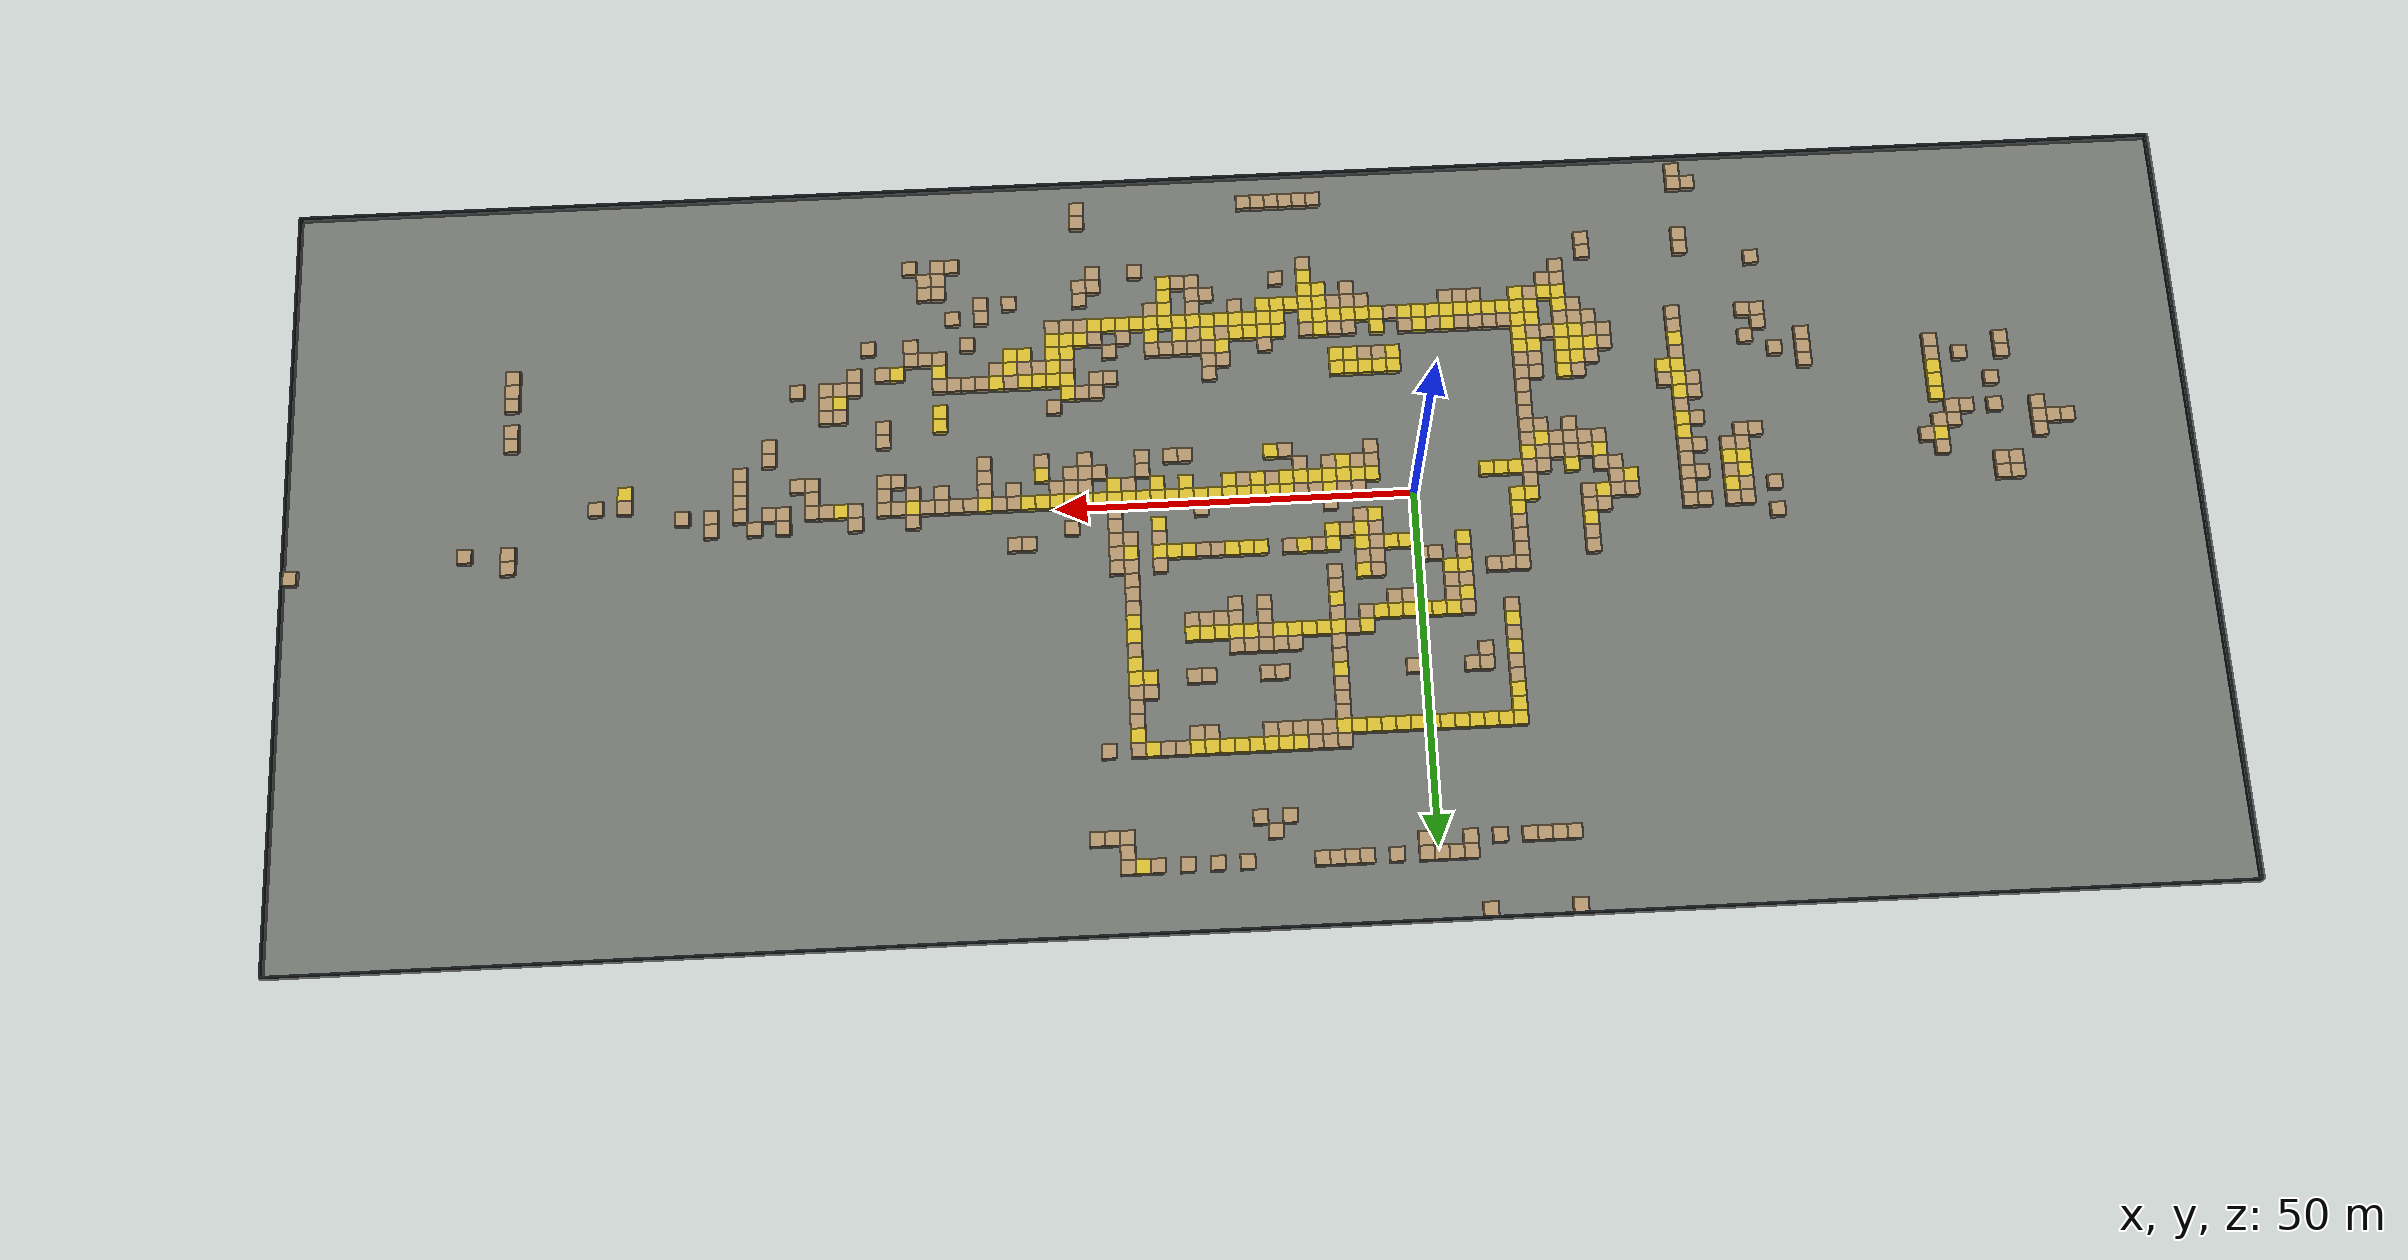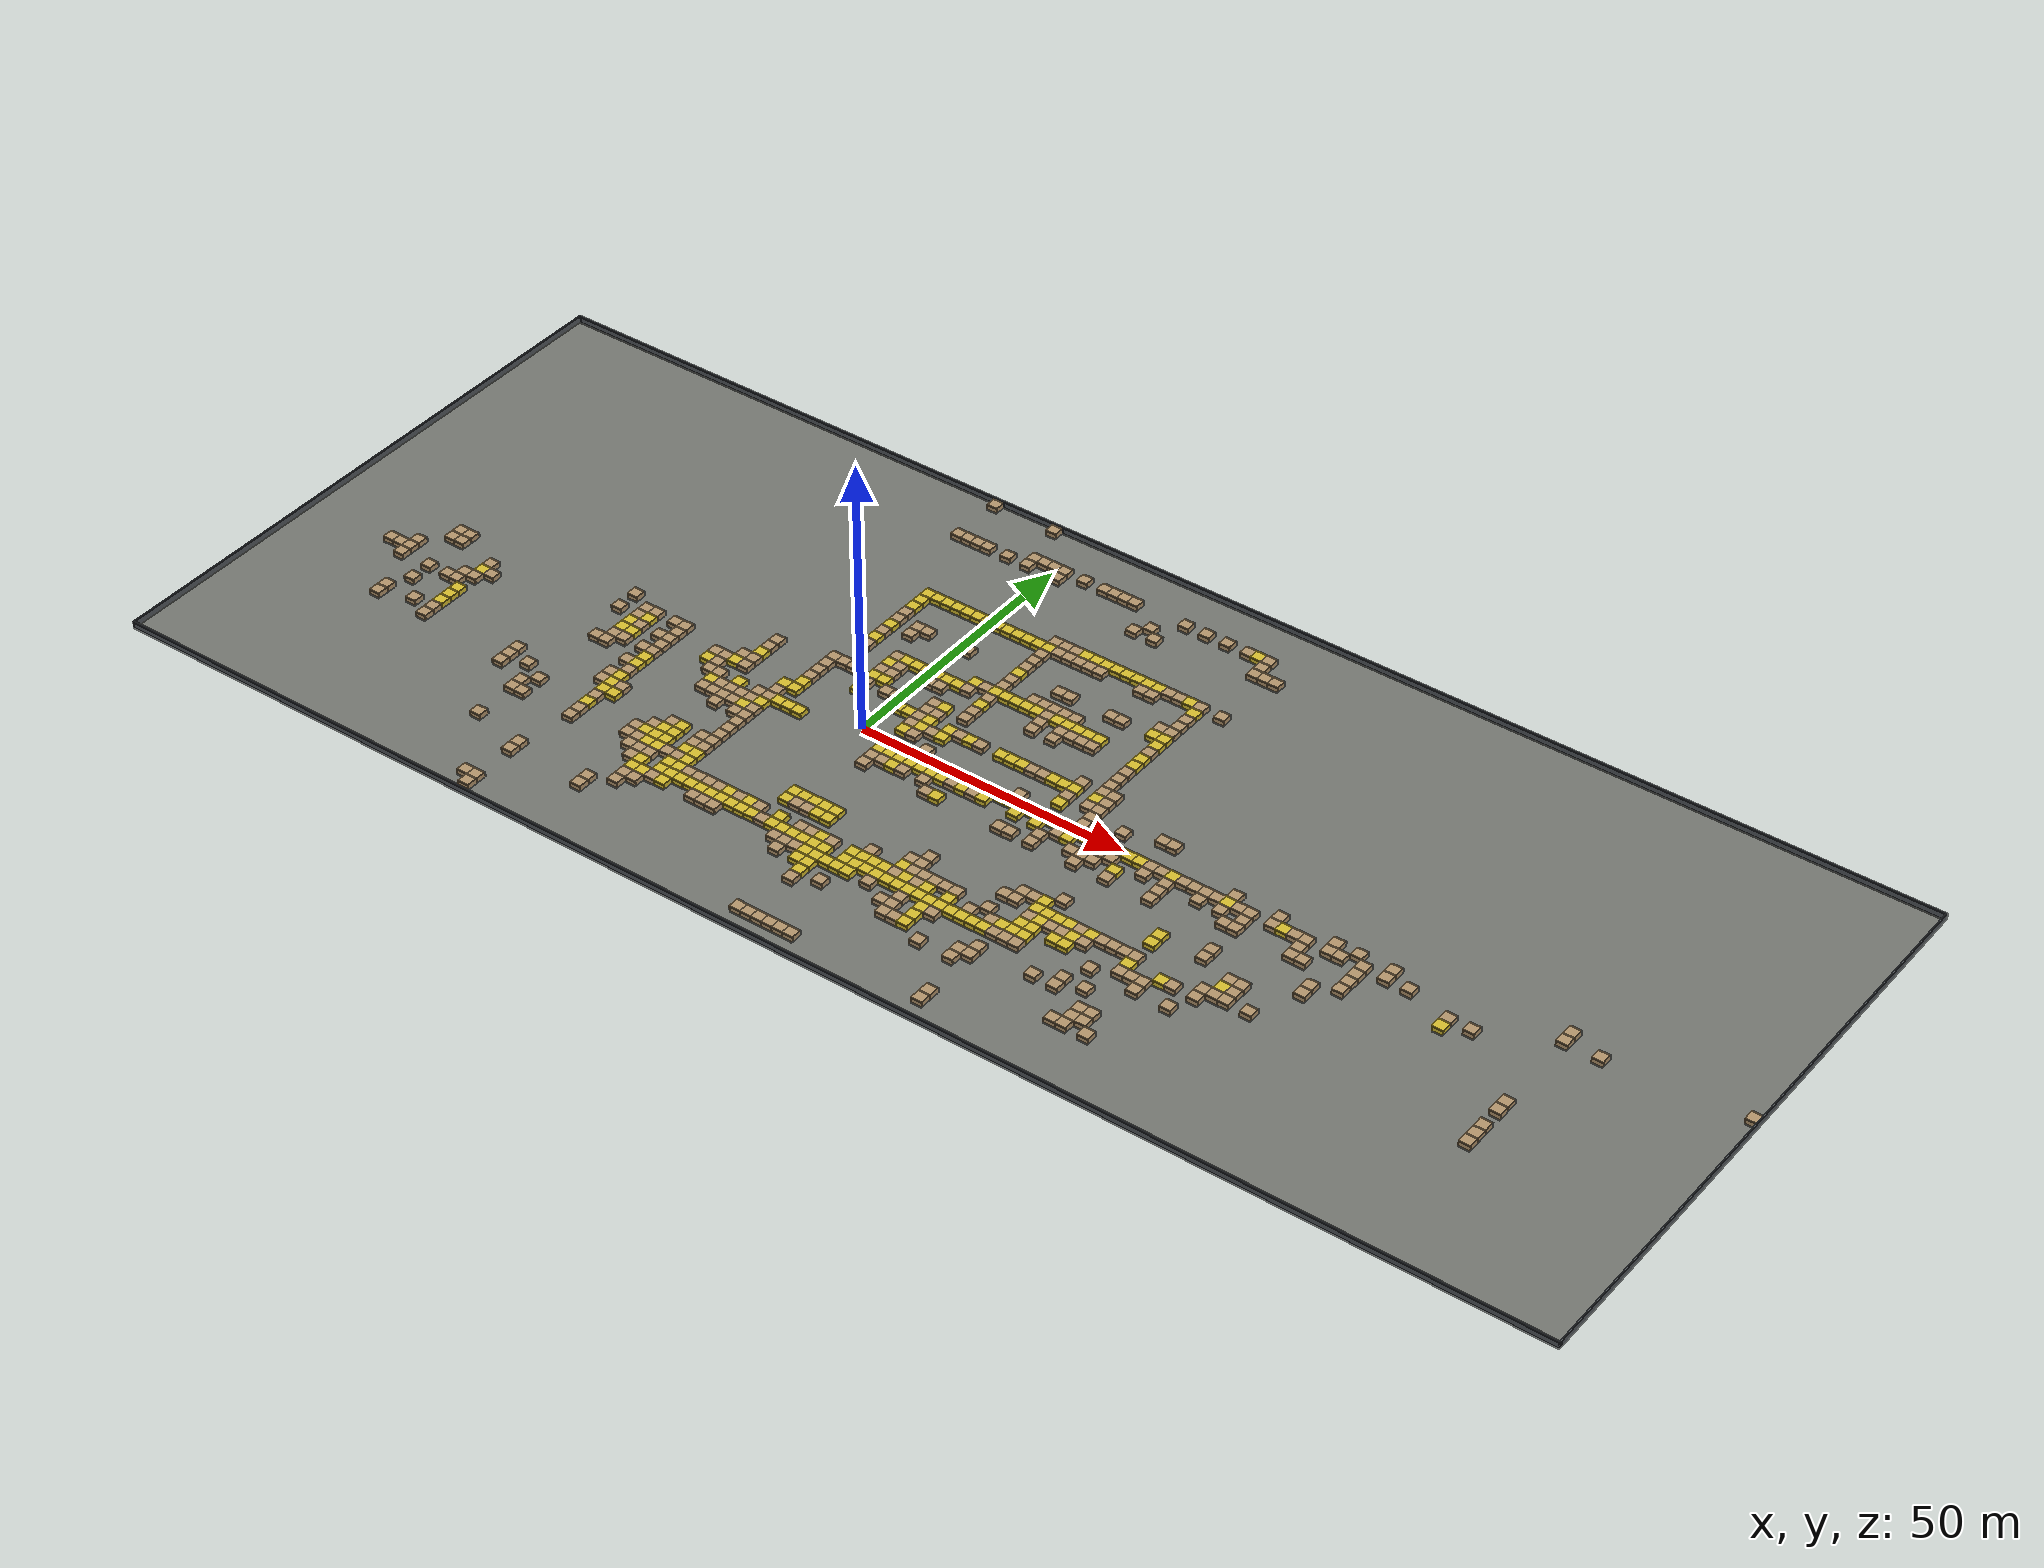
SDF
<?xml version="1.0"?>
<sdf version="1.6">
  <world name="map5_factory_approx">
    <plugin name="gazebo_ros_state" filename="libgazebo_ros_state.so"><update_rate>10.0</update_rate></plugin>
    <scene><ambient>0.50 0.50 0.50 1</ambient><background>0.70 0.78 0.86 1</background><shadows>true</shadows></scene>
    <physics name="default_physics" type="ode"><real_time_update_rate>1000</real_time_update_rate><max_step_size>0.001</max_step_size></physics>
    <light name="sun" type="directional"><cast_shadows>true</cast_shadows><pose>0 0 20 0 0 0</pose><diffuse>0.82 0.82 0.82 1</diffuse><specular>0.2 0.2 0.2 1</specular><direction>-0.45 0.15 -0.88</direction></light>
    <model name="map5_floor"><static>true</static>
      <link name="floor"><pose>23.740 5.509 -0.020 0 0 0</pose><collision name="collision"><geometry><box><size>265.900 108.900 0.040</size></box></geometry></collision><visual name="visual"><geometry><box><size>265.900 108.900 0.040</size></box></geometry><material><ambient>0.45 0.46 0.44 1</ambient><diffuse>0.45 0.46 0.44 1</diffuse></material></visual></link>
    </model>
    <model name="map5_perimeter_walls"><static>true</static>
      <link name="west_wall"><pose>-109.335 5.509 0.600 0 0 0</pose><collision name="collision"><geometry><box><size>0.250 109.400 1.200</size></box></geometry></collision><visual name="visual"><geometry><box><size>0.250 109.400 1.200</size></box></geometry><material><ambient>0.32 0.34 0.36 1</ambient><diffuse>0.32 0.34 0.36 1</diffuse></material></visual></link>
      <link name="east_wall"><pose>156.815 5.509 0.600 0 0 0</pose><collision name="collision"><geometry><box><size>0.250 109.400 1.200</size></box></geometry></collision><visual name="visual"><geometry><box><size>0.250 109.400 1.200</size></box></geometry><material><ambient>0.32 0.34 0.36 1</ambient><diffuse>0.32 0.34 0.36 1</diffuse></material></visual></link>
      <link name="south_wall"><pose>23.740 -49.066 0.600 0 0 0</pose><collision name="collision"><geometry><box><size>266.400 0.250 1.200</size></box></geometry></collision><visual name="visual"><geometry><box><size>266.400 0.250 1.200</size></box></geometry><material><ambient>0.32 0.34 0.36 1</ambient><diffuse>0.32 0.34 0.36 1</diffuse></material></visual></link>
      <link name="north_wall"><pose>23.740 60.084 0.600 0 0 0</pose><collision name="collision"><geometry><box><size>266.400 0.250 1.200</size></box></geometry></collision><visual name="visual"><geometry><box><size>266.400 0.250 1.200</size></box></geometry><material><ambient>0.32 0.34 0.36 1</ambient><diffuse>0.32 0.34 0.36 1</diffuse></material></visual></link>
    </model>
    <model name="map5_obstacle_blocks"><static>true</static>
      <link name="obs_0068_0030"><pose>27.790 -1.041 0.500 0 0 0</pose><collision name="collision"><geometry><box><size>2.000 2.000 1.000</size></box></geometry></collision><visual name="visual"><geometry><box><size>2.000 2.000 1.000</size></box></geometry><material><ambient>0.84 0.74 0.18 1</ambient><diffuse>0.84 0.74 0.18 1</diffuse></material></visual></link>
      <link name="obs_0060_0031"><pose>11.790 -3.041 0.500 0 0 0</pose><collision name="collision"><geometry><box><size>2.000 2.000 1.000</size></box></geometry></collision><visual name="visual"><geometry><box><size>2.000 2.000 1.000</size></box></geometry><material><ambient>0.84 0.74 0.18 1</ambient><diffuse>0.84 0.74 0.18 1</diffuse></material></visual></link>
      <link name="obs_0067_0030"><pose>25.790 -1.041 0.500 0 0 0</pose><collision name="collision"><geometry><box><size>2.000 2.000 1.000</size></box></geometry></collision><visual name="visual"><geometry><box><size>2.000 2.000 1.000</size></box></geometry><material><ambient>0.84 0.74 0.18 1</ambient><diffuse>0.84 0.74 0.18 1</diffuse></material></visual></link>
      <link name="obs_0065_0031"><pose>21.790 -3.041 0.500 0 0 0</pose><collision name="collision"><geometry><box><size>2.000 2.000 1.000</size></box></geometry></collision><visual name="visual"><geometry><box><size>2.000 2.000 1.000</size></box></geometry><material><ambient>0.84 0.74 0.18 1</ambient><diffuse>0.84 0.74 0.18 1</diffuse></material></visual></link>
      <link name="obs_0062_0031"><pose>15.790 -3.041 0.500 0 0 0</pose><collision name="collision"><geometry><box><size>2.000 2.000 1.000</size></box></geometry></collision><visual name="visual"><geometry><box><size>2.000 2.000 1.000</size></box></geometry><material><ambient>0.84 0.74 0.18 1</ambient><diffuse>0.84 0.74 0.18 1</diffuse></material></visual></link>
      <link name="obs_0046_0040"><pose>-16.210 -21.041 0.500 0 0 0</pose><collision name="collision"><geometry><box><size>2.000 2.000 1.000</size></box></geometry></collision><visual name="visual"><geometry><box><size>2.000 2.000 1.000</size></box></geometry><material><ambient>0.84 0.74 0.18 1</ambient><diffuse>0.84 0.74 0.18 1</diffuse></material></visual></link>
      <link name="obs_0058_0031"><pose>7.790 -3.041 0.500 0 0 0</pose><collision name="collision"><geometry><box><size>2.000 2.000 1.000</size></box></geometry></collision><visual name="visual"><geometry><box><size>2.000 2.000 1.000</size></box></geometry><material><ambient>0.84 0.74 0.18 1</ambient><diffuse>0.84 0.74 0.18 1</diffuse></material></visual></link>
      <link name="obs_0061_0044"><pose>13.790 -29.041 0.500 0 0 0</pose><collision name="collision"><geometry><box><size>2.000 2.000 1.000</size></box></geometry></collision><visual name="visual"><geometry><box><size>2.000 2.000 1.000</size></box></geometry><material><ambient>0.84 0.74 0.18 1</ambient><diffuse>0.84 0.74 0.18 1</diffuse></material></visual></link>
      <link name="obs_0066_0030"><pose>23.790 -1.041 0.500 0 0 0</pose><collision name="collision"><geometry><box><size>2.000 2.000 1.000</size></box></geometry></collision><visual name="visual"><geometry><box><size>2.000 2.000 1.000</size></box></geometry><material><ambient>0.84 0.74 0.18 1</ambient><diffuse>0.84 0.74 0.18 1</diffuse></material></visual></link>
      <link name="obs_0055_0026"><pose>1.790 6.959 0.500 0 0 0</pose><collision name="collision"><geometry><box><size>2.000 2.000 1.000</size></box></geometry></collision><visual name="visual"><geometry><box><size>2.000 2.000 1.000</size></box></geometry><material><ambient>0.84 0.74 0.18 1</ambient><diffuse>0.84 0.74 0.18 1</diffuse></material></visual></link>
      <link name="obs_0069_0030"><pose>29.790 -1.041 0.500 0 0 0</pose><collision name="collision"><geometry><box><size>2.000 2.000 1.000</size></box></geometry></collision><visual name="visual"><geometry><box><size>2.000 2.000 1.000</size></box></geometry><material><ambient>0.84 0.74 0.18 1</ambient><diffuse>0.84 0.74 0.18 1</diffuse></material></visual></link>
      <link name="obs_0051_0043"><pose>-6.210 -27.041 0.500 0 0 0</pose><collision name="collision"><geometry><box><size>2.000 2.000 1.000</size></box></geometry></collision><visual name="visual"><geometry><box><size>2.000 2.000 1.000</size></box></geometry><material><ambient>0.84 0.74 0.18 1</ambient><diffuse>0.84 0.74 0.18 1</diffuse></material></visual></link>
      <link name="obs_0058_0024"><pose>7.790 10.959 0.500 0 0 0</pose><collision name="collision"><geometry><box><size>2.000 2.000 1.000</size></box></geometry></collision><visual name="visual"><geometry><box><size>2.000 2.000 1.000</size></box></geometry><material><ambient>0.84 0.74 0.18 1</ambient><diffuse>0.84 0.74 0.18 1</diffuse></material></visual></link>
      <link name="obs_0043_0039"><pose>-22.210 -19.041 0.500 0 0 0</pose><collision name="collision"><geometry><box><size>2.000 2.000 1.000</size></box></geometry></collision><visual name="visual"><geometry><box><size>2.000 2.000 1.000</size></box></geometry><material><ambient>0.84 0.74 0.18 1</ambient><diffuse>0.84 0.74 0.18 1</diffuse></material></visual></link>
      <link name="obs_0064_0030"><pose>19.790 -1.041 0.500 0 0 0</pose><collision name="collision"><geometry><box><size>2.000 2.000 1.000</size></box></geometry></collision><visual name="visual"><geometry><box><size>2.000 2.000 1.000</size></box></geometry><material><ambient>0.84 0.74 0.18 1</ambient><diffuse>0.84 0.74 0.18 1</diffuse></material></visual></link>
      <link name="obs_0070_0030"><pose>31.790 -1.041 0.500 0 0 0</pose><collision name="collision"><geometry><box><size>2.000 2.000 1.000</size></box></geometry></collision><visual name="visual"><geometry><box><size>2.000 2.000 1.000</size></box></geometry><material><ambient>0.84 0.74 0.18 1</ambient><diffuse>0.84 0.74 0.18 1</diffuse></material></visual></link>
      <link name="obs_0063_0043"><pose>17.790 -27.041 0.500 0 0 0</pose><collision name="collision"><geometry><box><size>2.000 2.000 1.000</size></box></geometry></collision><visual name="visual"><geometry><box><size>2.000 2.000 1.000</size></box></geometry><material><ambient>0.84 0.74 0.18 1</ambient><diffuse>0.84 0.74 0.18 1</diffuse></material></visual></link>
      <link name="obs_0061_0043"><pose>13.790 -27.041 0.500 0 0 0</pose><collision name="collision"><geometry><box><size>2.000 2.000 1.000</size></box></geometry></collision><visual name="visual"><geometry><box><size>2.000 2.000 1.000</size></box></geometry><material><ambient>0.84 0.74 0.18 1</ambient><diffuse>0.84 0.74 0.18 1</diffuse></material></visual></link>
      <link name="obs_0042_0039"><pose>-24.210 -19.041 0.500 0 0 0</pose><collision name="collision"><geometry><box><size>2.000 2.000 1.000</size></box></geometry></collision><visual name="visual"><geometry><box><size>2.000 2.000 1.000</size></box></geometry><material><ambient>0.84 0.74 0.18 1</ambient><diffuse>0.84 0.74 0.18 1</diffuse></material></visual></link>
      <link name="obs_0057_0031"><pose>5.790 -3.041 0.500 0 0 0</pose><collision name="collision"><geometry><box><size>2.000 2.000 1.000</size></box></geometry></collision><visual name="visual"><geometry><box><size>2.000 2.000 1.000</size></box></geometry><material><ambient>0.84 0.74 0.18 1</ambient><diffuse>0.84 0.74 0.18 1</diffuse></material></visual></link>
      <link name="obs_0067_0031"><pose>25.790 -3.041 0.500 0 0 0</pose><collision name="collision"><geometry><box><size>2.000 2.000 1.000</size></box></geometry></collision><visual name="visual"><geometry><box><size>2.000 2.000 1.000</size></box></geometry><material><ambient>0.84 0.74 0.18 1</ambient><diffuse>0.84 0.74 0.18 1</diffuse></material></visual></link>
      <link name="obs_0071_0043"><pose>33.790 -27.041 0.500 0 0 0</pose><collision name="collision"><geometry><box><size>2.000 2.000 1.000</size></box></geometry></collision><visual name="visual"><geometry><box><size>2.000 2.000 1.000</size></box></geometry><material><ambient>0.84 0.74 0.18 1</ambient><diffuse>0.84 0.74 0.18 1</diffuse></material></visual></link>
      <link name="obs_0060_0013"><pose>11.790 32.959 0.500 0 0 0</pose><collision name="collision"><geometry><box><size>2.000 2.000 1.000</size></box></geometry></collision><visual name="visual"><geometry><box><size>2.000 2.000 1.000</size></box></geometry><material><ambient>0.84 0.74 0.18 1</ambient><diffuse>0.84 0.74 0.18 1</diffuse></material></visual></link>
      <link name="obs_0041_0032"><pose>-26.210 -5.041 0.500 0 0 0</pose><collision name="collision"><geometry><box><size>2.000 2.000 1.000</size></box></geometry></collision><visual name="visual"><geometry><box><size>2.000 2.000 1.000</size></box></geometry><material><ambient>0.84 0.74 0.18 1</ambient><diffuse>0.84 0.74 0.18 1</diffuse></material></visual></link>
      <link name="obs_0042_0040"><pose>-24.210 -21.041 0.500 0 0 0</pose><collision name="collision"><geometry><box><size>2.000 2.000 1.000</size></box></geometry></collision><visual name="visual"><geometry><box><size>2.000 2.000 1.000</size></box></geometry><material><ambient>0.84 0.74 0.18 1</ambient><diffuse>0.84 0.74 0.18 1</diffuse></material></visual></link>
      <link name="obs_0071_0026"><pose>33.790 6.959 0.500 0 0 0</pose><collision name="collision"><geometry><box><size>2.000 2.000 1.000</size></box></geometry></collision><visual name="visual"><geometry><box><size>2.000 2.000 1.000</size></box></geometry><material><ambient>0.84 0.74 0.18 1</ambient><diffuse>0.84 0.74 0.18 1</diffuse></material></visual></link>
      <link name="obs_0074_0030"><pose>39.790 -1.041 0.500 0 0 0</pose><collision name="collision"><geometry><box><size>2.000 2.000 1.000</size></box></geometry></collision><visual name="visual"><geometry><box><size>2.000 2.000 1.000</size></box></geometry><material><ambient>0.84 0.74 0.18 1</ambient><diffuse>0.84 0.74 0.18 1</diffuse></material></visual></link>
      <link name="obs_0065_0030"><pose>21.790 -1.041 0.500 0 0 0</pose><collision name="collision"><geometry><box><size>2.000 2.000 1.000</size></box></geometry></collision><visual name="visual"><geometry><box><size>2.000 2.000 1.000</size></box></geometry><material><ambient>0.84 0.74 0.18 1</ambient><diffuse>0.84 0.74 0.18 1</diffuse></material></visual></link>
      <link name="obs_0055_0013"><pose>1.790 32.959 0.500 0 0 0</pose><collision name="collision"><geometry><box><size>2.000 2.000 1.000</size></box></geometry></collision><visual name="visual"><geometry><box><size>2.000 2.000 1.000</size></box></geometry><material><ambient>0.84 0.74 0.18 1</ambient><diffuse>0.84 0.74 0.18 1</diffuse></material></visual></link>
      <link name="obs_0058_0026"><pose>7.790 6.959 0.500 0 0 0</pose><collision name="collision"><geometry><box><size>2.000 2.000 1.000</size></box></geometry></collision><visual name="visual"><geometry><box><size>2.000 2.000 1.000</size></box></geometry><material><ambient>0.84 0.74 0.18 1</ambient><diffuse>0.84 0.74 0.18 1</diffuse></material></visual></link>
      <link name="obs_0059_0039"><pose>9.790 -19.041 0.500 0 0 0</pose><collision name="collision"><geometry><box><size>2.000 2.000 1.000</size></box></geometry></collision><visual name="visual"><geometry><box><size>2.000 2.000 1.000</size></box></geometry><material><ambient>0.84 0.74 0.18 1</ambient><diffuse>0.84 0.74 0.18 1</diffuse></material></visual></link>
      <link name="obs_0070_0031"><pose>31.790 -3.041 0.500 0 0 0</pose><collision name="collision"><geometry><box><size>2.000 2.000 1.000</size></box></geometry></collision><visual name="visual"><geometry><box><size>2.000 2.000 1.000</size></box></geometry><material><ambient>0.84 0.74 0.18 1</ambient><diffuse>0.84 0.74 0.18 1</diffuse></material></visual></link>
      <link name="obs_0068_0042"><pose>27.790 -25.041 0.500 0 0 0</pose><collision name="collision"><geometry><box><size>2.000 2.000 1.000</size></box></geometry></collision><visual name="visual"><geometry><box><size>2.000 2.000 1.000</size></box></geometry><material><ambient>0.84 0.74 0.18 1</ambient><diffuse>0.84 0.74 0.18 1</diffuse></material></visual></link>
      <link name="obs_0046_0041"><pose>-16.210 -23.041 0.500 0 0 0</pose><collision name="collision"><geometry><box><size>2.000 2.000 1.000</size></box></geometry></collision><visual name="visual"><geometry><box><size>2.000 2.000 1.000</size></box></geometry><material><ambient>0.84 0.74 0.18 1</ambient><diffuse>0.84 0.74 0.18 1</diffuse></material></visual></link>
      <link name="obs_0056_0026"><pose>3.790 6.959 0.500 0 0 0</pose><collision name="collision"><geometry><box><size>2.000 2.000 1.000</size></box></geometry></collision><visual name="visual"><geometry><box><size>2.000 2.000 1.000</size></box></geometry><material><ambient>0.84 0.74 0.18 1</ambient><diffuse>0.84 0.74 0.18 1</diffuse></material></visual></link>
      <link name="obs_0036_0038"><pose>-36.210 -17.041 0.500 0 0 0</pose><collision name="collision"><geometry><box><size>2.000 2.000 1.000</size></box></geometry></collision><visual name="visual"><geometry><box><size>2.000 2.000 1.000</size></box></geometry><material><ambient>0.84 0.74 0.18 1</ambient><diffuse>0.84 0.74 0.18 1</diffuse></material></visual></link>
      <link name="obs_0089_0030"><pose>69.790 -1.041 0.500 0 0 0</pose><collision name="collision"><geometry><box><size>2.000 2.000 1.000</size></box></geometry></collision><visual name="visual"><geometry><box><size>2.000 2.000 1.000</size></box></geometry><material><ambient>0.84 0.74 0.18 1</ambient><diffuse>0.84 0.74 0.18 1</diffuse></material></visual></link>
      <link name="obs_0082_0040"><pose>55.790 -21.041 0.500 0 0 0</pose><collision name="collision"><geometry><box><size>2.000 2.000 1.000</size></box></geometry></collision><visual name="visual"><geometry><box><size>2.000 2.000 1.000</size></box></geometry><material><ambient>0.84 0.74 0.18 1</ambient><diffuse>0.84 0.74 0.18 1</diffuse></material></visual></link>
      <link name="obs_0072_0043"><pose>35.790 -27.041 0.500 0 0 0</pose><collision name="collision"><geometry><box><size>2.000 2.000 1.000</size></box></geometry></collision><visual name="visual"><geometry><box><size>2.000 2.000 1.000</size></box></geometry><material><ambient>0.84 0.74 0.18 1</ambient><diffuse>0.84 0.74 0.18 1</diffuse></material></visual></link>
      <link name="obs_0058_0027"><pose>7.790 4.959 0.500 0 0 0</pose><collision name="collision"><geometry><box><size>2.000 2.000 1.000</size></box></geometry></collision><visual name="visual"><geometry><box><size>2.000 2.000 1.000</size></box></geometry><material><ambient>0.84 0.74 0.18 1</ambient><diffuse>0.84 0.74 0.18 1</diffuse></material></visual></link>
      <link name="obs_0067_0043"><pose>25.790 -27.041 0.500 0 0 0</pose><collision name="collision"><geometry><box><size>2.000 2.000 1.000</size></box></geometry></collision><visual name="visual"><geometry><box><size>2.000 2.000 1.000</size></box></geometry><material><ambient>0.84 0.74 0.18 1</ambient><diffuse>0.84 0.74 0.18 1</diffuse></material></visual></link>
      <link name="obs_0056_0043"><pose>3.790 -27.041 0.500 0 0 0</pose><collision name="collision"><geometry><box><size>2.000 2.000 1.000</size></box></geometry></collision><visual name="visual"><geometry><box><size>2.000 2.000 1.000</size></box></geometry><material><ambient>0.84 0.74 0.18 1</ambient><diffuse>0.84 0.74 0.18 1</diffuse></material></visual></link>
      <link name="obs_0063_0044"><pose>17.790 -29.041 0.500 0 0 0</pose><collision name="collision"><geometry><box><size>2.000 2.000 1.000</size></box></geometry></collision><visual name="visual"><geometry><box><size>2.000 2.000 1.000</size></box></geometry><material><ambient>0.84 0.74 0.18 1</ambient><diffuse>0.84 0.74 0.18 1</diffuse></material></visual></link>
      <link name="obs_0061_0031"><pose>13.790 -3.041 0.500 0 0 0</pose><collision name="collision"><geometry><box><size>2.000 2.000 1.000</size></box></geometry></collision><visual name="visual"><geometry><box><size>2.000 2.000 1.000</size></box></geometry><material><ambient>0.84 0.74 0.18 1</ambient><diffuse>0.84 0.74 0.18 1</diffuse></material></visual></link>
      <link name="obs_0059_0032"><pose>9.790 -5.041 0.500 0 0 0</pose><collision name="collision"><geometry><box><size>2.000 2.000 1.000</size></box></geometry></collision><visual name="visual"><geometry><box><size>2.000 2.000 1.000</size></box></geometry><material><ambient>0.84 0.74 0.18 1</ambient><diffuse>0.84 0.74 0.18 1</diffuse></material></visual></link>
      <link name="obs_0058_0039"><pose>7.790 -19.041 0.500 0 0 0</pose><collision name="collision"><geometry><box><size>2.000 2.000 1.000</size></box></geometry></collision><visual name="visual"><geometry><box><size>2.000 2.000 1.000</size></box></geometry><material><ambient>0.84 0.74 0.18 1</ambient><diffuse>0.84 0.74 0.18 1</diffuse></material></visual></link>
      <link name="obs_0064_0042"><pose>19.790 -25.041 0.500 0 0 0</pose><collision name="collision"><geometry><box><size>2.000 2.000 1.000</size></box></geometry></collision><visual name="visual"><geometry><box><size>2.000 2.000 1.000</size></box></geometry><material><ambient>0.84 0.74 0.18 1</ambient><diffuse>0.84 0.74 0.18 1</diffuse></material></visual></link>
      <link name="obs_0094_0038"><pose>79.790 -17.041 0.500 0 0 0</pose><collision name="collision"><geometry><box><size>2.000 2.000 1.000</size></box></geometry></collision><visual name="visual"><geometry><box><size>2.000 2.000 1.000</size></box></geometry><material><ambient>0.84 0.74 0.18 1</ambient><diffuse>0.84 0.74 0.18 1</diffuse></material></visual></link>
      <link name="obs_0060_0042"><pose>11.790 -25.041 0.500 0 0 0</pose><collision name="collision"><geometry><box><size>2.000 2.000 1.000</size></box></geometry></collision><visual name="visual"><geometry><box><size>2.000 2.000 1.000</size></box></geometry><material><ambient>0.84 0.74 0.18 1</ambient><diffuse>0.84 0.74 0.18 1</diffuse></material></visual></link>
      <link name="obs_0084_0030"><pose>59.790 -1.041 0.500 0 0 0</pose><collision name="collision"><geometry><box><size>2.000 2.000 1.000</size></box></geometry></collision><visual name="visual"><geometry><box><size>2.000 2.000 1.000</size></box></geometry><material><ambient>0.84 0.74 0.18 1</ambient><diffuse>0.84 0.74 0.18 1</diffuse></material></visual></link>
      <link name="obs_0059_0040"><pose>9.790 -21.041 0.500 0 0 0</pose><collision name="collision"><geometry><box><size>2.000 2.000 1.000</size></box></geometry></collision><visual name="visual"><geometry><box><size>2.000 2.000 1.000</size></box></geometry><material><ambient>0.84 0.74 0.18 1</ambient><diffuse>0.84 0.74 0.18 1</diffuse></material></visual></link>
      <link name="obs_0053_0042"><pose>-2.210 -25.041 0.500 0 0 0</pose><collision name="collision"><geometry><box><size>2.000 2.000 1.000</size></box></geometry></collision><visual name="visual"><geometry><box><size>2.000 2.000 1.000</size></box></geometry><material><ambient>0.84 0.74 0.18 1</ambient><diffuse>0.84 0.74 0.18 1</diffuse></material></visual></link>
      <link name="obs_0049_0031"><pose>-10.210 -3.041 0.500 0 0 0</pose><collision name="collision"><geometry><box><size>2.000 2.000 1.000</size></box></geometry></collision><visual name="visual"><geometry><box><size>2.000 2.000 1.000</size></box></geometry><material><ambient>0.84 0.74 0.18 1</ambient><diffuse>0.84 0.74 0.18 1</diffuse></material></visual></link>
      <link name="obs_0047_0031"><pose>-14.210 -3.041 0.500 0 0 0</pose><collision name="collision"><geometry><box><size>2.000 2.000 1.000</size></box></geometry></collision><visual name="visual"><geometry><box><size>2.000 2.000 1.000</size></box></geometry><material><ambient>0.84 0.74 0.18 1</ambient><diffuse>0.84 0.74 0.18 1</diffuse></material></visual></link>
      <link name="obs_0051_0013"><pose>-6.210 32.959 0.500 0 0 0</pose><collision name="collision"><geometry><box><size>2.000 2.000 1.000</size></box></geometry></collision><visual name="visual"><geometry><box><size>2.000 2.000 1.000</size></box></geometry><material><ambient>0.84 0.74 0.18 1</ambient><diffuse>0.84 0.74 0.18 1</diffuse></material></visual></link>
      <link name="obs_0072_0031"><pose>35.790 -3.041 0.500 0 0 0</pose><collision name="collision"><geometry><box><size>2.000 2.000 1.000</size></box></geometry></collision><visual name="visual"><geometry><box><size>2.000 2.000 1.000</size></box></geometry><material><ambient>0.84 0.74 0.18 1</ambient><diffuse>0.84 0.74 0.18 1</diffuse></material></visual></link>
      <link name="obs_0059_0043"><pose>9.790 -27.041 0.500 0 0 0</pose><collision name="collision"><geometry><box><size>2.000 2.000 1.000</size></box></geometry></collision><visual name="visual"><geometry><box><size>2.000 2.000 1.000</size></box></geometry><material><ambient>0.84 0.74 0.18 1</ambient><diffuse>0.84 0.74 0.18 1</diffuse></material></visual></link>
      <link name="obs_0043_0044"><pose>-22.210 -29.041 0.500 0 0 0</pose><collision name="collision"><geometry><box><size>2.000 2.000 1.000</size></box></geometry></collision><visual name="visual"><geometry><box><size>2.000 2.000 1.000</size></box></geometry><material><ambient>0.84 0.74 0.18 1</ambient><diffuse>0.84 0.74 0.18 1</diffuse></material></visual></link>
      <link name="obs_0065_0043"><pose>21.790 -27.041 0.500 0 0 0</pose><collision name="collision"><geometry><box><size>2.000 2.000 1.000</size></box></geometry></collision><visual name="visual"><geometry><box><size>2.000 2.000 1.000</size></box></geometry><material><ambient>0.84 0.74 0.18 1</ambient><diffuse>0.84 0.74 0.18 1</diffuse></material></visual></link>
      <link name="obs_0050_0013"><pose>-8.210 32.959 0.500 0 0 0</pose><collision name="collision"><geometry><box><size>2.000 2.000 1.000</size></box></geometry></collision><visual name="visual"><geometry><box><size>2.000 2.000 1.000</size></box></geometry><material><ambient>0.84 0.74 0.18 1</ambient><diffuse>0.84 0.74 0.18 1</diffuse></material></visual></link>
      <link name="obs_0047_0043"><pose>-14.210 -27.041 0.500 0 0 0</pose><collision name="collision"><geometry><box><size>2.000 2.000 1.000</size></box></geometry></collision><visual name="visual"><geometry><box><size>2.000 2.000 1.000</size></box></geometry><material><ambient>0.84 0.74 0.18 1</ambient><diffuse>0.84 0.74 0.18 1</diffuse></material></visual></link>
      <link name="obs_0068_0043"><pose>27.790 -27.041 0.500 0 0 0</pose><collision name="collision"><geometry><box><size>2.000 2.000 1.000</size></box></geometry></collision><visual name="visual"><geometry><box><size>2.000 2.000 1.000</size></box></geometry><material><ambient>0.84 0.74 0.18 1</ambient><diffuse>0.84 0.74 0.18 1</diffuse></material></visual></link>
      <link name="obs_0057_0043"><pose>5.790 -27.041 0.500 0 0 0</pose><collision name="collision"><geometry><box><size>2.000 2.000 1.000</size></box></geometry></collision><visual name="visual"><geometry><box><size>2.000 2.000 1.000</size></box></geometry><material><ambient>0.84 0.74 0.18 1</ambient><diffuse>0.84 0.74 0.18 1</diffuse></material></visual></link>
      <link name="obs_0045_0040"><pose>-18.210 -21.041 0.500 0 0 0</pose><collision name="collision"><geometry><box><size>2.000 2.000 1.000</size></box></geometry></collision><visual name="visual"><geometry><box><size>2.000 2.000 1.000</size></box></geometry><material><ambient>0.84 0.74 0.18 1</ambient><diffuse>0.84 0.74 0.18 1</diffuse></material></visual></link>
      <link name="obs_0064_0043"><pose>19.790 -27.041 0.500 0 0 0</pose><collision name="collision"><geometry><box><size>2.000 2.000 1.000</size></box></geometry></collision><visual name="visual"><geometry><box><size>2.000 2.000 1.000</size></box></geometry><material><ambient>0.84 0.74 0.18 1</ambient><diffuse>0.84 0.74 0.18 1</diffuse></material></visual></link>
      <link name="obs_0059_0031"><pose>9.790 -3.041 0.500 0 0 0</pose><collision name="collision"><geometry><box><size>2.000 2.000 1.000</size></box></geometry></collision><visual name="visual"><geometry><box><size>2.000 2.000 1.000</size></box></geometry><material><ambient>0.84 0.74 0.18 1</ambient><diffuse>0.84 0.74 0.18 1</diffuse></material></visual></link>
      <link name="obs_0055_0040"><pose>1.790 -21.041 0.500 0 0 0</pose><collision name="collision"><geometry><box><size>2.000 2.000 1.000</size></box></geometry></collision><visual name="visual"><geometry><box><size>2.000 2.000 1.000</size></box></geometry><material><ambient>0.84 0.74 0.18 1</ambient><diffuse>0.84 0.74 0.18 1</diffuse></material></visual></link>
      <link name="obs_0070_0026"><pose>31.790 6.959 0.500 0 0 0</pose><collision name="collision"><geometry><box><size>2.000 2.000 1.000</size></box></geometry></collision><visual name="visual"><geometry><box><size>2.000 2.000 1.000</size></box></geometry><material><ambient>0.84 0.74 0.18 1</ambient><diffuse>0.84 0.74 0.18 1</diffuse></material></visual></link>
      <link name="obs_0048_0013"><pose>-12.210 32.959 0.500 0 0 0</pose><collision name="collision"><geometry><box><size>2.000 2.000 1.000</size></box></geometry></collision><visual name="visual"><geometry><box><size>2.000 2.000 1.000</size></box></geometry><material><ambient>0.84 0.74 0.18 1</ambient><diffuse>0.84 0.74 0.18 1</diffuse></material></visual></link>
      <link name="obs_0072_0026"><pose>35.790 6.959 0.500 0 0 0</pose><collision name="collision"><geometry><box><size>2.000 2.000 1.000</size></box></geometry></collision><visual name="visual"><geometry><box><size>2.000 2.000 1.000</size></box></geometry><material><ambient>0.84 0.74 0.18 1</ambient><diffuse>0.84 0.74 0.18 1</diffuse></material></visual></link>
      <link name="obs_0056_0042"><pose>3.790 -25.041 0.500 0 0 0</pose><collision name="collision"><geometry><box><size>2.000 2.000 1.000</size></box></geometry></collision><visual name="visual"><geometry><box><size>2.000 2.000 1.000</size></box></geometry><material><ambient>0.84 0.74 0.18 1</ambient><diffuse>0.84 0.74 0.18 1</diffuse></material></visual></link>
      <link name="obs_0049_0013"><pose>-10.210 32.959 0.500 0 0 0</pose><collision name="collision"><geometry><box><size>2.000 2.000 1.000</size></box></geometry></collision><visual name="visual"><geometry><box><size>2.000 2.000 1.000</size></box></geometry><material><ambient>0.84 0.74 0.18 1</ambient><diffuse>0.84 0.74 0.18 1</diffuse></material></visual></link>
      <link name="obs_0051_0042"><pose>-6.210 -25.041 0.500 0 0 0</pose><collision name="collision"><geometry><box><size>2.000 2.000 1.000</size></box></geometry></collision><visual name="visual"><geometry><box><size>2.000 2.000 1.000</size></box></geometry><material><ambient>0.84 0.74 0.18 1</ambient><diffuse>0.84 0.74 0.18 1</diffuse></material></visual></link>
      <link name="obs_0094_0030"><pose>79.790 -1.041 0.500 0 0 0</pose><collision name="collision"><geometry><box><size>2.000 2.000 1.000</size></box></geometry></collision><visual name="visual"><geometry><box><size>2.000 2.000 1.000</size></box></geometry><material><ambient>0.84 0.74 0.18 1</ambient><diffuse>0.84 0.74 0.18 1</diffuse></material></visual></link>
      <link name="obs_0060_0026"><pose>11.790 6.959 0.500 0 0 0</pose><collision name="collision"><geometry><box><size>2.000 2.000 1.000</size></box></geometry></collision><visual name="visual"><geometry><box><size>2.000 2.000 1.000</size></box></geometry><material><ambient>0.84 0.74 0.18 1</ambient><diffuse>0.84 0.74 0.18 1</diffuse></material></visual></link>
      <link name="obs_0080_0032"><pose>51.790 -5.041 0.500 0 0 0</pose><collision name="collision"><geometry><box><size>2.000 2.000 1.000</size></box></geometry></collision><visual name="visual"><geometry><box><size>2.000 2.000 1.000</size></box></geometry><material><ambient>0.84 0.74 0.18 1</ambient><diffuse>0.84 0.74 0.18 1</diffuse></material></visual></link>
      <link name="obs_0082_0041"><pose>55.790 -23.041 0.500 0 0 0</pose><collision name="collision"><geometry><box><size>2.000 2.000 1.000</size></box></geometry></collision><visual name="visual"><geometry><box><size>2.000 2.000 1.000</size></box></geometry><material><ambient>0.84 0.74 0.18 1</ambient><diffuse>0.84 0.74 0.18 1</diffuse></material></visual></link>
      <link name="obs_0077_0042"><pose>45.790 -25.041 0.500 0 0 0</pose><collision name="collision"><geometry><box><size>2.000 2.000 1.000</size></box></geometry></collision><visual name="visual"><geometry><box><size>2.000 2.000 1.000</size></box></geometry><material><ambient>0.84 0.74 0.18 1</ambient><diffuse>0.84 0.74 0.18 1</diffuse></material></visual></link>
      <link name="obs_0063_0042"><pose>17.790 -25.041 0.500 0 0 0</pose><collision name="collision"><geometry><box><size>2.000 2.000 1.000</size></box></geometry></collision><visual name="visual"><geometry><box><size>2.000 2.000 1.000</size></box></geometry><material><ambient>0.84 0.74 0.18 1</ambient><diffuse>0.84 0.74 0.18 1</diffuse></material></visual></link>
      <link name="obs_0056_0013"><pose>3.790 32.959 0.500 0 0 0</pose><collision name="collision"><geometry><box><size>2.000 2.000 1.000</size></box></geometry></collision><visual name="visual"><geometry><box><size>2.000 2.000 1.000</size></box></geometry><material><ambient>0.84 0.74 0.18 1</ambient><diffuse>0.84 0.74 0.18 1</diffuse></material></visual></link>
      <link name="obs_0043_0043"><pose>-22.210 -27.041 0.500 0 0 0</pose><collision name="collision"><geometry><box><size>2.000 2.000 1.000</size></box></geometry></collision><visual name="visual"><geometry><box><size>2.000 2.000 1.000</size></box></geometry><material><ambient>0.84 0.74 0.18 1</ambient><diffuse>0.84 0.74 0.18 1</diffuse></material></visual></link>
      <link name="obs_0039_0030"><pose>-30.210 -1.041 0.500 0 0 0</pose><collision name="collision"><geometry><box><size>2.000 2.000 1.000</size></box></geometry></collision><visual name="visual"><geometry><box><size>2.000 2.000 1.000</size></box></geometry><material><ambient>0.84 0.74 0.18 1</ambient><diffuse>0.84 0.74 0.18 1</diffuse></material></visual></link>
      <link name="obs_0060_0030"><pose>11.790 -1.041 0.500 0 0 0</pose><collision name="collision"><geometry><box><size>2.000 2.000 1.000</size></box></geometry></collision><visual name="visual"><geometry><box><size>2.000 2.000 1.000</size></box></geometry><material><ambient>0.84 0.74 0.18 1</ambient><diffuse>0.84 0.74 0.18 1</diffuse></material></visual></link>
      <link name="obs_0074_0021"><pose>39.790 16.959 0.500 0 0 0</pose><collision name="collision"><geometry><box><size>2.000 2.000 1.000</size></box></geometry></collision><visual name="visual"><geometry><box><size>2.000 2.000 1.000</size></box></geometry><material><ambient>0.84 0.74 0.18 1</ambient><diffuse>0.84 0.74 0.18 1</diffuse></material></visual></link>
      <link name="obs_0070_0012"><pose>31.790 34.959 0.500 0 0 0</pose><collision name="collision"><geometry><box><size>2.000 2.000 1.000</size></box></geometry></collision><visual name="visual"><geometry><box><size>2.000 2.000 1.000</size></box></geometry><material><ambient>0.84 0.74 0.18 1</ambient><diffuse>0.84 0.74 0.18 1</diffuse></material></visual></link>
      <link name="obs_0081_0041"><pose>53.790 -23.041 0.500 0 0 0</pose><collision name="collision"><geometry><box><size>2.000 2.000 1.000</size></box></geometry></collision><visual name="visual"><geometry><box><size>2.000 2.000 1.000</size></box></geometry><material><ambient>0.84 0.74 0.18 1</ambient><diffuse>0.84 0.74 0.18 1</diffuse></material></visual></link>
      <link name="obs_0060_0017"><pose>11.790 24.959 0.500 0 0 0</pose><collision name="collision"><geometry><box><size>2.000 2.000 1.000</size></box></geometry></collision><visual name="visual"><geometry><box><size>2.000 2.000 1.000</size></box></geometry><material><ambient>0.84 0.74 0.18 1</ambient><diffuse>0.84 0.74 0.18 1</diffuse></material></visual></link>
      <link name="obs_0057_0028"><pose>5.790 2.959 0.500 0 0 0</pose><collision name="collision"><geometry><box><size>2.000 2.000 1.000</size></box></geometry></collision><visual name="visual"><geometry><box><size>2.000 2.000 1.000</size></box></geometry><material><ambient>0.84 0.74 0.18 1</ambient><diffuse>0.84 0.74 0.18 1</diffuse></material></visual></link>
      <link name="obs_0075_0030"><pose>41.790 -1.041 0.500 0 0 0</pose><collision name="collision"><geometry><box><size>2.000 2.000 1.000</size></box></geometry></collision><visual name="visual"><geometry><box><size>2.000 2.000 1.000</size></box></geometry><material><ambient>0.84 0.74 0.18 1</ambient><diffuse>0.84 0.74 0.18 1</diffuse></material></visual></link>
      <link name="obs_0065_0026"><pose>21.790 6.959 0.500 0 0 0</pose><collision name="collision"><geometry><box><size>2.000 2.000 1.000</size></box></geometry></collision><visual name="visual"><geometry><box><size>2.000 2.000 1.000</size></box></geometry><material><ambient>0.84 0.74 0.18 1</ambient><diffuse>0.84 0.74 0.18 1</diffuse></material></visual></link>
      <link name="obs_0045_0033"><pose>-18.210 -7.041 0.500 0 0 0</pose><collision name="collision"><geometry><box><size>2.000 2.000 1.000</size></box></geometry></collision><visual name="visual"><geometry><box><size>2.000 2.000 1.000</size></box></geometry><material><ambient>0.84 0.74 0.18 1</ambient><diffuse>0.84 0.74 0.18 1</diffuse></material></visual></link>
      <link name="obs_0035_0033"><pose>-38.210 -7.041 0.500 0 0 0</pose><collision name="collision"><geometry><box><size>2.000 2.000 1.000</size></box></geometry></collision><visual name="visual"><geometry><box><size>2.000 2.000 1.000</size></box></geometry><material><ambient>0.84 0.74 0.18 1</ambient><diffuse>0.84 0.74 0.18 1</diffuse></material></visual></link>
      <link name="obs_0035_0037"><pose>-38.210 -15.041 0.500 0 0 0</pose><collision name="collision"><geometry><box><size>2.000 2.000 1.000</size></box></geometry></collision><visual name="visual"><geometry><box><size>2.000 2.000 1.000</size></box></geometry><material><ambient>0.84 0.74 0.18 1</ambient><diffuse>0.84 0.74 0.18 1</diffuse></material></visual></link>
      <link name="obs_0035_0036"><pose>-38.210 -13.041 0.500 0 0 0</pose><collision name="collision"><geometry><box><size>2.000 2.000 1.000</size></box></geometry></collision><visual name="visual"><geometry><box><size>2.000 2.000 1.000</size></box></geometry><material><ambient>0.84 0.74 0.18 1</ambient><diffuse>0.84 0.74 0.18 1</diffuse></material></visual></link>
      <link name="obs_0072_0030"><pose>35.790 -1.041 0.500 0 0 0</pose><collision name="collision"><geometry><box><size>2.000 2.000 1.000</size></box></geometry></collision><visual name="visual"><geometry><box><size>2.000 2.000 1.000</size></box></geometry><material><ambient>0.84 0.74 0.18 1</ambient><diffuse>0.84 0.74 0.18 1</diffuse></material></visual></link>
      <link name="obs_0058_0013"><pose>7.790 32.959 0.500 0 0 0</pose><collision name="collision"><geometry><box><size>2.000 2.000 1.000</size></box></geometry></collision><visual name="visual"><geometry><box><size>2.000 2.000 1.000</size></box></geometry><material><ambient>0.84 0.74 0.18 1</ambient><diffuse>0.84 0.74 0.18 1</diffuse></material></visual></link>
      <link name="obs_0074_0017"><pose>39.790 24.959 0.500 0 0 0</pose><collision name="collision"><geometry><box><size>2.000 2.000 1.000</size></box></geometry></collision><visual name="visual"><geometry><box><size>2.000 2.000 1.000</size></box></geometry><material><ambient>0.84 0.74 0.18 1</ambient><diffuse>0.84 0.74 0.18 1</diffuse></material></visual></link>
      <link name="obs_0059_0013"><pose>9.790 32.959 0.500 0 0 0</pose><collision name="collision"><geometry><box><size>2.000 2.000 1.000</size></box></geometry></collision><visual name="visual"><geometry><box><size>2.000 2.000 1.000</size></box></geometry><material><ambient>0.84 0.74 0.18 1</ambient><diffuse>0.84 0.74 0.18 1</diffuse></material></visual></link>
      <link name="obs_0049_0043"><pose>-10.210 -27.041 0.500 0 0 0</pose><collision name="collision"><geometry><box><size>2.000 2.000 1.000</size></box></geometry></collision><visual name="visual"><geometry><box><size>2.000 2.000 1.000</size></box></geometry><material><ambient>0.84 0.74 0.18 1</ambient><diffuse>0.84 0.74 0.18 1</diffuse></material></visual></link>
      <link name="obs_0079_0030"><pose>49.790 -1.041 0.500 0 0 0</pose><collision name="collision"><geometry><box><size>2.000 2.000 1.000</size></box></geometry></collision><visual name="visual"><geometry><box><size>2.000 2.000 1.000</size></box></geometry><material><ambient>0.84 0.74 0.18 1</ambient><diffuse>0.84 0.74 0.18 1</diffuse></material></visual></link>
      <link name="obs_0062_0026"><pose>15.790 6.959 0.500 0 0 0</pose><collision name="collision"><geometry><box><size>2.000 2.000 1.000</size></box></geometry></collision><visual name="visual"><geometry><box><size>2.000 2.000 1.000</size></box></geometry><material><ambient>0.84 0.74 0.18 1</ambient><diffuse>0.84 0.74 0.18 1</diffuse></material></visual></link>
      <link name="obs_0031_0030"><pose>-46.210 -1.041 0.500 0 0 0</pose><collision name="collision"><geometry><box><size>2.000 2.000 1.000</size></box></geometry></collision><visual name="visual"><geometry><box><size>2.000 2.000 1.000</size></box></geometry><material><ambient>0.84 0.74 0.18 1</ambient><diffuse>0.84 0.74 0.18 1</diffuse></material></visual></link>
      <link name="obs_0060_0043"><pose>11.790 -27.041 0.500 0 0 0</pose><collision name="collision"><geometry><box><size>2.000 2.000 1.000</size></box></geometry></collision><visual name="visual"><geometry><box><size>2.000 2.000 1.000</size></box></geometry><material><ambient>0.84 0.74 0.18 1</ambient><diffuse>0.84 0.74 0.18 1</diffuse></material></visual></link>
      <link name="obs_0058_0040"><pose>7.790 -21.041 0.500 0 0 0</pose><collision name="collision"><geometry><box><size>2.000 2.000 1.000</size></box></geometry></collision><visual name="visual"><geometry><box><size>2.000 2.000 1.000</size></box></geometry><material><ambient>0.84 0.74 0.18 1</ambient><diffuse>0.84 0.74 0.18 1</diffuse></material></visual></link>
      <link name="obs_0109_0032"><pose>109.790 -5.041 0.500 0 0 0</pose><collision name="collision"><geometry><box><size>2.000 2.000 1.000</size></box></geometry></collision><visual name="visual"><geometry><box><size>2.000 2.000 1.000</size></box></geometry><material><ambient>0.84 0.74 0.18 1</ambient><diffuse>0.84 0.74 0.18 1</diffuse></material></visual></link>
      <link name="obs_0069_0043"><pose>29.790 -27.041 0.500 0 0 0</pose><collision name="collision"><geometry><box><size>2.000 2.000 1.000</size></box></geometry></collision><visual name="visual"><geometry><box><size>2.000 2.000 1.000</size></box></geometry><material><ambient>0.84 0.74 0.18 1</ambient><diffuse>0.84 0.74 0.18 1</diffuse></material></visual></link>
      <link name="obs_0053_0043"><pose>-2.210 -27.041 0.500 0 0 0</pose><collision name="collision"><geometry><box><size>2.000 2.000 1.000</size></box></geometry></collision><visual name="visual"><geometry><box><size>2.000 2.000 1.000</size></box></geometry><material><ambient>0.84 0.74 0.18 1</ambient><diffuse>0.84 0.74 0.18 1</diffuse></material></visual></link>
      <link name="obs_0043_0031"><pose>-22.210 -3.041 0.500 0 0 0</pose><collision name="collision"><geometry><box><size>2.000 2.000 1.000</size></box></geometry></collision><visual name="visual"><geometry><box><size>2.000 2.000 1.000</size></box></geometry><material><ambient>0.84 0.74 0.18 1</ambient><diffuse>0.84 0.74 0.18 1</diffuse></material></visual></link>
      <link name="obs_0067_0012"><pose>25.790 34.959 0.500 0 0 0</pose><collision name="collision"><geometry><box><size>2.000 2.000 1.000</size></box></geometry></collision><visual name="visual"><geometry><box><size>2.000 2.000 1.000</size></box></geometry><material><ambient>0.84 0.74 0.18 1</ambient><diffuse>0.84 0.74 0.18 1</diffuse></material></visual></link>
      <link name="obs_0054_0013"><pose>-0.210 32.959 0.500 0 0 0</pose><collision name="collision"><geometry><box><size>2.000 2.000 1.000</size></box></geometry></collision><visual name="visual"><geometry><box><size>2.000 2.000 1.000</size></box></geometry><material><ambient>0.84 0.74 0.18 1</ambient><diffuse>0.84 0.74 0.18 1</diffuse></material></visual></link>
      <link name="obs_0072_0042"><pose>35.790 -25.041 0.500 0 0 0</pose><collision name="collision"><geometry><box><size>2.000 2.000 1.000</size></box></geometry></collision><visual name="visual"><geometry><box><size>2.000 2.000 1.000</size></box></geometry><material><ambient>0.84 0.74 0.18 1</ambient><diffuse>0.84 0.74 0.18 1</diffuse></material></visual></link>
      <link name="obs_0079_0041"><pose>49.790 -23.041 0.500 0 0 0</pose><collision name="collision"><geometry><box><size>2.000 2.000 1.000</size></box></geometry></collision><visual name="visual"><geometry><box><size>2.000 2.000 1.000</size></box></geometry><material><ambient>0.84 0.74 0.18 1</ambient><diffuse>0.84 0.74 0.18 1</diffuse></material></visual></link>
      <link name="obs_0053_0013"><pose>-2.210 32.959 0.500 0 0 0</pose><collision name="collision"><geometry><box><size>2.000 2.000 1.000</size></box></geometry></collision><visual name="visual"><geometry><box><size>2.000 2.000 1.000</size></box></geometry><material><ambient>0.84 0.74 0.18 1</ambient><diffuse>0.84 0.74 0.18 1</diffuse></material></visual></link>
      <link name="obs_0052_0013"><pose>-4.210 32.959 0.500 0 0 0</pose><collision name="collision"><geometry><box><size>2.000 2.000 1.000</size></box></geometry></collision><visual name="visual"><geometry><box><size>2.000 2.000 1.000</size></box></geometry><material><ambient>0.84 0.74 0.18 1</ambient><diffuse>0.84 0.74 0.18 1</diffuse></material></visual></link>
      <link name="obs_0072_0028"><pose>35.790 2.959 0.500 0 0 0</pose><collision name="collision"><geometry><box><size>2.000 2.000 1.000</size></box></geometry></collision><visual name="visual"><geometry><box><size>2.000 2.000 1.000</size></box></geometry><material><ambient>0.84 0.74 0.18 1</ambient><diffuse>0.84 0.74 0.18 1</diffuse></material></visual></link>
      <link name="obs_0060_0045"><pose>11.790 -31.041 0.500 0 0 0</pose><collision name="collision"><geometry><box><size>2.000 2.000 1.000</size></box></geometry></collision><visual name="visual"><geometry><box><size>2.000 2.000 1.000</size></box></geometry><material><ambient>0.84 0.74 0.18 1</ambient><diffuse>0.84 0.74 0.18 1</diffuse></material></visual></link>
      <link name="obs_0031_0031"><pose>-46.210 -3.041 0.500 0 0 0</pose><collision name="collision"><geometry><box><size>2.000 2.000 1.000</size></box></geometry></collision><visual name="visual"><geometry><box><size>2.000 2.000 1.000</size></box></geometry><material><ambient>0.84 0.74 0.18 1</ambient><diffuse>0.84 0.74 0.18 1</diffuse></material></visual></link>
      <link name="obs_0075_0031"><pose>41.790 -3.041 0.500 0 0 0</pose><collision name="collision"><geometry><box><size>2.000 2.000 1.000</size></box></geometry></collision><visual name="visual"><geometry><box><size>2.000 2.000 1.000</size></box></geometry><material><ambient>0.84 0.74 0.18 1</ambient><diffuse>0.84 0.74 0.18 1</diffuse></material></visual></link>
      <link name="obs_0071_0030"><pose>33.790 -1.041 0.500 0 0 0</pose><collision name="collision"><geometry><box><size>2.000 2.000 1.000</size></box></geometry></collision><visual name="visual"><geometry><box><size>2.000 2.000 1.000</size></box></geometry><material><ambient>0.84 0.74 0.18 1</ambient><diffuse>0.84 0.74 0.18 1</diffuse></material></visual></link>
      <link name="obs_0043_0040"><pose>-22.210 -21.041 0.500 0 0 0</pose><collision name="collision"><geometry><box><size>2.000 2.000 1.000</size></box></geometry></collision><visual name="visual"><geometry><box><size>2.000 2.000 1.000</size></box></geometry><material><ambient>0.84 0.74 0.18 1</ambient><diffuse>0.84 0.74 0.18 1</diffuse></material></visual></link>
      <link name="obs_0079_0040"><pose>49.790 -21.041 0.500 0 0 0</pose><collision name="collision"><geometry><box><size>2.000 2.000 1.000</size></box></geometry></collision><visual name="visual"><geometry><box><size>2.000 2.000 1.000</size></box></geometry><material><ambient>0.84 0.74 0.18 1</ambient><diffuse>0.84 0.74 0.18 1</diffuse></material></visual></link>
      <link name="obs_0066_0043"><pose>23.790 -27.041 0.500 0 0 0</pose><collision name="collision"><geometry><box><size>2.000 2.000 1.000</size></box></geometry></collision><visual name="visual"><geometry><box><size>2.000 2.000 1.000</size></box></geometry><material><ambient>0.84 0.74 0.18 1</ambient><diffuse>0.84 0.74 0.18 1</diffuse></material></visual></link>
      <link name="obs_0081_0039"><pose>53.790 -19.041 0.500 0 0 0</pose><collision name="collision"><geometry><box><size>2.000 2.000 1.000</size></box></geometry></collision><visual name="visual"><geometry><box><size>2.000 2.000 1.000</size></box></geometry><material><ambient>0.84 0.74 0.18 1</ambient><diffuse>0.84 0.74 0.18 1</diffuse></material></visual></link>
      <link name="obs_0070_0042"><pose>31.790 -25.041 0.500 0 0 0</pose><collision name="collision"><geometry><box><size>2.000 2.000 1.000</size></box></geometry></collision><visual name="visual"><geometry><box><size>2.000 2.000 1.000</size></box></geometry><material><ambient>0.84 0.74 0.18 1</ambient><diffuse>0.84 0.74 0.18 1</diffuse></material></visual></link>
      <link name="obs_0068_0012"><pose>27.790 34.959 0.500 0 0 0</pose><collision name="collision"><geometry><box><size>2.000 2.000 1.000</size></box></geometry></collision><visual name="visual"><geometry><box><size>2.000 2.000 1.000</size></box></geometry><material><ambient>0.84 0.74 0.18 1</ambient><diffuse>0.84 0.74 0.18 1</diffuse></material></visual></link>
      <link name="obs_0066_0012"><pose>23.790 34.959 0.500 0 0 0</pose><collision name="collision"><geometry><box><size>2.000 2.000 1.000</size></box></geometry></collision><visual name="visual"><geometry><box><size>2.000 2.000 1.000</size></box></geometry><material><ambient>0.84 0.74 0.18 1</ambient><diffuse>0.84 0.74 0.18 1</diffuse></material></visual></link>
      <link name="obs_0060_0022"><pose>11.790 14.959 0.500 0 0 0</pose><collision name="collision"><geometry><box><size>2.000 2.000 1.000</size></box></geometry></collision><visual name="visual"><geometry><box><size>2.000 2.000 1.000</size></box></geometry><material><ambient>0.84 0.74 0.18 1</ambient><diffuse>0.84 0.74 0.18 1</diffuse></material></visual></link>
      <link name="obs_0055_0039"><pose>1.790 -19.041 0.500 0 0 0</pose><collision name="collision"><geometry><box><size>2.000 2.000 1.000</size></box></geometry></collision><visual name="visual"><geometry><box><size>2.000 2.000 1.000</size></box></geometry><material><ambient>0.84 0.74 0.18 1</ambient><diffuse>0.84 0.74 0.18 1</diffuse></material></visual></link>
      <link name="obs_0087_0040"><pose>65.790 -21.041 0.500 0 0 0</pose><collision name="collision"><geometry><box><size>2.000 2.000 1.000</size></box></geometry></collision><visual name="visual"><geometry><box><size>2.000 2.000 1.000</size></box></geometry><material><ambient>0.84 0.74 0.18 1</ambient><diffuse>0.84 0.74 0.18 1</diffuse></material></visual></link>
      <link name="obs_0046_0043"><pose>-16.210 -27.041 0.500 0 0 0</pose><collision name="collision"><geometry><box><size>2.000 2.000 1.000</size></box></geometry></collision><visual name="visual"><geometry><box><size>2.000 2.000 1.000</size></box></geometry><material><ambient>0.84 0.74 0.18 1</ambient><diffuse>0.84 0.74 0.18 1</diffuse></material></visual></link>
      <link name="obs_0079_0039"><pose>49.790 -19.041 0.500 0 0 0</pose><collision name="collision"><geometry><box><size>2.000 2.000 1.000</size></box></geometry></collision><visual name="visual"><geometry><box><size>2.000 2.000 1.000</size></box></geometry><material><ambient>0.84 0.74 0.18 1</ambient><diffuse>0.84 0.74 0.18 1</diffuse></material></visual></link>
      <link name="obs_0073_0043"><pose>37.790 -27.041 0.500 0 0 0</pose><collision name="collision"><geometry><box><size>2.000 2.000 1.000</size></box></geometry></collision><visual name="visual"><geometry><box><size>2.000 2.000 1.000</size></box></geometry><material><ambient>0.84 0.74 0.18 1</ambient><diffuse>0.84 0.74 0.18 1</diffuse></material></visual></link>
      <link name="obs_0035_0038"><pose>-38.210 -17.041 0.500 0 0 0</pose><collision name="collision"><geometry><box><size>2.000 2.000 1.000</size></box></geometry></collision><visual name="visual"><geometry><box><size>2.000 2.000 1.000</size></box></geometry><material><ambient>0.84 0.74 0.18 1</ambient><diffuse>0.84 0.74 0.18 1</diffuse></material></visual></link>
      <link name="obs_0032_0029"><pose>-44.210 0.959 0.500 0 0 0</pose><collision name="collision"><geometry><box><size>2.000 2.000 1.000</size></box></geometry></collision><visual name="visual"><geometry><box><size>2.000 2.000 1.000</size></box></geometry><material><ambient>0.84 0.74 0.18 1</ambient><diffuse>0.84 0.74 0.18 1</diffuse></material></visual></link>
      <link name="obs_0075_0043"><pose>41.790 -27.041 0.500 0 0 0</pose><collision name="collision"><geometry><box><size>2.000 2.000 1.000</size></box></geometry></collision><visual name="visual"><geometry><box><size>2.000 2.000 1.000</size></box></geometry><material><ambient>0.84 0.74 0.18 1</ambient><diffuse>0.84 0.74 0.18 1</diffuse></material></visual></link>
      <link name="obs_0067_0026"><pose>25.790 6.959 0.500 0 0 0</pose><collision name="collision"><geometry><box><size>2.000 2.000 1.000</size></box></geometry></collision><visual name="visual"><geometry><box><size>2.000 2.000 1.000</size></box></geometry><material><ambient>0.84 0.74 0.18 1</ambient><diffuse>0.84 0.74 0.18 1</diffuse></material></visual></link>
      <link name="obs_0066_0042"><pose>23.790 -25.041 0.500 0 0 0</pose><collision name="collision"><geometry><box><size>2.000 2.000 1.000</size></box></geometry></collision><visual name="visual"><geometry><box><size>2.000 2.000 1.000</size></box></geometry><material><ambient>0.84 0.74 0.18 1</ambient><diffuse>0.84 0.74 0.18 1</diffuse></material></visual></link>
      <link name="obs_0071_0046"><pose>33.790 -33.041 0.500 0 0 0</pose><collision name="collision"><geometry><box><size>2.000 2.000 1.000</size></box></geometry></collision><visual name="visual"><geometry><box><size>2.000 2.000 1.000</size></box></geometry><material><ambient>0.84 0.74 0.18 1</ambient><diffuse>0.84 0.74 0.18 1</diffuse></material></visual></link>
      <link name="obs_0065_0012"><pose>21.790 34.959 0.500 0 0 0</pose><collision name="collision"><geometry><box><size>2.000 2.000 1.000</size></box></geometry></collision><visual name="visual"><geometry><box><size>2.000 2.000 1.000</size></box></geometry><material><ambient>0.84 0.74 0.18 1</ambient><diffuse>0.84 0.74 0.18 1</diffuse></material></visual></link>
      <link name="obs_0069_0020"><pose>29.790 18.959 0.500 0 0 0</pose><collision name="collision"><geometry><box><size>2.000 2.000 1.000</size></box></geometry></collision><visual name="visual"><geometry><box><size>2.000 2.000 1.000</size></box></geometry><material><ambient>0.84 0.74 0.18 1</ambient><diffuse>0.84 0.74 0.18 1</diffuse></material></visual></link>
      <link name="obs_0087_0037"><pose>65.790 -15.041 0.500 0 0 0</pose><collision name="collision"><geometry><box><size>2.000 2.000 1.000</size></box></geometry></collision><visual name="visual"><geometry><box><size>2.000 2.000 1.000</size></box></geometry><material><ambient>0.84 0.74 0.18 1</ambient><diffuse>0.84 0.74 0.18 1</diffuse></material></visual></link>
      <link name="obs_0073_0030"><pose>37.790 -1.041 0.500 0 0 0</pose><collision name="collision"><geometry><box><size>2.000 2.000 1.000</size></box></geometry></collision><visual name="visual"><geometry><box><size>2.000 2.000 1.000</size></box></geometry><material><ambient>0.84 0.74 0.18 1</ambient><diffuse>0.84 0.74 0.18 1</diffuse></material></visual></link>
      <link name="obs_0064_0020"><pose>19.790 18.959 0.500 0 0 0</pose><collision name="collision"><geometry><box><size>2.000 2.000 1.000</size></box></geometry></collision><visual name="visual"><geometry><box><size>2.000 2.000 1.000</size></box></geometry><material><ambient>0.84 0.74 0.18 1</ambient><diffuse>0.84 0.74 0.18 1</diffuse></material></visual></link>
      <link name="obs_0063_0020"><pose>17.790 18.959 0.500 0 0 0</pose><collision name="collision"><geometry><box><size>2.000 2.000 1.000</size></box></geometry></collision><visual name="visual"><geometry><box><size>2.000 2.000 1.000</size></box></geometry><material><ambient>0.84 0.74 0.18 1</ambient><diffuse>0.84 0.74 0.18 1</diffuse></material></visual></link>
      <link name="obs_0061_0046"><pose>13.790 -33.041 0.500 0 0 0</pose><collision name="collision"><geometry><box><size>2.000 2.000 1.000</size></box></geometry></collision><visual name="visual"><geometry><box><size>2.000 2.000 1.000</size></box></geometry><material><ambient>0.84 0.74 0.18 1</ambient><diffuse>0.84 0.74 0.18 1</diffuse></material></visual></link>
      <link name="obs_0058_0020"><pose>7.790 18.959 0.500 0 0 0</pose><collision name="collision"><geometry><box><size>2.000 2.000 1.000</size></box></geometry></collision><visual name="visual"><geometry><box><size>2.000 2.000 1.000</size></box></geometry><material><ambient>0.84 0.74 0.18 1</ambient><diffuse>0.84 0.74 0.18 1</diffuse></material></visual></link>
      <link name="obs_0057_0013"><pose>5.790 32.959 0.500 0 0 0</pose><collision name="collision"><geometry><box><size>2.000 2.000 1.000</size></box></geometry></collision><visual name="visual"><geometry><box><size>2.000 2.000 1.000</size></box></geometry><material><ambient>0.84 0.74 0.18 1</ambient><diffuse>0.84 0.74 0.18 1</diffuse></material></visual></link>
      <link name="obs_0035_0034"><pose>-38.210 -9.041 0.500 0 0 0</pose><collision name="collision"><geometry><box><size>2.000 2.000 1.000</size></box></geometry></collision><visual name="visual"><geometry><box><size>2.000 2.000 1.000</size></box></geometry><material><ambient>0.84 0.74 0.18 1</ambient><diffuse>0.84 0.74 0.18 1</diffuse></material></visual></link>
      <link name="obs_0068_0020"><pose>27.790 18.959 0.500 0 0 0</pose><collision name="collision"><geometry><box><size>2.000 2.000 1.000</size></box></geometry></collision><visual name="visual"><geometry><box><size>2.000 2.000 1.000</size></box></geometry><material><ambient>0.84 0.74 0.18 1</ambient><diffuse>0.84 0.74 0.18 1</diffuse></material></visual></link>
      <link name="obs_0065_0042"><pose>21.790 -25.041 0.500 0 0 0</pose><collision name="collision"><geometry><box><size>2.000 2.000 1.000</size></box></geometry></collision><visual name="visual"><geometry><box><size>2.000 2.000 1.000</size></box></geometry><material><ambient>0.84 0.74 0.18 1</ambient><diffuse>0.84 0.74 0.18 1</diffuse></material></visual></link>
      <link name="obs_0051_0024"><pose>-6.210 10.959 0.500 0 0 0</pose><collision name="collision"><geometry><box><size>2.000 2.000 1.000</size></box></geometry></collision><visual name="visual"><geometry><box><size>2.000 2.000 1.000</size></box></geometry><material><ambient>0.84 0.74 0.18 1</ambient><diffuse>0.84 0.74 0.18 1</diffuse></material></visual></link>
      <link name="obs_0078_0038"><pose>47.790 -17.041 0.500 0 0 0</pose><collision name="collision"><geometry><box><size>2.000 2.000 1.000</size></box></geometry></collision><visual name="visual"><geometry><box><size>2.000 2.000 1.000</size></box></geometry><material><ambient>0.84 0.74 0.18 1</ambient><diffuse>0.84 0.74 0.18 1</diffuse></material></visual></link>
      <link name="obs_0057_0021"><pose>5.790 16.959 0.500 0 0 0</pose><collision name="collision"><geometry><box><size>2.000 2.000 1.000</size></box></geometry></collision><visual name="visual"><geometry><box><size>2.000 2.000 1.000</size></box></geometry><material><ambient>0.84 0.74 0.18 1</ambient><diffuse>0.84 0.74 0.18 1</diffuse></material></visual></link>
      <link name="obs_0087_0036"><pose>65.790 -13.041 0.500 0 0 0</pose><collision name="collision"><geometry><box><size>2.000 2.000 1.000</size></box></geometry></collision><visual name="visual"><geometry><box><size>2.000 2.000 1.000</size></box></geometry><material><ambient>0.84 0.74 0.18 1</ambient><diffuse>0.84 0.74 0.18 1</diffuse></material></visual></link>
      <link name="obs_0079_0042"><pose>49.790 -25.041 0.500 0 0 0</pose><collision name="collision"><geometry><box><size>2.000 2.000 1.000</size></box></geometry></collision><visual name="visual"><geometry><box><size>2.000 2.000 1.000</size></box></geometry><material><ambient>0.84 0.74 0.18 1</ambient><diffuse>0.84 0.74 0.18 1</diffuse></material></visual></link>
      <link name="obs_0078_0039"><pose>47.790 -19.041 0.500 0 0 0</pose><collision name="collision"><geometry><box><size>2.000 2.000 1.000</size></box></geometry></collision><visual name="visual"><geometry><box><size>2.000 2.000 1.000</size></box></geometry><material><ambient>0.84 0.74 0.18 1</ambient><diffuse>0.84 0.74 0.18 1</diffuse></material></visual></link>
      <link name="obs_0076_0030"><pose>43.790 -1.041 0.500 0 0 0</pose><collision name="collision"><geometry><box><size>2.000 2.000 1.000</size></box></geometry></collision><visual name="visual"><geometry><box><size>2.000 2.000 1.000</size></box></geometry><material><ambient>0.84 0.74 0.18 1</ambient><diffuse>0.84 0.74 0.18 1</diffuse></material></visual></link>
      <link name="obs_0067_0020"><pose>25.790 18.959 0.500 0 0 0</pose><collision name="collision"><geometry><box><size>2.000 2.000 1.000</size></box></geometry></collision><visual name="visual"><geometry><box><size>2.000 2.000 1.000</size></box></geometry><material><ambient>0.84 0.74 0.18 1</ambient><diffuse>0.84 0.74 0.18 1</diffuse></material></visual></link>
      <link name="obs_0064_0012"><pose>19.790 34.959 0.500 0 0 0</pose><collision name="collision"><geometry><box><size>2.000 2.000 1.000</size></box></geometry></collision><visual name="visual"><geometry><box><size>2.000 2.000 1.000</size></box></geometry><material><ambient>0.84 0.74 0.18 1</ambient><diffuse>0.84 0.74 0.18 1</diffuse></material></visual></link>
      <link name="obs_0063_0012"><pose>17.790 34.959 0.500 0 0 0</pose><collision name="collision"><geometry><box><size>2.000 2.000 1.000</size></box></geometry></collision><visual name="visual"><geometry><box><size>2.000 2.000 1.000</size></box></geometry><material><ambient>0.84 0.74 0.18 1</ambient><diffuse>0.84 0.74 0.18 1</diffuse></material></visual></link>
      <link name="obs_0048_0031"><pose>-12.210 -3.041 0.500 0 0 0</pose><collision name="collision"><geometry><box><size>2.000 2.000 1.000</size></box></geometry></collision><visual name="visual"><geometry><box><size>2.000 2.000 1.000</size></box></geometry><material><ambient>0.84 0.74 0.18 1</ambient><diffuse>0.84 0.74 0.18 1</diffuse></material></visual></link>
      <link name="obs_0056_0039"><pose>3.790 -19.041 0.500 0 0 0</pose><collision name="collision"><geometry><box><size>2.000 2.000 1.000</size></box></geometry></collision><visual name="visual"><geometry><box><size>2.000 2.000 1.000</size></box></geometry><material><ambient>0.84 0.74 0.18 1</ambient><diffuse>0.84 0.74 0.18 1</diffuse></material></visual></link>
      <link name="obs_0066_0020"><pose>23.790 18.959 0.500 0 0 0</pose><collision name="collision"><geometry><box><size>2.000 2.000 1.000</size></box></geometry></collision><visual name="visual"><geometry><box><size>2.000 2.000 1.000</size></box></geometry><material><ambient>0.84 0.74 0.18 1</ambient><diffuse>0.84 0.74 0.18 1</diffuse></material></visual></link>
      <link name="obs_0062_0020"><pose>15.790 18.959 0.500 0 0 0</pose><collision name="collision"><geometry><box><size>2.000 2.000 1.000</size></box></geometry></collision><visual name="visual"><geometry><box><size>2.000 2.000 1.000</size></box></geometry><material><ambient>0.84 0.74 0.18 1</ambient><diffuse>0.84 0.74 0.18 1</diffuse></material></visual></link>
      <link name="obs_0041_0040"><pose>-26.210 -21.041 0.500 0 0 0</pose><collision name="collision"><geometry><box><size>2.000 2.000 1.000</size></box></geometry></collision><visual name="visual"><geometry><box><size>2.000 2.000 1.000</size></box></geometry><material><ambient>0.84 0.74 0.18 1</ambient><diffuse>0.84 0.74 0.18 1</diffuse></material></visual></link>
      <link name="obs_0074_0004"><pose>39.790 50.959 0.500 0 0 0</pose><collision name="collision"><geometry><box><size>2.000 2.000 1.000</size></box></geometry></collision><visual name="visual"><geometry><box><size>2.000 2.000 1.000</size></box></geometry><material><ambient>0.84 0.74 0.18 1</ambient><diffuse>0.84 0.74 0.18 1</diffuse></material></visual></link>
      <link name="obs_0060_0044"><pose>11.790 -29.041 0.500 0 0 0</pose><collision name="collision"><geometry><box><size>2.000 2.000 1.000</size></box></geometry></collision><visual name="visual"><geometry><box><size>2.000 2.000 1.000</size></box></geometry><material><ambient>0.84 0.74 0.18 1</ambient><diffuse>0.84 0.74 0.18 1</diffuse></material></visual></link>
      <link name="obs_0067_0041"><pose>25.790 -23.041 0.500 0 0 0</pose><collision name="collision"><geometry><box><size>2.000 2.000 1.000</size></box></geometry></collision><visual name="visual"><geometry><box><size>2.000 2.000 1.000</size></box></geometry><material><ambient>0.84 0.74 0.18 1</ambient><diffuse>0.84 0.74 0.18 1</diffuse></material></visual></link>
      <link name="obs_0053_0021"><pose>-2.210 16.959 0.500 0 0 0</pose><collision name="collision"><geometry><box><size>2.000 2.000 1.000</size></box></geometry></collision><visual name="visual"><geometry><box><size>2.000 2.000 1.000</size></box></geometry><material><ambient>0.84 0.74 0.18 1</ambient><diffuse>0.84 0.74 0.18 1</diffuse></material></visual></link>
      <link name="obs_0048_0020"><pose>-12.210 18.959 0.500 0 0 0</pose><collision name="collision"><geometry><box><size>2.000 2.000 1.000</size></box></geometry></collision><visual name="visual"><geometry><box><size>2.000 2.000 1.000</size></box></geometry><material><ambient>0.84 0.74 0.18 1</ambient><diffuse>0.84 0.74 0.18 1</diffuse></material></visual></link>
      <link name="obs_0032_0031"><pose>-44.210 -3.041 0.500 0 0 0</pose><collision name="collision"><geometry><box><size>2.000 2.000 1.000</size></box></geometry></collision><visual name="visual"><geometry><box><size>2.000 2.000 1.000</size></box></geometry><material><ambient>0.84 0.74 0.18 1</ambient><diffuse>0.84 0.74 0.18 1</diffuse></material></visual></link>
      <link name="obs_0048_0018"><pose>-12.210 22.959 0.500 0 0 0</pose><collision name="collision"><geometry><box><size>2.000 2.000 1.000</size></box></geometry></collision><visual name="visual"><geometry><box><size>2.000 2.000 1.000</size></box></geometry><material><ambient>0.84 0.74 0.18 1</ambient><diffuse>0.84 0.74 0.18 1</diffuse></material></visual></link>
      <link name="obs_0047_0028"><pose>-14.210 2.959 0.500 0 0 0</pose><collision name="collision"><geometry><box><size>2.000 2.000 1.000</size></box></geometry></collision><visual name="visual"><geometry><box><size>2.000 2.000 1.000</size></box></geometry><material><ambient>0.84 0.74 0.18 1</ambient><diffuse>0.84 0.74 0.18 1</diffuse></material></visual></link>
      <link name="obs_0046_0029"><pose>-16.210 0.959 0.500 0 0 0</pose><collision name="collision"><geometry><box><size>2.000 2.000 1.000</size></box></geometry></collision><visual name="visual"><geometry><box><size>2.000 2.000 1.000</size></box></geometry><material><ambient>0.84 0.74 0.18 1</ambient><diffuse>0.84 0.74 0.18 1</diffuse></material></visual></link>
      <link name="obs_0043_0041"><pose>-22.210 -23.041 0.500 0 0 0</pose><collision name="collision"><geometry><box><size>2.000 2.000 1.000</size></box></geometry></collision><visual name="visual"><geometry><box><size>2.000 2.000 1.000</size></box></geometry><material><ambient>0.84 0.74 0.18 1</ambient><diffuse>0.84 0.74 0.18 1</diffuse></material></visual></link>
      <link name="obs_0069_0012"><pose>29.790 34.959 0.500 0 0 0</pose><collision name="collision"><geometry><box><size>2.000 2.000 1.000</size></box></geometry></collision><visual name="visual"><geometry><box><size>2.000 2.000 1.000</size></box></geometry><material><ambient>0.84 0.74 0.18 1</ambient><diffuse>0.84 0.74 0.18 1</diffuse></material></visual></link>
      <link name="obs_0066_0026"><pose>23.790 6.959 0.500 0 0 0</pose><collision name="collision"><geometry><box><size>2.000 2.000 1.000</size></box></geometry></collision><visual name="visual"><geometry><box><size>2.000 2.000 1.000</size></box></geometry><material><ambient>0.84 0.74 0.18 1</ambient><diffuse>0.84 0.74 0.18 1</diffuse></material></visual></link>
      <link name="obs_0055_0021"><pose>1.790 16.959 0.500 0 0 0</pose><collision name="collision"><geometry><box><size>2.000 2.000 1.000</size></box></geometry></collision><visual name="visual"><geometry><box><size>2.000 2.000 1.000</size></box></geometry><material><ambient>0.84 0.74 0.18 1</ambient><diffuse>0.84 0.74 0.18 1</diffuse></material></visual></link>
      <link name="obs_0052_0043"><pose>-4.210 -27.041 0.500 0 0 0</pose><collision name="collision"><geometry><box><size>2.000 2.000 1.000</size></box></geometry></collision><visual name="visual"><geometry><box><size>2.000 2.000 1.000</size></box></geometry><material><ambient>0.84 0.74 0.18 1</ambient><diffuse>0.84 0.74 0.18 1</diffuse></material></visual></link>
      <link name="obs_0046_0044"><pose>-16.210 -29.041 0.500 0 0 0</pose><collision name="collision"><geometry><box><size>2.000 2.000 1.000</size></box></geometry></collision><visual name="visual"><geometry><box><size>2.000 2.000 1.000</size></box></geometry><material><ambient>0.84 0.74 0.18 1</ambient><diffuse>0.84 0.74 0.18 1</diffuse></material></visual></link>
      <link name="obs_0045_0043"><pose>-18.210 -27.041 0.500 0 0 0</pose><collision name="collision"><geometry><box><size>2.000 2.000 1.000</size></box></geometry></collision><visual name="visual"><geometry><box><size>2.000 2.000 1.000</size></box></geometry><material><ambient>0.84 0.74 0.18 1</ambient><diffuse>0.84 0.74 0.18 1</diffuse></material></visual></link>
      <link name="obs_0042_0027"><pose>-24.210 4.959 0.500 0 0 0</pose><collision name="collision"><geometry><box><size>2.000 2.000 1.000</size></box></geometry></collision><visual name="visual"><geometry><box><size>2.000 2.000 1.000</size></box></geometry><material><ambient>0.84 0.74 0.18 1</ambient><diffuse>0.84 0.74 0.18 1</diffuse></material></visual></link>
      <link name="obs_0017_0035"><pose>-74.210 -11.041 0.500 0 0 0</pose><collision name="collision"><geometry><box><size>2.000 2.000 1.000</size></box></geometry></collision><visual name="visual"><geometry><box><size>2.000 2.000 1.000</size></box></geometry><material><ambient>0.84 0.74 0.18 1</ambient><diffuse>0.84 0.74 0.18 1</diffuse></material></visual></link>
      <link name="obs_0080_0030"><pose>51.790 -1.041 0.500 0 0 0</pose><collision name="collision"><geometry><box><size>2.000 2.000 1.000</size></box></geometry></collision><visual name="visual"><geometry><box><size>2.000 2.000 1.000</size></box></geometry><material><ambient>0.84 0.74 0.18 1</ambient><diffuse>0.84 0.74 0.18 1</diffuse></material></visual></link>
      <link name="obs_0074_0026"><pose>39.790 6.959 0.500 0 0 0</pose><collision name="collision"><geometry><box><size>2.000 2.000 1.000</size></box></geometry></collision><visual name="visual"><geometry><box><size>2.000 2.000 1.000</size></box></geometry><material><ambient>0.84 0.74 0.18 1</ambient><diffuse>0.84 0.74 0.18 1</diffuse></material></visual></link>
      <link name="obs_0073_0012"><pose>37.790 34.959 0.500 0 0 0</pose><collision name="collision"><geometry><box><size>2.000 2.000 1.000</size></box></geometry></collision><visual name="visual"><geometry><box><size>2.000 2.000 1.000</size></box></geometry><material><ambient>0.84 0.74 0.18 1</ambient><diffuse>0.84 0.74 0.18 1</diffuse></material></visual></link>
      <link name="obs_0070_0043"><pose>31.790 -27.041 0.500 0 0 0</pose><collision name="collision"><geometry><box><size>2.000 2.000 1.000</size></box></geometry></collision><visual name="visual"><geometry><box><size>2.000 2.000 1.000</size></box></geometry><material><ambient>0.84 0.74 0.18 1</ambient><diffuse>0.84 0.74 0.18 1</diffuse></material></visual></link>
      <link name="obs_0064_0033"><pose>19.790 -7.041 0.500 0 0 0</pose><collision name="collision"><geometry><box><size>2.000 2.000 1.000</size></box></geometry></collision><visual name="visual"><geometry><box><size>2.000 2.000 1.000</size></box></geometry><material><ambient>0.84 0.74 0.18 1</ambient><diffuse>0.84 0.74 0.18 1</diffuse></material></visual></link>
      <link name="obs_0017_0036"><pose>-74.210 -13.041 0.500 0 0 0</pose><collision name="collision"><geometry><box><size>2.000 2.000 1.000</size></box></geometry></collision><visual name="visual"><geometry><box><size>2.000 2.000 1.000</size></box></geometry><material><ambient>0.84 0.74 0.18 1</ambient><diffuse>0.84 0.74 0.18 1</diffuse></material></visual></link>
      <link name="obs_0074_0013"><pose>39.790 32.959 0.500 0 0 0</pose><collision name="collision"><geometry><box><size>2.000 2.000 1.000</size></box></geometry></collision><visual name="visual"><geometry><box><size>2.000 2.000 1.000</size></box></geometry><material><ambient>0.84 0.74 0.18 1</ambient><diffuse>0.84 0.74 0.18 1</diffuse></material></visual></link>
      <link name="obs_0071_0044"><pose>33.790 -29.041 0.500 0 0 0</pose><collision name="collision"><geometry><box><size>2.000 2.000 1.000</size></box></geometry></collision><visual name="visual"><geometry><box><size>2.000 2.000 1.000</size></box></geometry><material><ambient>0.84 0.74 0.18 1</ambient><diffuse>0.84 0.74 0.18 1</diffuse></material></visual></link>
      <link name="obs_0063_0031"><pose>17.790 -3.041 0.500 0 0 0</pose><collision name="collision"><geometry><box><size>2.000 2.000 1.000</size></box></geometry></collision><visual name="visual"><geometry><box><size>2.000 2.000 1.000</size></box></geometry><material><ambient>0.84 0.74 0.18 1</ambient><diffuse>0.84 0.74 0.18 1</diffuse></material></visual></link>
      <link name="obs_0060_0027"><pose>11.790 4.959 0.500 0 0 0</pose><collision name="collision"><geometry><box><size>2.000 2.000 1.000</size></box></geometry></collision><visual name="visual"><geometry><box><size>2.000 2.000 1.000</size></box></geometry><material><ambient>0.84 0.74 0.18 1</ambient><diffuse>0.84 0.74 0.18 1</diffuse></material></visual></link>
      <link name="obs_0048_0015"><pose>-12.210 28.959 0.500 0 0 0</pose><collision name="collision"><geometry><box><size>2.000 2.000 1.000</size></box></geometry></collision><visual name="visual"><geometry><box><size>2.000 2.000 1.000</size></box></geometry><material><ambient>0.84 0.74 0.18 1</ambient><diffuse>0.84 0.74 0.18 1</diffuse></material></visual></link>
      <link name="obs_0074_0043"><pose>39.790 -27.041 0.500 0 0 0</pose><collision name="collision"><geometry><box><size>2.000 2.000 1.000</size></box></geometry></collision><visual name="visual"><geometry><box><size>2.000 2.000 1.000</size></box></geometry><material><ambient>0.84 0.74 0.18 1</ambient><diffuse>0.84 0.74 0.18 1</diffuse></material></visual></link>
      <link name="obs_0056_0021"><pose>3.790 16.959 0.500 0 0 0</pose><collision name="collision"><geometry><box><size>2.000 2.000 1.000</size></box></geometry></collision><visual name="visual"><geometry><box><size>2.000 2.000 1.000</size></box></geometry><material><ambient>0.84 0.74 0.18 1</ambient><diffuse>0.84 0.74 0.18 1</diffuse></material></visual></link>
      <link name="obs_0051_0026"><pose>-6.210 6.959 0.500 0 0 0</pose><collision name="collision"><geometry><box><size>2.000 2.000 1.000</size></box></geometry></collision><visual name="visual"><geometry><box><size>2.000 2.000 1.000</size></box></geometry><material><ambient>0.84 0.74 0.18 1</ambient><diffuse>0.84 0.74 0.18 1</diffuse></material></visual></link>
      <link name="obs_0042_0041"><pose>-24.210 -23.041 0.500 0 0 0</pose><collision name="collision"><geometry><box><size>2.000 2.000 1.000</size></box></geometry></collision><visual name="visual"><geometry><box><size>2.000 2.000 1.000</size></box></geometry><material><ambient>0.84 0.74 0.18 1</ambient><diffuse>0.84 0.74 0.18 1</diffuse></material></visual></link>
      <link name="obs_0061_0020"><pose>13.790 18.959 0.500 0 0 0</pose><collision name="collision"><geometry><box><size>2.000 2.000 1.000</size></box></geometry></collision><visual name="visual"><geometry><box><size>2.000 2.000 1.000</size></box></geometry><material><ambient>0.84 0.74 0.18 1</ambient><diffuse>0.84 0.74 0.18 1</diffuse></material></visual></link>
      <link name="obs_0054_0021"><pose>-0.210 16.959 0.500 0 0 0</pose><collision name="collision"><geometry><box><size>2.000 2.000 1.000</size></box></geometry></collision><visual name="visual"><geometry><box><size>2.000 2.000 1.000</size></box></geometry><material><ambient>0.84 0.74 0.18 1</ambient><diffuse>0.84 0.74 0.18 1</diffuse></material></visual></link>
      <link name="obs_0048_0043"><pose>-12.210 -27.041 0.500 0 0 0</pose><collision name="collision"><geometry><box><size>2.000 2.000 1.000</size></box></geometry></collision><visual name="visual"><geometry><box><size>2.000 2.000 1.000</size></box></geometry><material><ambient>0.84 0.74 0.18 1</ambient><diffuse>0.84 0.74 0.18 1</diffuse></material></visual></link>
      <link name="obs_0035_0040"><pose>-38.210 -21.041 0.500 0 0 0</pose><collision name="collision"><geometry><box><size>2.000 2.000 1.000</size></box></geometry></collision><visual name="visual"><geometry><box><size>2.000 2.000 1.000</size></box></geometry><material><ambient>0.84 0.74 0.18 1</ambient><diffuse>0.84 0.74 0.18 1</diffuse></material></visual></link>
      <link name="obs_0078_0041"><pose>47.790 -23.041 0.500 0 0 0</pose><collision name="collision"><geometry><box><size>2.000 2.000 1.000</size></box></geometry></collision><visual name="visual"><geometry><box><size>2.000 2.000 1.000</size></box></geometry><material><ambient>0.84 0.74 0.18 1</ambient><diffuse>0.84 0.74 0.18 1</diffuse></material></visual></link>
      <link name="obs_0077_0030"><pose>45.790 -1.041 0.500 0 0 0</pose><collision name="collision"><geometry><box><size>2.000 2.000 1.000</size></box></geometry></collision><visual name="visual"><geometry><box><size>2.000 2.000 1.000</size></box></geometry><material><ambient>0.84 0.74 0.18 1</ambient><diffuse>0.84 0.74 0.18 1</diffuse></material></visual></link>
      <link name="obs_0052_0021"><pose>-4.210 16.959 0.500 0 0 0</pose><collision name="collision"><geometry><box><size>2.000 2.000 1.000</size></box></geometry></collision><visual name="visual"><geometry><box><size>2.000 2.000 1.000</size></box></geometry><material><ambient>0.84 0.74 0.18 1</ambient><diffuse>0.84 0.74 0.18 1</diffuse></material></visual></link>
      <link name="obs_0078_0030"><pose>47.790 -1.041 0.500 0 0 0</pose><collision name="collision"><geometry><box><size>2.000 2.000 1.000</size></box></geometry></collision><visual name="visual"><geometry><box><size>2.000 2.000 1.000</size></box></geometry><material><ambient>0.84 0.74 0.18 1</ambient><diffuse>0.84 0.74 0.18 1</diffuse></material></visual></link>
      <link name="obs_0062_0044"><pose>15.790 -29.041 0.500 0 0 0</pose><collision name="collision"><geometry><box><size>2.000 2.000 1.000</size></box></geometry></collision><visual name="visual"><geometry><box><size>2.000 2.000 1.000</size></box></geometry><material><ambient>0.84 0.74 0.18 1</ambient><diffuse>0.84 0.74 0.18 1</diffuse></material></visual></link>
      <link name="obs_0054_0043"><pose>-0.210 -27.041 0.500 0 0 0</pose><collision name="collision"><geometry><box><size>2.000 2.000 1.000</size></box></geometry></collision><visual name="visual"><geometry><box><size>2.000 2.000 1.000</size></box></geometry><material><ambient>0.84 0.74 0.18 1</ambient><diffuse>0.84 0.74 0.18 1</diffuse></material></visual></link>
      <link name="obs_0052_0024"><pose>-4.210 10.959 0.500 0 0 0</pose><collision name="collision"><geometry><box><size>2.000 2.000 1.000</size></box></geometry></collision><visual name="visual"><geometry><box><size>2.000 2.000 1.000</size></box></geometry><material><ambient>0.84 0.74 0.18 1</ambient><diffuse>0.84 0.74 0.18 1</diffuse></material></visual></link>
      <link name="obs_0083_0039"><pose>57.790 -19.041 0.500 0 0 0</pose><collision name="collision"><geometry><box><size>2.000 2.000 1.000</size></box></geometry></collision><visual name="visual"><geometry><box><size>2.000 2.000 1.000</size></box></geometry><material><ambient>0.84 0.74 0.18 1</ambient><diffuse>0.84 0.74 0.18 1</diffuse></material></visual></link>
      <link name="obs_0080_0039"><pose>51.790 -19.041 0.500 0 0 0</pose><collision name="collision"><geometry><box><size>2.000 2.000 1.000</size></box></geometry></collision><visual name="visual"><geometry><box><size>2.000 2.000 1.000</size></box></geometry><material><ambient>0.84 0.74 0.18 1</ambient><diffuse>0.84 0.74 0.18 1</diffuse></material></visual></link>
      <link name="obs_0071_0045"><pose>33.790 -31.041 0.500 0 0 0</pose><collision name="collision"><geometry><box><size>2.000 2.000 1.000</size></box></geometry></collision><visual name="visual"><geometry><box><size>2.000 2.000 1.000</size></box></geometry><material><ambient>0.84 0.74 0.18 1</ambient><diffuse>0.84 0.74 0.18 1</diffuse></material></visual></link>
      <link name="obs_0046_0042"><pose>-16.210 -25.041 0.500 0 0 0</pose><collision name="collision"><geometry><box><size>2.000 2.000 1.000</size></box></geometry></collision><visual name="visual"><geometry><box><size>2.000 2.000 1.000</size></box></geometry><material><ambient>0.84 0.74 0.18 1</ambient><diffuse>0.84 0.74 0.18 1</diffuse></material></visual></link>
      <link name="obs_0044_0044"><pose>-20.210 -29.041 0.500 0 0 0</pose><collision name="collision"><geometry><box><size>2.000 2.000 1.000</size></box></geometry></collision><visual name="visual"><geometry><box><size>2.000 2.000 1.000</size></box></geometry><material><ambient>0.84 0.74 0.18 1</ambient><diffuse>0.84 0.74 0.18 1</diffuse></material></visual></link>
      <link name="obs_0043_0038"><pose>-22.210 -17.041 0.500 0 0 0</pose><collision name="collision"><geometry><box><size>2.000 2.000 1.000</size></box></geometry></collision><visual name="visual"><geometry><box><size>2.000 2.000 1.000</size></box></geometry><material><ambient>0.84 0.74 0.18 1</ambient><diffuse>0.84 0.74 0.18 1</diffuse></material></visual></link>
      <link name="obs_0078_0042"><pose>47.790 -25.041 0.500 0 0 0</pose><collision name="collision"><geometry><box><size>2.000 2.000 1.000</size></box></geometry></collision><visual name="visual"><geometry><box><size>2.000 2.000 1.000</size></box></geometry><material><ambient>0.84 0.74 0.18 1</ambient><diffuse>0.84 0.74 0.18 1</diffuse></material></visual></link>
      <link name="obs_0074_0018"><pose>39.790 22.959 0.500 0 0 0</pose><collision name="collision"><geometry><box><size>2.000 2.000 1.000</size></box></geometry></collision><visual name="visual"><geometry><box><size>2.000 2.000 1.000</size></box></geometry><material><ambient>0.84 0.74 0.18 1</ambient><diffuse>0.84 0.74 0.18 1</diffuse></material></visual></link>
      <link name="obs_0057_0039"><pose>5.790 -19.041 0.500 0 0 0</pose><collision name="collision"><geometry><box><size>2.000 2.000 1.000</size></box></geometry></collision><visual name="visual"><geometry><box><size>2.000 2.000 1.000</size></box></geometry><material><ambient>0.84 0.74 0.18 1</ambient><diffuse>0.84 0.74 0.18 1</diffuse></material></visual></link>
      <link name="obs_0076_0043"><pose>43.790 -27.041 0.500 0 0 0</pose><collision name="collision"><geometry><box><size>2.000 2.000 1.000</size></box></geometry></collision><visual name="visual"><geometry><box><size>2.000 2.000 1.000</size></box></geometry><material><ambient>0.84 0.74 0.18 1</ambient><diffuse>0.84 0.74 0.18 1</diffuse></material></visual></link>
      <link name="obs_0074_0020"><pose>39.790 18.959 0.500 0 0 0</pose><collision name="collision"><geometry><box><size>2.000 2.000 1.000</size></box></geometry></collision><visual name="visual"><geometry><box><size>2.000 2.000 1.000</size></box></geometry><material><ambient>0.84 0.74 0.18 1</ambient><diffuse>0.84 0.74 0.18 1</diffuse></material></visual></link>
      <link name="obs_0064_0044"><pose>19.790 -29.041 0.500 0 0 0</pose><collision name="collision"><geometry><box><size>2.000 2.000 1.000</size></box></geometry></collision><visual name="visual"><geometry><box><size>2.000 2.000 1.000</size></box></geometry><material><ambient>0.84 0.74 0.18 1</ambient><diffuse>0.84 0.74 0.18 1</diffuse></material></visual></link>
      <link name="obs_0058_0043"><pose>7.790 -27.041 0.500 0 0 0</pose><collision name="collision"><geometry><box><size>2.000 2.000 1.000</size></box></geometry></collision><visual name="visual"><geometry><box><size>2.000 2.000 1.000</size></box></geometry><material><ambient>0.84 0.74 0.18 1</ambient><diffuse>0.84 0.74 0.18 1</diffuse></material></visual></link>
      <link name="obs_0051_0022"><pose>-6.210 14.959 0.500 0 0 0</pose><collision name="collision"><geometry><box><size>2.000 2.000 1.000</size></box></geometry></collision><visual name="visual"><geometry><box><size>2.000 2.000 1.000</size></box></geometry><material><ambient>0.84 0.74 0.18 1</ambient><diffuse>0.84 0.74 0.18 1</diffuse></material></visual></link>
      <link name="obs_0047_0029"><pose>-14.210 0.959 0.500 0 0 0</pose><collision name="collision"><geometry><box><size>2.000 2.000 1.000</size></box></geometry></collision><visual name="visual"><geometry><box><size>2.000 2.000 1.000</size></box></geometry><material><ambient>0.84 0.74 0.18 1</ambient><diffuse>0.84 0.74 0.18 1</diffuse></material></visual></link>
      <link name="obs_0046_0032"><pose>-16.210 -5.041 0.500 0 0 0</pose><collision name="collision"><geometry><box><size>2.000 2.000 1.000</size></box></geometry></collision><visual name="visual"><geometry><box><size>2.000 2.000 1.000</size></box></geometry><material><ambient>0.84 0.74 0.18 1</ambient><diffuse>0.84 0.74 0.18 1</diffuse></material></visual></link>
      <link name="obs_0017_0037"><pose>-74.210 -15.041 0.500 0 0 0</pose><collision name="collision"><geometry><box><size>2.000 2.000 1.000</size></box></geometry></collision><visual name="visual"><geometry><box><size>2.000 2.000 1.000</size></box></geometry><material><ambient>0.84 0.74 0.18 1</ambient><diffuse>0.84 0.74 0.18 1</diffuse></material></visual></link>
      <link name="obs_0073_0017"><pose>37.790 24.959 0.500 0 0 0</pose><collision name="collision"><geometry><box><size>2.000 2.000 1.000</size></box></geometry></collision><visual name="visual"><geometry><box><size>2.000 2.000 1.000</size></box></geometry><material><ambient>0.84 0.74 0.18 1</ambient><diffuse>0.84 0.74 0.18 1</diffuse></material></visual></link>
      <link name="obs_0070_0020"><pose>31.790 18.959 0.500 0 0 0</pose><collision name="collision"><geometry><box><size>2.000 2.000 1.000</size></box></geometry></collision><visual name="visual"><geometry><box><size>2.000 2.000 1.000</size></box></geometry><material><ambient>0.84 0.74 0.18 1</ambient><diffuse>0.84 0.74 0.18 1</diffuse></material></visual></link>
      <link name="obs_0061_0045"><pose>13.790 -31.041 0.500 0 0 0</pose><collision name="collision"><geometry><box><size>2.000 2.000 1.000</size></box></geometry></collision><visual name="visual"><geometry><box><size>2.000 2.000 1.000</size></box></geometry><material><ambient>0.84 0.74 0.18 1</ambient><diffuse>0.84 0.74 0.18 1</diffuse></material></visual></link>
      <link name="obs_0050_0043"><pose>-8.210 -27.041 0.500 0 0 0</pose><collision name="collision"><geometry><box><size>2.000 2.000 1.000</size></box></geometry></collision><visual name="visual"><geometry><box><size>2.000 2.000 1.000</size></box></geometry><material><ambient>0.84 0.74 0.18 1</ambient><diffuse>0.84 0.74 0.18 1</diffuse></material></visual></link>
      <link name="obs_0048_0014"><pose>-12.210 30.959 0.500 0 0 0</pose><collision name="collision"><geometry><box><size>2.000 2.000 1.000</size></box></geometry></collision><visual name="visual"><geometry><box><size>2.000 2.000 1.000</size></box></geometry><material><ambient>0.84 0.74 0.18 1</ambient><diffuse>0.84 0.74 0.18 1</diffuse></material></visual></link>
      <link name="obs_0045_0042"><pose>-18.210 -25.041 0.500 0 0 0</pose><collision name="collision"><geometry><box><size>2.000 2.000 1.000</size></box></geometry></collision><visual name="visual"><geometry><box><size>2.000 2.000 1.000</size></box></geometry><material><ambient>0.84 0.74 0.18 1</ambient><diffuse>0.84 0.74 0.18 1</diffuse></material></visual></link>
      <link name="obs_0041_0029"><pose>-26.210 0.959 0.500 0 0 0</pose><collision name="collision"><geometry><box><size>2.000 2.000 1.000</size></box></geometry></collision><visual name="visual"><geometry><box><size>2.000 2.000 1.000</size></box></geometry><material><ambient>0.84 0.74 0.18 1</ambient><diffuse>0.84 0.74 0.18 1</diffuse></material></visual></link>
      <link name="obs_0090_0040"><pose>71.790 -21.041 0.500 0 0 0</pose><collision name="collision"><geometry><box><size>2.000 2.000 1.000</size></box></geometry></collision><visual name="visual"><geometry><box><size>2.000 2.000 1.000</size></box></geometry><material><ambient>0.84 0.74 0.18 1</ambient><diffuse>0.84 0.74 0.18 1</diffuse></material></visual></link>
      <link name="obs_0081_0030"><pose>53.790 -1.041 0.500 0 0 0</pose><collision name="collision"><geometry><box><size>2.000 2.000 1.000</size></box></geometry></collision><visual name="visual"><geometry><box><size>2.000 2.000 1.000</size></box></geometry><material><ambient>0.84 0.74 0.18 1</ambient><diffuse>0.84 0.74 0.18 1</diffuse></material></visual></link>
      <link name="obs_0063_0030"><pose>17.790 -1.041 0.500 0 0 0</pose><collision name="collision"><geometry><box><size>2.000 2.000 1.000</size></box></geometry></collision><visual name="visual"><geometry><box><size>2.000 2.000 1.000</size></box></geometry><material><ambient>0.84 0.74 0.18 1</ambient><diffuse>0.84 0.74 0.18 1</diffuse></material></visual></link>
      <link name="obs_0060_0020"><pose>11.790 18.959 0.500 0 0 0</pose><collision name="collision"><geometry><box><size>2.000 2.000 1.000</size></box></geometry></collision><visual name="visual"><geometry><box><size>2.000 2.000 1.000</size></box></geometry><material><ambient>0.84 0.74 0.18 1</ambient><diffuse>0.84 0.74 0.18 1</diffuse></material></visual></link>
      <link name="obs_0017_0032"><pose>-74.210 -5.041 0.500 0 0 0</pose><collision name="collision"><geometry><box><size>2.000 2.000 1.000</size></box></geometry></collision><visual name="visual"><geometry><box><size>2.000 2.000 1.000</size></box></geometry><material><ambient>0.84 0.74 0.18 1</ambient><diffuse>0.84 0.74 0.18 1</diffuse></material></visual></link>
      <link name="obs_0099_0030"><pose>89.790 -1.041 0.500 0 0 0</pose><collision name="collision"><geometry><box><size>2.000 2.000 1.000</size></box></geometry></collision><visual name="visual"><geometry><box><size>2.000 2.000 1.000</size></box></geometry><material><ambient>0.70 0.58 0.42 1</ambient><diffuse>0.70 0.58 0.42 1</diffuse></material></visual></link>
      <link name="obs_0094_0037"><pose>79.790 -15.041 0.500 0 0 0</pose><collision name="collision"><geometry><box><size>2.000 2.000 1.000</size></box></geometry></collision><visual name="visual"><geometry><box><size>2.000 2.000 1.000</size></box></geometry><material><ambient>0.70 0.58 0.42 1</ambient><diffuse>0.70 0.58 0.42 1</diffuse></material></visual></link>
      <link name="obs_0086_0030"><pose>63.790 -1.041 0.500 0 0 0</pose><collision name="collision"><geometry><box><size>2.000 2.000 1.000</size></box></geometry></collision><visual name="visual"><geometry><box><size>2.000 2.000 1.000</size></box></geometry><material><ambient>0.70 0.58 0.42 1</ambient><diffuse>0.70 0.58 0.42 1</diffuse></material></visual></link>
      <link name="obs_0051_0023"><pose>-6.210 12.959 0.500 0 0 0</pose><collision name="collision"><geometry><box><size>2.000 2.000 1.000</size></box></geometry></collision><visual name="visual"><geometry><box><size>2.000 2.000 1.000</size></box></geometry><material><ambient>0.70 0.58 0.42 1</ambient><diffuse>0.70 0.58 0.42 1</diffuse></material></visual></link>
      <link name="obs_0048_0019"><pose>-12.210 20.959 0.500 0 0 0</pose><collision name="collision"><geometry><box><size>2.000 2.000 1.000</size></box></geometry></collision><visual name="visual"><geometry><box><size>2.000 2.000 1.000</size></box></geometry><material><ambient>0.70 0.58 0.42 1</ambient><diffuse>0.70 0.58 0.42 1</diffuse></material></visual></link>
      <link name="obs_0048_0017"><pose>-12.210 24.959 0.500 0 0 0</pose><collision name="collision"><geometry><box><size>2.000 2.000 1.000</size></box></geometry></collision><visual name="visual"><geometry><box><size>2.000 2.000 1.000</size></box></geometry><material><ambient>0.70 0.58 0.42 1</ambient><diffuse>0.70 0.58 0.42 1</diffuse></material></visual></link>
      <link name="obs_0047_0026"><pose>-14.210 6.959 0.500 0 0 0</pose><collision name="collision"><geometry><box><size>2.000 2.000 1.000</size></box></geometry></collision><visual name="visual"><geometry><box><size>2.000 2.000 1.000</size></box></geometry><material><ambient>0.70 0.58 0.42 1</ambient><diffuse>0.70 0.58 0.42 1</diffuse></material></visual></link>
      <link name="obs_0072_0027"><pose>35.790 4.959 0.500 0 0 0</pose><collision name="collision"><geometry><box><size>2.000 2.000 1.000</size></box></geometry></collision><visual name="visual"><geometry><box><size>2.000 2.000 1.000</size></box></geometry><material><ambient>0.70 0.58 0.42 1</ambient><diffuse>0.70 0.58 0.42 1</diffuse></material></visual></link>
      <link name="obs_0065_0020"><pose>21.790 18.959 0.500 0 0 0</pose><collision name="collision"><geometry><box><size>2.000 2.000 1.000</size></box></geometry></collision><visual name="visual"><geometry><box><size>2.000 2.000 1.000</size></box></geometry><material><ambient>0.70 0.58 0.42 1</ambient><diffuse>0.70 0.58 0.42 1</diffuse></material></visual></link>
      <link name="obs_0061_0013"><pose>13.790 32.959 0.500 0 0 0</pose><collision name="collision"><geometry><box><size>2.000 2.000 1.000</size></box></geometry></collision><visual name="visual"><geometry><box><size>2.000 2.000 1.000</size></box></geometry><material><ambient>0.70 0.58 0.42 1</ambient><diffuse>0.70 0.58 0.42 1</diffuse></material></visual></link>
      <link name="obs_0051_0025"><pose>-6.210 8.959 0.500 0 0 0</pose><collision name="collision"><geometry><box><size>2.000 2.000 1.000</size></box></geometry></collision><visual name="visual"><geometry><box><size>2.000 2.000 1.000</size></box></geometry><material><ambient>0.70 0.58 0.42 1</ambient><diffuse>0.70 0.58 0.42 1</diffuse></material></visual></link>
      <link name="obs_0035_0041"><pose>-38.210 -23.041 0.500 0 0 0</pose><collision name="collision"><geometry><box><size>2.000 2.000 1.000</size></box></geometry></collision><visual name="visual"><geometry><box><size>2.000 2.000 1.000</size></box></geometry><material><ambient>0.70 0.58 0.42 1</ambient><diffuse>0.70 0.58 0.42 1</diffuse></material></visual></link>
      <link name="obs_0081_0040"><pose>53.790 -21.041 0.500 0 0 0</pose><collision name="collision"><geometry><box><size>2.000 2.000 1.000</size></box></geometry></collision><visual name="visual"><geometry><box><size>2.000 2.000 1.000</size></box></geometry><material><ambient>0.70 0.58 0.42 1</ambient><diffuse>0.70 0.58 0.42 1</diffuse></material></visual></link>
      <link name="obs_0076_0032"><pose>43.790 -5.041 0.500 0 0 0</pose><collision name="collision"><geometry><box><size>2.000 2.000 1.000</size></box></geometry></collision><visual name="visual"><geometry><box><size>2.000 2.000 1.000</size></box></geometry><material><ambient>0.70 0.58 0.42 1</ambient><diffuse>0.70 0.58 0.42 1</diffuse></material></visual></link>
      <link name="obs_0075_0029"><pose>41.790 0.959 0.500 0 0 0</pose><collision name="collision"><geometry><box><size>2.000 2.000 1.000</size></box></geometry></collision><visual name="visual"><geometry><box><size>2.000 2.000 1.000</size></box></geometry><material><ambient>0.70 0.58 0.42 1</ambient><diffuse>0.70 0.58 0.42 1</diffuse></material></visual></link>
      <link name="obs_0055_0017"><pose>1.790 24.959 0.500 0 0 0</pose><collision name="collision"><geometry><box><size>2.000 2.000 1.000</size></box></geometry></collision><visual name="visual"><geometry><box><size>2.000 2.000 1.000</size></box></geometry><material><ambient>0.70 0.58 0.42 1</ambient><diffuse>0.70 0.58 0.42 1</diffuse></material></visual></link>
      <link name="obs_0046_0031"><pose>-16.210 -3.041 0.500 0 0 0</pose><collision name="collision"><geometry><box><size>2.000 2.000 1.000</size></box></geometry></collision><visual name="visual"><geometry><box><size>2.000 2.000 1.000</size></box></geometry><material><ambient>0.70 0.58 0.42 1</ambient><diffuse>0.70 0.58 0.42 1</diffuse></material></visual></link>
      <link name="obs_0046_0030"><pose>-16.210 -1.041 0.500 0 0 0</pose><collision name="collision"><geometry><box><size>2.000 2.000 1.000</size></box></geometry></collision><visual name="visual"><geometry><box><size>2.000 2.000 1.000</size></box></geometry><material><ambient>0.70 0.58 0.42 1</ambient><diffuse>0.70 0.58 0.42 1</diffuse></material></visual></link>
      <link name="obs_0045_0032"><pose>-18.210 -5.041 0.500 0 0 0</pose><collision name="collision"><geometry><box><size>2.000 2.000 1.000</size></box></geometry></collision><visual name="visual"><geometry><box><size>2.000 2.000 1.000</size></box></geometry><material><ambient>0.70 0.58 0.42 1</ambient><diffuse>0.70 0.58 0.42 1</diffuse></material></visual></link>
      <link name="obs_0042_0029"><pose>-24.210 0.959 0.500 0 0 0</pose><collision name="collision"><geometry><box><size>2.000 2.000 1.000</size></box></geometry></collision><visual name="visual"><geometry><box><size>2.000 2.000 1.000</size></box></geometry><material><ambient>0.70 0.58 0.42 1</ambient><diffuse>0.70 0.58 0.42 1</diffuse></material></visual></link>
      <link name="obs_0035_0035"><pose>-38.210 -11.041 0.500 0 0 0</pose><collision name="collision"><geometry><box><size>2.000 2.000 1.000</size></box></geometry></collision><visual name="visual"><geometry><box><size>2.000 2.000 1.000</size></box></geometry><material><ambient>0.70 0.58 0.42 1</ambient><diffuse>0.70 0.58 0.42 1</diffuse></material></visual></link>
      <link name="obs_0074_0023"><pose>39.790 12.959 0.500 0 0 0</pose><collision name="collision"><geometry><box><size>2.000 2.000 1.000</size></box></geometry></collision><visual name="visual"><geometry><box><size>2.000 2.000 1.000</size></box></geometry><material><ambient>0.70 0.58 0.42 1</ambient><diffuse>0.70 0.58 0.42 1</diffuse></material></visual></link>
      <link name="obs_0071_0012"><pose>33.790 34.959 0.500 0 0 0</pose><collision name="collision"><geometry><box><size>2.000 2.000 1.000</size></box></geometry></collision><visual name="visual"><geometry><box><size>2.000 2.000 1.000</size></box></geometry><material><ambient>0.70 0.58 0.42 1</ambient><diffuse>0.70 0.58 0.42 1</diffuse></material></visual></link>
      <link name="obs_0060_0015"><pose>11.790 28.959 0.500 0 0 0</pose><collision name="collision"><geometry><box><size>2.000 2.000 1.000</size></box></geometry></collision><visual name="visual"><geometry><box><size>2.000 2.000 1.000</size></box></geometry><material><ambient>0.70 0.58 0.42 1</ambient><diffuse>0.70 0.58 0.42 1</diffuse></material></visual></link>
      <link name="obs_0059_0020"><pose>9.790 18.959 0.500 0 0 0</pose><collision name="collision"><geometry><box><size>2.000 2.000 1.000</size></box></geometry></collision><visual name="visual"><geometry><box><size>2.000 2.000 1.000</size></box></geometry><material><ambient>0.70 0.58 0.42 1</ambient><diffuse>0.70 0.58 0.42 1</diffuse></material></visual></link>
      <link name="obs_0042_0028"><pose>-24.210 2.959 0.500 0 0 0</pose><collision name="collision"><geometry><box><size>2.000 2.000 1.000</size></box></geometry></collision><visual name="visual"><geometry><box><size>2.000 2.000 1.000</size></box></geometry><material><ambient>0.70 0.58 0.42 1</ambient><diffuse>0.70 0.58 0.42 1</diffuse></material></visual></link>
      <link name="obs_0091_0030"><pose>73.790 -1.041 0.500 0 0 0</pose><collision name="collision"><geometry><box><size>2.000 2.000 1.000</size></box></geometry></collision><visual name="visual"><geometry><box><size>2.000 2.000 1.000</size></box></geometry><material><ambient>0.70 0.58 0.42 1</ambient><diffuse>0.70 0.58 0.42 1</diffuse></material></visual></link>
      <link name="obs_0055_0043"><pose>1.790 -27.041 0.500 0 0 0</pose><collision name="collision"><geometry><box><size>2.000 2.000 1.000</size></box></geometry></collision><visual name="visual"><geometry><box><size>2.000 2.000 1.000</size></box></geometry><material><ambient>0.70 0.58 0.42 1</ambient><diffuse>0.70 0.58 0.42 1</diffuse></material></visual></link>
      <link name="obs_0047_0027"><pose>-14.210 4.959 0.500 0 0 0</pose><collision name="collision"><geometry><box><size>2.000 2.000 1.000</size></box></geometry></collision><visual name="visual"><geometry><box><size>2.000 2.000 1.000</size></box></geometry><material><ambient>0.70 0.58 0.42 1</ambient><diffuse>0.70 0.58 0.42 1</diffuse></material></visual></link>
      <link name="obs_0041_0031"><pose>-26.210 -3.041 0.500 0 0 0</pose><collision name="collision"><geometry><box><size>2.000 2.000 1.000</size></box></geometry></collision><visual name="visual"><geometry><box><size>2.000 2.000 1.000</size></box></geometry><material><ambient>0.70 0.58 0.42 1</ambient><diffuse>0.70 0.58 0.42 1</diffuse></material></visual></link>
      <link name="obs_0091_0036"><pose>73.790 -13.041 0.500 0 0 0</pose><collision name="collision"><geometry><box><size>2.000 2.000 1.000</size></box></geometry></collision><visual name="visual"><geometry><box><size>2.000 2.000 1.000</size></box></geometry><material><ambient>0.70 0.58 0.42 1</ambient><diffuse>0.70 0.58 0.42 1</diffuse></material></visual></link>
      <link name="obs_0052_0023"><pose>-4.210 12.959 0.500 0 0 0</pose><collision name="collision"><geometry><box><size>2.000 2.000 1.000</size></box></geometry></collision><visual name="visual"><geometry><box><size>2.000 2.000 1.000</size></box></geometry><material><ambient>0.70 0.58 0.42 1</ambient><diffuse>0.70 0.58 0.42 1</diffuse></material></visual></link>
      <link name="obs_0047_0024"><pose>-14.210 10.959 0.500 0 0 0</pose><collision name="collision"><geometry><box><size>2.000 2.000 1.000</size></box></geometry></collision><visual name="visual"><geometry><box><size>2.000 2.000 1.000</size></box></geometry><material><ambient>0.70 0.58 0.42 1</ambient><diffuse>0.70 0.58 0.42 1</diffuse></material></visual></link>
      <link name="obs_0042_0026"><pose>-24.210 6.959 0.500 0 0 0</pose><collision name="collision"><geometry><box><size>2.000 2.000 1.000</size></box></geometry></collision><visual name="visual"><geometry><box><size>2.000 2.000 1.000</size></box></geometry><material><ambient>0.70 0.58 0.42 1</ambient><diffuse>0.70 0.58 0.42 1</diffuse></material></visual></link>
      <link name="obs_0040_0029"><pose>-28.210 0.959 0.500 0 0 0</pose><collision name="collision"><geometry><box><size>2.000 2.000 1.000</size></box></geometry></collision><visual name="visual"><geometry><box><size>2.000 2.000 1.000</size></box></geometry><material><ambient>0.70 0.58 0.42 1</ambient><diffuse>0.70 0.58 0.42 1</diffuse></material></visual></link>
      <link name="obs_0082_0039"><pose>55.790 -19.041 0.500 0 0 0</pose><collision name="collision"><geometry><box><size>2.000 2.000 1.000</size></box></geometry></collision><visual name="visual"><geometry><box><size>2.000 2.000 1.000</size></box></geometry><material><ambient>0.70 0.58 0.42 1</ambient><diffuse>0.70 0.58 0.42 1</diffuse></material></visual></link>
      <link name="obs_0079_0031"><pose>49.790 -3.041 0.500 0 0 0</pose><collision name="collision"><geometry><box><size>2.000 2.000 1.000</size></box></geometry></collision><visual name="visual"><geometry><box><size>2.000 2.000 1.000</size></box></geometry><material><ambient>0.70 0.58 0.42 1</ambient><diffuse>0.70 0.58 0.42 1</diffuse></material></visual></link>
      <link name="obs_0077_0031"><pose>45.790 -3.041 0.500 0 0 0</pose><collision name="collision"><geometry><box><size>2.000 2.000 1.000</size></box></geometry></collision><visual name="visual"><geometry><box><size>2.000 2.000 1.000</size></box></geometry><material><ambient>0.70 0.58 0.42 1</ambient><diffuse>0.70 0.58 0.42 1</diffuse></material></visual></link>
      <link name="obs_0074_0012"><pose>39.790 34.959 0.500 0 0 0</pose><collision name="collision"><geometry><box><size>2.000 2.000 1.000</size></box></geometry></collision><visual name="visual"><geometry><box><size>2.000 2.000 1.000</size></box></geometry><material><ambient>0.70 0.58 0.42 1</ambient><diffuse>0.70 0.58 0.42 1</diffuse></material></visual></link>
      <link name="obs_0073_0032"><pose>37.790 -5.041 0.500 0 0 0</pose><collision name="collision"><geometry><box><size>2.000 2.000 1.000</size></box></geometry></collision><visual name="visual"><geometry><box><size>2.000 2.000 1.000</size></box></geometry><material><ambient>0.70 0.58 0.42 1</ambient><diffuse>0.70 0.58 0.42 1</diffuse></material></visual></link>
      <link name="obs_0072_0012"><pose>35.790 34.959 0.500 0 0 0</pose><collision name="collision"><geometry><box><size>2.000 2.000 1.000</size></box></geometry></collision><visual name="visual"><geometry><box><size>2.000 2.000 1.000</size></box></geometry><material><ambient>0.70 0.58 0.42 1</ambient><diffuse>0.70 0.58 0.42 1</diffuse></material></visual></link>
      <link name="obs_0061_0042"><pose>13.790 -25.041 0.500 0 0 0</pose><collision name="collision"><geometry><box><size>2.000 2.000 1.000</size></box></geometry></collision><visual name="visual"><geometry><box><size>2.000 2.000 1.000</size></box></geometry><material><ambient>0.70 0.58 0.42 1</ambient><diffuse>0.70 0.58 0.42 1</diffuse></material></visual></link>
      <link name="obs_0061_0012"><pose>13.790 34.959 0.500 0 0 0</pose><collision name="collision"><geometry><box><size>2.000 2.000 1.000</size></box></geometry></collision><visual name="visual"><geometry><box><size>2.000 2.000 1.000</size></box></geometry><material><ambient>0.70 0.58 0.42 1</ambient><diffuse>0.70 0.58 0.42 1</diffuse></material></visual></link>
      <link name="obs_0040_0030"><pose>-28.210 -1.041 0.500 0 0 0</pose><collision name="collision"><geometry><box><size>2.000 2.000 1.000</size></box></geometry></collision><visual name="visual"><geometry><box><size>2.000 2.000 1.000</size></box></geometry><material><ambient>0.70 0.58 0.42 1</ambient><diffuse>0.70 0.58 0.42 1</diffuse></material></visual></link>
      <link name="obs_0035_0032"><pose>-38.210 -5.041 0.500 0 0 0</pose><collision name="collision"><geometry><box><size>2.000 2.000 1.000</size></box></geometry></collision><visual name="visual"><geometry><box><size>2.000 2.000 1.000</size></box></geometry><material><ambient>0.70 0.58 0.42 1</ambient><diffuse>0.70 0.58 0.42 1</diffuse></material></visual></link>
      <link name="obs_0095_0037"><pose>81.790 -15.041 0.500 0 0 0</pose><collision name="collision"><geometry><box><size>2.000 2.000 1.000</size></box></geometry></collision><visual name="visual"><geometry><box><size>2.000 2.000 1.000</size></box></geometry><material><ambient>0.70 0.58 0.42 1</ambient><diffuse>0.70 0.58 0.42 1</diffuse></material></visual></link>
      <link name="obs_0091_0032"><pose>73.790 -5.041 0.500 0 0 0</pose><collision name="collision"><geometry><box><size>2.000 2.000 1.000</size></box></geometry></collision><visual name="visual"><geometry><box><size>2.000 2.000 1.000</size></box></geometry><material><ambient>0.70 0.58 0.42 1</ambient><diffuse>0.70 0.58 0.42 1</diffuse></material></visual></link>
      <link name="obs_0069_0017"><pose>29.790 24.959 0.500 0 0 0</pose><collision name="collision"><geometry><box><size>2.000 2.000 1.000</size></box></geometry></collision><visual name="visual"><geometry><box><size>2.000 2.000 1.000</size></box></geometry><material><ambient>0.70 0.58 0.42 1</ambient><diffuse>0.70 0.58 0.42 1</diffuse></material></visual></link>
      <link name="obs_0062_0012"><pose>15.790 34.959 0.500 0 0 0</pose><collision name="collision"><geometry><box><size>2.000 2.000 1.000</size></box></geometry></collision><visual name="visual"><geometry><box><size>2.000 2.000 1.000</size></box></geometry><material><ambient>0.70 0.58 0.42 1</ambient><diffuse>0.70 0.58 0.42 1</diffuse></material></visual></link>
      <link name="obs_0061_0026"><pose>13.790 6.959 0.500 0 0 0</pose><collision name="collision"><geometry><box><size>2.000 2.000 1.000</size></box></geometry></collision><visual name="visual"><geometry><box><size>2.000 2.000 1.000</size></box></geometry><material><ambient>0.70 0.58 0.42 1</ambient><diffuse>0.70 0.58 0.42 1</diffuse></material></visual></link>
      <link name="obs_0059_0042"><pose>9.790 -25.041 0.500 0 0 0</pose><collision name="collision"><geometry><box><size>2.000 2.000 1.000</size></box></geometry></collision><visual name="visual"><geometry><box><size>2.000 2.000 1.000</size></box></geometry><material><ambient>0.70 0.58 0.42 1</ambient><diffuse>0.70 0.58 0.42 1</diffuse></material></visual></link>
      <link name="obs_0058_0042"><pose>7.790 -25.041 0.500 0 0 0</pose><collision name="collision"><geometry><box><size>2.000 2.000 1.000</size></box></geometry></collision><visual name="visual"><geometry><box><size>2.000 2.000 1.000</size></box></geometry><material><ambient>0.70 0.58 0.42 1</ambient><diffuse>0.70 0.58 0.42 1</diffuse></material></visual></link>
      <link name="obs_0056_0040"><pose>3.790 -21.041 0.500 0 0 0</pose><collision name="collision"><geometry><box><size>2.000 2.000 1.000</size></box></geometry></collision><visual name="visual"><geometry><box><size>2.000 2.000 1.000</size></box></geometry><material><ambient>0.70 0.58 0.42 1</ambient><diffuse>0.70 0.58 0.42 1</diffuse></material></visual></link>
      <link name="obs_0039_0029"><pose>-30.210 0.959 0.500 0 0 0</pose><collision name="collision"><geometry><box><size>2.000 2.000 1.000</size></box></geometry></collision><visual name="visual"><geometry><box><size>2.000 2.000 1.000</size></box></geometry><material><ambient>0.70 0.58 0.42 1</ambient><diffuse>0.70 0.58 0.42 1</diffuse></material></visual></link>
      <link name="obs_0077_0046"><pose>45.790 -33.041 0.500 0 0 0</pose><collision name="collision"><geometry><box><size>2.000 2.000 1.000</size></box></geometry></collision><visual name="visual"><geometry><box><size>2.000 2.000 1.000</size></box></geometry><material><ambient>0.70 0.58 0.42 1</ambient><diffuse>0.70 0.58 0.42 1</diffuse></material></visual></link>
      <link name="obs_0064_0031"><pose>19.790 -3.041 0.500 0 0 0</pose><collision name="collision"><geometry><box><size>2.000 2.000 1.000</size></box></geometry></collision><visual name="visual"><geometry><box><size>2.000 2.000 1.000</size></box></geometry><material><ambient>0.70 0.58 0.42 1</ambient><diffuse>0.70 0.58 0.42 1</diffuse></material></visual></link>
      <link name="obs_0062_0052"><pose>15.790 -45.041 0.500 0 0 0</pose><collision name="collision"><geometry><box><size>2.000 2.000 1.000</size></box></geometry></collision><visual name="visual"><geometry><box><size>2.000 2.000 1.000</size></box></geometry><material><ambient>0.70 0.58 0.42 1</ambient><diffuse>0.70 0.58 0.42 1</diffuse></material></visual></link>
      <link name="obs_0099_0034"><pose>89.790 -9.041 0.500 0 0 0</pose><collision name="collision"><geometry><box><size>2.000 2.000 1.000</size></box></geometry></collision><visual name="visual"><geometry><box><size>2.000 2.000 1.000</size></box></geometry><material><ambient>0.70 0.58 0.42 1</ambient><diffuse>0.70 0.58 0.42 1</diffuse></material></visual></link>
      <link name="obs_0082_0030"><pose>55.790 -1.041 0.500 0 0 0</pose><collision name="collision"><geometry><box><size>2.000 2.000 1.000</size></box></geometry></collision><visual name="visual"><geometry><box><size>2.000 2.000 1.000</size></box></geometry><material><ambient>0.70 0.58 0.42 1</ambient><diffuse>0.70 0.58 0.42 1</diffuse></material></visual></link>
      <link name="obs_0071_0041"><pose>33.790 -23.041 0.500 0 0 0</pose><collision name="collision"><geometry><box><size>2.000 2.000 1.000</size></box></geometry></collision><visual name="visual"><geometry><box><size>2.000 2.000 1.000</size></box></geometry><material><ambient>0.70 0.58 0.42 1</ambient><diffuse>0.70 0.58 0.42 1</diffuse></material></visual></link>
      <link name="obs_0071_0004"><pose>33.790 50.959 0.500 0 0 0</pose><collision name="collision"><geometry><box><size>2.000 2.000 1.000</size></box></geometry></collision><visual name="visual"><geometry><box><size>2.000 2.000 1.000</size></box></geometry><material><ambient>0.70 0.58 0.42 1</ambient><diffuse>0.70 0.58 0.42 1</diffuse></material></visual></link>
      <link name="obs_0069_0026"><pose>29.790 6.959 0.500 0 0 0</pose><collision name="collision"><geometry><box><size>2.000 2.000 1.000</size></box></geometry></collision><visual name="visual"><geometry><box><size>2.000 2.000 1.000</size></box></geometry><material><ambient>0.70 0.58 0.42 1</ambient><diffuse>0.70 0.58 0.42 1</diffuse></material></visual></link>
      <link name="obs_0048_0016"><pose>-12.210 26.959 0.500 0 0 0</pose><collision name="collision"><geometry><box><size>2.000 2.000 1.000</size></box></geometry></collision><visual name="visual"><geometry><box><size>2.000 2.000 1.000</size></box></geometry><material><ambient>0.70 0.58 0.42 1</ambient><diffuse>0.70 0.58 0.42 1</diffuse></material></visual></link>
      <link name="obs_0046_0038"><pose>-16.210 -17.041 0.500 0 0 0</pose><collision name="collision"><geometry><box><size>2.000 2.000 1.000</size></box></geometry></collision><visual name="visual"><geometry><box><size>2.000 2.000 1.000</size></box></geometry><material><ambient>0.70 0.58 0.42 1</ambient><diffuse>0.70 0.58 0.42 1</diffuse></material></visual></link>
      <link name="obs_0031_0032"><pose>-46.210 -5.041 0.500 0 0 0</pose><collision name="collision"><geometry><box><size>2.000 2.000 1.000</size></box></geometry></collision><visual name="visual"><geometry><box><size>2.000 2.000 1.000</size></box></geometry><material><ambient>0.70 0.58 0.42 1</ambient><diffuse>0.70 0.58 0.42 1</diffuse></material></visual></link>
      <link name="obs_0074_0042"><pose>39.790 -25.041 0.500 0 0 0</pose><collision name="collision"><geometry><box><size>2.000 2.000 1.000</size></box></geometry></collision><visual name="visual"><geometry><box><size>2.000 2.000 1.000</size></box></geometry><material><ambient>0.70 0.58 0.42 1</ambient><diffuse>0.70 0.58 0.42 1</diffuse></material></visual></link>
      <link name="obs_0070_0046"><pose>31.790 -33.041 0.500 0 0 0</pose><collision name="collision"><geometry><box><size>2.000 2.000 1.000</size></box></geometry></collision><visual name="visual"><geometry><box><size>2.000 2.000 1.000</size></box></geometry><material><ambient>0.70 0.58 0.42 1</ambient><diffuse>0.70 0.58 0.42 1</diffuse></material></visual></link>
      <link name="obs_0064_0052"><pose>19.790 -45.041 0.500 0 0 0</pose><collision name="collision"><geometry><box><size>2.000 2.000 1.000</size></box></geometry></collision><visual name="visual"><geometry><box><size>2.000 2.000 1.000</size></box></geometry><material><ambient>0.70 0.58 0.42 1</ambient><diffuse>0.70 0.58 0.42 1</diffuse></material></visual></link>
      <link name="obs_0064_0013"><pose>19.790 32.959 0.500 0 0 0</pose><collision name="collision"><geometry><box><size>2.000 2.000 1.000</size></box></geometry></collision><visual name="visual"><geometry><box><size>2.000 2.000 1.000</size></box></geometry><material><ambient>0.70 0.58 0.42 1</ambient><diffuse>0.70 0.58 0.42 1</diffuse></material></visual></link>
      <link name="obs_0058_0032"><pose>7.790 -5.041 0.500 0 0 0</pose><collision name="collision"><geometry><box><size>2.000 2.000 1.000</size></box></geometry></collision><visual name="visual"><geometry><box><size>2.000 2.000 1.000</size></box></geometry><material><ambient>0.70 0.58 0.42 1</ambient><diffuse>0.70 0.58 0.42 1</diffuse></material></visual></link>
      <link name="obs_0055_0022"><pose>1.790 14.959 0.500 0 0 0</pose><collision name="collision"><geometry><box><size>2.000 2.000 1.000</size></box></geometry></collision><visual name="visual"><geometry><box><size>2.000 2.000 1.000</size></box></geometry><material><ambient>0.70 0.58 0.42 1</ambient><diffuse>0.70 0.58 0.42 1</diffuse></material></visual></link>
      <link name="obs_0096_0030"><pose>83.790 -1.041 0.500 0 0 0</pose><collision name="collision"><geometry><box><size>2.000 2.000 1.000</size></box></geometry></collision><visual name="visual"><geometry><box><size>2.000 2.000 1.000</size></box></geometry><material><ambient>0.70 0.58 0.42 1</ambient><diffuse>0.70 0.58 0.42 1</diffuse></material></visual></link>
      <link name="obs_0084_0039"><pose>59.790 -19.041 0.500 0 0 0</pose><collision name="collision"><geometry><box><size>2.000 2.000 1.000</size></box></geometry></collision><visual name="visual"><geometry><box><size>2.000 2.000 1.000</size></box></geometry><material><ambient>0.70 0.58 0.42 1</ambient><diffuse>0.70 0.58 0.42 1</diffuse></material></visual></link>
      <link name="obs_0048_0021"><pose>-12.210 16.959 0.500 0 0 0</pose><collision name="collision"><geometry><box><size>2.000 2.000 1.000</size></box></geometry></collision><visual name="visual"><geometry><box><size>2.000 2.000 1.000</size></box></geometry><material><ambient>0.70 0.58 0.42 1</ambient><diffuse>0.70 0.58 0.42 1</diffuse></material></visual></link>
      <link name="obs_0042_0038"><pose>-24.210 -17.041 0.500 0 0 0</pose><collision name="collision"><geometry><box><size>2.000 2.000 1.000</size></box></geometry></collision><visual name="visual"><geometry><box><size>2.000 2.000 1.000</size></box></geometry><material><ambient>0.70 0.58 0.42 1</ambient><diffuse>0.70 0.58 0.42 1</diffuse></material></visual></link>
      <link name="obs_0035_0039"><pose>-38.210 -19.041 0.500 0 0 0</pose><collision name="collision"><geometry><box><size>2.000 2.000 1.000</size></box></geometry></collision><visual name="visual"><geometry><box><size>2.000 2.000 1.000</size></box></geometry><material><ambient>0.70 0.58 0.42 1</ambient><diffuse>0.70 0.58 0.42 1</diffuse></material></visual></link>
      <link name="obs_0012_0038"><pose>-84.210 -17.041 0.500 0 0 0</pose><collision name="collision"><geometry><box><size>2.000 2.000 1.000</size></box></geometry></collision><visual name="visual"><geometry><box><size>2.000 2.000 1.000</size></box></geometry><material><ambient>0.70 0.58 0.42 1</ambient><diffuse>0.70 0.58 0.42 1</diffuse></material></visual></link>
      <link name="obs_0075_0028"><pose>41.790 2.959 0.500 0 0 0</pose><collision name="collision"><geometry><box><size>2.000 2.000 1.000</size></box></geometry></collision><visual name="visual"><geometry><box><size>2.000 2.000 1.000</size></box></geometry><material><ambient>0.70 0.58 0.42 1</ambient><diffuse>0.70 0.58 0.42 1</diffuse></material></visual></link>
      <link name="obs_0069_0013"><pose>29.790 32.959 0.500 0 0 0</pose><collision name="collision"><geometry><box><size>2.000 2.000 1.000</size></box></geometry></collision><visual name="visual"><geometry><box><size>2.000 2.000 1.000</size></box></geometry><material><ambient>0.70 0.58 0.42 1</ambient><diffuse>0.70 0.58 0.42 1</diffuse></material></visual></link>
      <link name="obs_0065_0017"><pose>21.790 24.959 0.500 0 0 0</pose><collision name="collision"><geometry><box><size>2.000 2.000 1.000</size></box></geometry></collision><visual name="visual"><geometry><box><size>2.000 2.000 1.000</size></box></geometry><material><ambient>0.70 0.58 0.42 1</ambient><diffuse>0.70 0.58 0.42 1</diffuse></material></visual></link>
      <link name="obs_0044_0033"><pose>-20.210 -7.041 0.500 0 0 0</pose><collision name="collision"><geometry><box><size>2.000 2.000 1.000</size></box></geometry></collision><visual name="visual"><geometry><box><size>2.000 2.000 1.000</size></box></geometry><material><ambient>0.70 0.58 0.42 1</ambient><diffuse>0.70 0.58 0.42 1</diffuse></material></visual></link>
      <link name="obs_0034_0037"><pose>-40.210 -15.041 0.500 0 0 0</pose><collision name="collision"><geometry><box><size>2.000 2.000 1.000</size></box></geometry></collision><visual name="visual"><geometry><box><size>2.000 2.000 1.000</size></box></geometry><material><ambient>0.70 0.58 0.42 1</ambient><diffuse>0.70 0.58 0.42 1</diffuse></material></visual></link>
      <link name="obs_0031_0028"><pose>-46.210 2.959 0.500 0 0 0</pose><collision name="collision"><geometry><box><size>2.000 2.000 1.000</size></box></geometry></collision><visual name="visual"><geometry><box><size>2.000 2.000 1.000</size></box></geometry><material><ambient>0.70 0.58 0.42 1</ambient><diffuse>0.70 0.58 0.42 1</diffuse></material></visual></link>
      <link name="obs_0117_0040"><pose>125.790 -21.041 0.500 0 0 0</pose><collision name="collision"><geometry><box><size>2.000 2.000 1.000</size></box></geometry></collision><visual name="visual"><geometry><box><size>2.000 2.000 1.000</size></box></geometry><material><ambient>0.70 0.58 0.42 1</ambient><diffuse>0.70 0.58 0.42 1</diffuse></material></visual></link>
      <link name="obs_0085_0030"><pose>61.790 -1.041 0.500 0 0 0</pose><collision name="collision"><geometry><box><size>2.000 2.000 1.000</size></box></geometry></collision><visual name="visual"><geometry><box><size>2.000 2.000 1.000</size></box></geometry><material><ambient>0.70 0.58 0.42 1</ambient><diffuse>0.70 0.58 0.42 1</diffuse></material></visual></link>
      <link name="obs_0082_0031"><pose>55.790 -3.041 0.500 0 0 0</pose><collision name="collision"><geometry><box><size>2.000 2.000 1.000</size></box></geometry></collision><visual name="visual"><geometry><box><size>2.000 2.000 1.000</size></box></geometry><material><ambient>0.70 0.58 0.42 1</ambient><diffuse>0.70 0.58 0.42 1</diffuse></material></visual></link>
      <link name="obs_0074_0024"><pose>39.790 10.959 0.500 0 0 0</pose><collision name="collision"><geometry><box><size>2.000 2.000 1.000</size></box></geometry></collision><visual name="visual"><geometry><box><size>2.000 2.000 1.000</size></box></geometry><material><ambient>0.70 0.58 0.42 1</ambient><diffuse>0.70 0.58 0.42 1</diffuse></material></visual></link>
      <link name="obs_0074_0014"><pose>39.790 30.959 0.500 0 0 0</pose><collision name="collision"><geometry><box><size>2.000 2.000 1.000</size></box></geometry></collision><visual name="visual"><geometry><box><size>2.000 2.000 1.000</size></box></geometry><material><ambient>0.70 0.58 0.42 1</ambient><diffuse>0.70 0.58 0.42 1</diffuse></material></visual></link>
      <link name="obs_0057_0040"><pose>5.790 -21.041 0.500 0 0 0</pose><collision name="collision"><geometry><box><size>2.000 2.000 1.000</size></box></geometry></collision><visual name="visual"><geometry><box><size>2.000 2.000 1.000</size></box></geometry><material><ambient>0.70 0.58 0.42 1</ambient><diffuse>0.70 0.58 0.42 1</diffuse></material></visual></link>
      <link name="obs_0042_0025"><pose>-24.210 8.959 0.500 0 0 0</pose><collision name="collision"><geometry><box><size>2.000 2.000 1.000</size></box></geometry></collision><visual name="visual"><geometry><box><size>2.000 2.000 1.000</size></box></geometry><material><ambient>0.70 0.58 0.42 1</ambient><diffuse>0.70 0.58 0.42 1</diffuse></material></visual></link>
      <link name="obs_0031_0029"><pose>-46.210 0.959 0.500 0 0 0</pose><collision name="collision"><geometry><box><size>2.000 2.000 1.000</size></box></geometry></collision><visual name="visual"><geometry><box><size>2.000 2.000 1.000</size></box></geometry><material><ambient>0.70 0.58 0.42 1</ambient><diffuse>0.70 0.58 0.42 1</diffuse></material></visual></link>
      <link name="obs_0074_0025"><pose>39.790 8.959 0.500 0 0 0</pose><collision name="collision"><geometry><box><size>2.000 2.000 1.000</size></box></geometry></collision><visual name="visual"><geometry><box><size>2.000 2.000 1.000</size></box></geometry><material><ambient>0.70 0.58 0.42 1</ambient><diffuse>0.70 0.58 0.42 1</diffuse></material></visual></link>
      <link name="obs_0065_0021"><pose>21.790 16.959 0.500 0 0 0</pose><collision name="collision"><geometry><box><size>2.000 2.000 1.000</size></box></geometry></collision><visual name="visual"><geometry><box><size>2.000 2.000 1.000</size></box></geometry><material><ambient>0.70 0.58 0.42 1</ambient><diffuse>0.70 0.58 0.42 1</diffuse></material></visual></link>
      <link name="obs_0065_0013"><pose>21.790 32.959 0.500 0 0 0</pose><collision name="collision"><geometry><box><size>2.000 2.000 1.000</size></box></geometry></collision><visual name="visual"><geometry><box><size>2.000 2.000 1.000</size></box></geometry><material><ambient>0.70 0.58 0.42 1</ambient><diffuse>0.70 0.58 0.42 1</diffuse></material></visual></link>
      <link name="obs_0061_0030"><pose>13.790 -1.041 0.500 0 0 0</pose><collision name="collision"><geometry><box><size>2.000 2.000 1.000</size></box></geometry></collision><visual name="visual"><geometry><box><size>2.000 2.000 1.000</size></box></geometry><material><ambient>0.70 0.58 0.42 1</ambient><diffuse>0.70 0.58 0.42 1</diffuse></material></visual></link>
      <link name="obs_0057_0027"><pose>5.790 4.959 0.500 0 0 0</pose><collision name="collision"><geometry><box><size>2.000 2.000 1.000</size></box></geometry></collision><visual name="visual"><geometry><box><size>2.000 2.000 1.000</size></box></geometry><material><ambient>0.70 0.58 0.42 1</ambient><diffuse>0.70 0.58 0.42 1</diffuse></material></visual></link>
      <link name="obs_0055_0004"><pose>1.790 50.959 0.500 0 0 0</pose><collision name="collision"><geometry><box><size>2.000 2.000 1.000</size></box></geometry></collision><visual name="visual"><geometry><box><size>2.000 2.000 1.000</size></box></geometry><material><ambient>0.70 0.58 0.42 1</ambient><diffuse>0.70 0.58 0.42 1</diffuse></material></visual></link>
      <link name="obs_0030_0040"><pose>-48.210 -21.041 0.500 0 0 0</pose><collision name="collision"><geometry><box><size>2.000 2.000 1.000</size></box></geometry></collision><visual name="visual"><geometry><box><size>2.000 2.000 1.000</size></box></geometry><material><ambient>0.70 0.58 0.42 1</ambient><diffuse>0.70 0.58 0.42 1</diffuse></material></visual></link>
      <link name="obs_0010_0034"><pose>-88.210 -9.041 0.500 0 0 0</pose><collision name="collision"><geometry><box><size>2.000 2.000 1.000</size></box></geometry></collision><visual name="visual"><geometry><box><size>2.000 2.000 1.000</size></box></geometry><material><ambient>0.70 0.58 0.42 1</ambient><diffuse>0.70 0.58 0.42 1</diffuse></material></visual></link>
      <link name="obs_0103_0029"><pose>97.790 0.959 0.500 0 0 0</pose><collision name="collision"><geometry><box><size>2.000 2.000 1.000</size></box></geometry></collision><visual name="visual"><geometry><box><size>2.000 2.000 1.000</size></box></geometry><material><ambient>0.70 0.58 0.42 1</ambient><diffuse>0.70 0.58 0.42 1</diffuse></material></visual></link>
      <link name="obs_0077_0051"><pose>45.790 -43.041 0.500 0 0 0</pose><collision name="collision"><geometry><box><size>2.000 2.000 1.000</size></box></geometry></collision><visual name="visual"><geometry><box><size>2.000 2.000 1.000</size></box></geometry><material><ambient>0.70 0.58 0.42 1</ambient><diffuse>0.70 0.58 0.42 1</diffuse></material></visual></link>
      <link name="obs_0074_0015"><pose>39.790 28.959 0.500 0 0 0</pose><collision name="collision"><geometry><box><size>2.000 2.000 1.000</size></box></geometry></collision><visual name="visual"><geometry><box><size>2.000 2.000 1.000</size></box></geometry><material><ambient>0.70 0.58 0.42 1</ambient><diffuse>0.70 0.58 0.42 1</diffuse></material></visual></link>
      <link name="obs_0070_0033"><pose>31.790 -7.041 0.500 0 0 0</pose><collision name="collision"><geometry><box><size>2.000 2.000 1.000</size></box></geometry></collision><visual name="visual"><geometry><box><size>2.000 2.000 1.000</size></box></geometry><material><ambient>0.70 0.58 0.42 1</ambient><diffuse>0.70 0.58 0.42 1</diffuse></material></visual></link>
      <link name="obs_0051_0017"><pose>-6.210 24.959 0.500 0 0 0</pose><collision name="collision"><geometry><box><size>2.000 2.000 1.000</size></box></geometry></collision><visual name="visual"><geometry><box><size>2.000 2.000 1.000</size></box></geometry><material><ambient>0.70 0.58 0.42 1</ambient><diffuse>0.70 0.58 0.42 1</diffuse></material></visual></link>
      <link name="obs_0030_0033"><pose>-48.210 -7.041 0.500 0 0 0</pose><collision name="collision"><geometry><box><size>2.000 2.000 1.000</size></box></geometry></collision><visual name="visual"><geometry><box><size>2.000 2.000 1.000</size></box></geometry><material><ambient>0.70 0.58 0.42 1</ambient><diffuse>0.70 0.58 0.42 1</diffuse></material></visual></link>
      <link name="obs_0017_0033"><pose>-74.210 -7.041 0.500 0 0 0</pose><collision name="collision"><geometry><box><size>2.000 2.000 1.000</size></box></geometry></collision><visual name="visual"><geometry><box><size>2.000 2.000 1.000</size></box></geometry><material><ambient>0.70 0.58 0.42 1</ambient><diffuse>0.70 0.58 0.42 1</diffuse></material></visual></link>
      <link name="obs_0101_0032"><pose>93.790 -5.041 0.500 0 0 0</pose><collision name="collision"><geometry><box><size>2.000 2.000 1.000</size></box></geometry></collision><visual name="visual"><geometry><box><size>2.000 2.000 1.000</size></box></geometry><material><ambient>0.70 0.58 0.42 1</ambient><diffuse>0.70 0.58 0.42 1</diffuse></material></visual></link>
      <link name="obs_0095_0039"><pose>81.790 -19.041 0.500 0 0 0</pose><collision name="collision"><geometry><box><size>2.000 2.000 1.000</size></box></geometry></collision><visual name="visual"><geometry><box><size>2.000 2.000 1.000</size></box></geometry><material><ambient>0.70 0.58 0.42 1</ambient><diffuse>0.70 0.58 0.42 1</diffuse></material></visual></link>
      <link name="obs_0062_0030"><pose>15.790 -1.041 0.500 0 0 0</pose><collision name="collision"><geometry><box><size>2.000 2.000 1.000</size></box></geometry></collision><visual name="visual"><geometry><box><size>2.000 2.000 1.000</size></box></geometry><material><ambient>0.70 0.58 0.42 1</ambient><diffuse>0.70 0.58 0.42 1</diffuse></material></visual></link>
      <link name="obs_0060_0014"><pose>11.790 30.959 0.500 0 0 0</pose><collision name="collision"><geometry><box><size>2.000 2.000 1.000</size></box></geometry></collision><visual name="visual"><geometry><box><size>2.000 2.000 1.000</size></box></geometry><material><ambient>0.70 0.58 0.42 1</ambient><diffuse>0.70 0.58 0.42 1</diffuse></material></visual></link>
      <link name="obs_0059_0030"><pose>9.790 -1.041 0.500 0 0 0</pose><collision name="collision"><geometry><box><size>2.000 2.000 1.000</size></box></geometry></collision><visual name="visual"><geometry><box><size>2.000 2.000 1.000</size></box></geometry><material><ambient>0.70 0.58 0.42 1</ambient><diffuse>0.70 0.58 0.42 1</diffuse></material></visual></link>
      <link name="obs_0031_0033"><pose>-46.210 -7.041 0.500 0 0 0</pose><collision name="collision"><geometry><box><size>2.000 2.000 1.000</size></box></geometry></collision><visual name="visual"><geometry><box><size>2.000 2.000 1.000</size></box></geometry><material><ambient>0.70 0.58 0.42 1</ambient><diffuse>0.70 0.58 0.42 1</diffuse></material></visual></link>
      <link name="obs_0088_0030"><pose>67.790 -1.041 0.500 0 0 0</pose><collision name="collision"><geometry><box><size>2.000 2.000 1.000</size></box></geometry></collision><visual name="visual"><geometry><box><size>2.000 2.000 1.000</size></box></geometry><material><ambient>0.70 0.58 0.42 1</ambient><diffuse>0.70 0.58 0.42 1</diffuse></material></visual></link>
      <link name="obs_0078_0040"><pose>47.790 -21.041 0.500 0 0 0</pose><collision name="collision"><geometry><box><size>2.000 2.000 1.000</size></box></geometry></collision><visual name="visual"><geometry><box><size>2.000 2.000 1.000</size></box></geometry><material><ambient>0.70 0.58 0.42 1</ambient><diffuse>0.70 0.58 0.42 1</diffuse></material></visual></link>
      <link name="obs_0076_0046"><pose>43.790 -33.041 0.500 0 0 0</pose><collision name="collision"><geometry><box><size>2.000 2.000 1.000</size></box></geometry></collision><visual name="visual"><geometry><box><size>2.000 2.000 1.000</size></box></geometry><material><ambient>0.70 0.58 0.42 1</ambient><diffuse>0.70 0.58 0.42 1</diffuse></material></visual></link>
      <link name="obs_0075_0027"><pose>41.790 4.959 0.500 0 0 0</pose><collision name="collision"><geometry><box><size>2.000 2.000 1.000</size></box></geometry></collision><visual name="visual"><geometry><box><size>2.000 2.000 1.000</size></box></geometry><material><ambient>0.70 0.58 0.42 1</ambient><diffuse>0.70 0.58 0.42 1</diffuse></material></visual></link>
      <link name="obs_0074_0016"><pose>39.790 26.959 0.500 0 0 0</pose><collision name="collision"><geometry><box><size>2.000 2.000 1.000</size></box></geometry></collision><visual name="visual"><geometry><box><size>2.000 2.000 1.000</size></box></geometry><material><ambient>0.70 0.58 0.42 1</ambient><diffuse>0.70 0.58 0.42 1</diffuse></material></visual></link>
      <link name="obs_0060_0029"><pose>11.790 0.959 0.500 0 0 0</pose><collision name="collision"><geometry><box><size>2.000 2.000 1.000</size></box></geometry></collision><visual name="visual"><geometry><box><size>2.000 2.000 1.000</size></box></geometry><material><ambient>0.70 0.58 0.42 1</ambient><diffuse>0.70 0.58 0.42 1</diffuse></material></visual></link>
      <link name="obs_0060_0018"><pose>11.790 22.959 0.500 0 0 0</pose><collision name="collision"><geometry><box><size>2.000 2.000 1.000</size></box></geometry></collision><visual name="visual"><geometry><box><size>2.000 2.000 1.000</size></box></geometry><material><ambient>0.70 0.58 0.42 1</ambient><diffuse>0.70 0.58 0.42 1</diffuse></material></visual></link>
      <link name="obs_0058_0025"><pose>7.790 8.959 0.500 0 0 0</pose><collision name="collision"><geometry><box><size>2.000 2.000 1.000</size></box></geometry></collision><visual name="visual"><geometry><box><size>2.000 2.000 1.000</size></box></geometry><material><ambient>0.70 0.58 0.42 1</ambient><diffuse>0.70 0.58 0.42 1</diffuse></material></visual></link>
      <link name="obs_0048_0024"><pose>-12.210 10.959 0.500 0 0 0</pose><collision name="collision"><geometry><box><size>2.000 2.000 1.000</size></box></geometry></collision><visual name="visual"><geometry><box><size>2.000 2.000 1.000</size></box></geometry><material><ambient>0.70 0.58 0.42 1</ambient><diffuse>0.70 0.58 0.42 1</diffuse></material></visual></link>
      <link name="obs_0041_0033"><pose>-26.210 -7.041 0.500 0 0 0</pose><collision name="collision"><geometry><box><size>2.000 2.000 1.000</size></box></geometry></collision><visual name="visual"><geometry><box><size>2.000 2.000 1.000</size></box></geometry><material><ambient>0.70 0.58 0.42 1</ambient><diffuse>0.70 0.58 0.42 1</diffuse></material></visual></link>
      <link name="obs_0052_0042"><pose>-4.210 -25.041 0.500 0 0 0</pose><collision name="collision"><geometry><box><size>2.000 2.000 1.000</size></box></geometry></collision><visual name="visual"><geometry><box><size>2.000 2.000 1.000</size></box></geometry><material><ambient>0.70 0.58 0.42 1</ambient><diffuse>0.70 0.58 0.42 1</diffuse></material></visual></link>
      <link name="obs_0034_0032"><pose>-40.210 -5.041 0.500 0 0 0</pose><collision name="collision"><geometry><box><size>2.000 2.000 1.000</size></box></geometry></collision><visual name="visual"><geometry><box><size>2.000 2.000 1.000</size></box></geometry><material><ambient>0.70 0.58 0.42 1</ambient><diffuse>0.70 0.58 0.42 1</diffuse></material></visual></link>
      <link name="obs_0082_0045"><pose>55.790 -31.041 0.500 0 0 0</pose><collision name="collision"><geometry><box><size>2.000 2.000 1.000</size></box></geometry></collision><visual name="visual"><geometry><box><size>2.000 2.000 1.000</size></box></geometry><material><ambient>0.70 0.58 0.42 1</ambient><diffuse>0.70 0.58 0.42 1</diffuse></material></visual></link>
      <link name="obs_0074_0019"><pose>39.790 20.959 0.500 0 0 0</pose><collision name="collision"><geometry><box><size>2.000 2.000 1.000</size></box></geometry></collision><visual name="visual"><geometry><box><size>2.000 2.000 1.000</size></box></geometry><material><ambient>0.70 0.58 0.42 1</ambient><diffuse>0.70 0.58 0.42 1</diffuse></material></visual></link>
      <link name="obs_0073_0016"><pose>37.790 26.959 0.500 0 0 0</pose><collision name="collision"><geometry><box><size>2.000 2.000 1.000</size></box></geometry></collision><visual name="visual"><geometry><box><size>2.000 2.000 1.000</size></box></geometry><material><ambient>0.70 0.58 0.42 1</ambient><diffuse>0.70 0.58 0.42 1</diffuse></material></visual></link>
      <link name="obs_0067_0040"><pose>25.790 -21.041 0.500 0 0 0</pose><collision name="collision"><geometry><box><size>2.000 2.000 1.000</size></box></geometry></collision><visual name="visual"><geometry><box><size>2.000 2.000 1.000</size></box></geometry><material><ambient>0.70 0.58 0.42 1</ambient><diffuse>0.70 0.58 0.42 1</diffuse></material></visual></link>
      <link name="obs_0065_0022"><pose>21.790 14.959 0.500 0 0 0</pose><collision name="collision"><geometry><box><size>2.000 2.000 1.000</size></box></geometry></collision><visual name="visual"><geometry><box><size>2.000 2.000 1.000</size></box></geometry><material><ambient>0.70 0.58 0.42 1</ambient><diffuse>0.70 0.58 0.42 1</diffuse></material></visual></link>
      <link name="obs_0063_0052"><pose>17.790 -45.041 0.500 0 0 0</pose><collision name="collision"><geometry><box><size>2.000 2.000 1.000</size></box></geometry></collision><visual name="visual"><geometry><box><size>2.000 2.000 1.000</size></box></geometry><material><ambient>0.70 0.58 0.42 1</ambient><diffuse>0.70 0.58 0.42 1</diffuse></material></visual></link>
      <link name="obs_0063_0026"><pose>17.790 6.959 0.500 0 0 0</pose><collision name="collision"><geometry><box><size>2.000 2.000 1.000</size></box></geometry></collision><visual name="visual"><geometry><box><size>2.000 2.000 1.000</size></box></geometry><material><ambient>0.70 0.58 0.42 1</ambient><diffuse>0.70 0.58 0.42 1</diffuse></material></visual></link>
      <link name="obs_0049_0042"><pose>-10.210 -25.041 0.500 0 0 0</pose><collision name="collision"><geometry><box><size>2.000 2.000 1.000</size></box></geometry></collision><visual name="visual"><geometry><box><size>2.000 2.000 1.000</size></box></geometry><material><ambient>0.70 0.58 0.42 1</ambient><diffuse>0.70 0.58 0.42 1</diffuse></material></visual></link>
      <link name="obs_0043_0042"><pose>-22.210 -25.041 0.500 0 0 0</pose><collision name="collision"><geometry><box><size>2.000 2.000 1.000</size></box></geometry></collision><visual name="visual"><geometry><box><size>2.000 2.000 1.000</size></box></geometry><material><ambient>0.70 0.58 0.42 1</ambient><diffuse>0.70 0.58 0.42 1</diffuse></material></visual></link>
      <link name="obs_0032_0028"><pose>-44.210 2.959 0.500 0 0 0</pose><collision name="collision"><geometry><box><size>2.000 2.000 1.000</size></box></geometry></collision><visual name="visual"><geometry><box><size>2.000 2.000 1.000</size></box></geometry><material><ambient>0.70 0.58 0.42 1</ambient><diffuse>0.70 0.58 0.42 1</diffuse></material></visual></link>
      <link name="obs_0094_0039"><pose>79.790 -19.041 0.500 0 0 0</pose><collision name="collision"><geometry><box><size>2.000 2.000 1.000</size></box></geometry></collision><visual name="visual"><geometry><box><size>2.000 2.000 1.000</size></box></geometry><material><ambient>0.70 0.58 0.42 1</ambient><diffuse>0.70 0.58 0.42 1</diffuse></material></visual></link>
      <link name="obs_0090_0030"><pose>71.790 -1.041 0.500 0 0 0</pose><collision name="collision"><geometry><box><size>2.000 2.000 1.000</size></box></geometry></collision><visual name="visual"><geometry><box><size>2.000 2.000 1.000</size></box></geometry><material><ambient>0.70 0.58 0.42 1</ambient><diffuse>0.70 0.58 0.42 1</diffuse></material></visual></link>
      <link name="obs_0074_0022"><pose>39.790 14.959 0.500 0 0 0</pose><collision name="collision"><geometry><box><size>2.000 2.000 1.000</size></box></geometry></collision><visual name="visual"><geometry><box><size>2.000 2.000 1.000</size></box></geometry><material><ambient>0.70 0.58 0.42 1</ambient><diffuse>0.70 0.58 0.42 1</diffuse></material></visual></link>
      <link name="obs_0069_0021"><pose>29.790 16.959 0.500 0 0 0</pose><collision name="collision"><geometry><box><size>2.000 2.000 1.000</size></box></geometry></collision><visual name="visual"><geometry><box><size>2.000 2.000 1.000</size></box></geometry><material><ambient>0.70 0.58 0.42 1</ambient><diffuse>0.70 0.58 0.42 1</diffuse></material></visual></link>
      <link name="obs_0062_0013"><pose>15.790 32.959 0.500 0 0 0</pose><collision name="collision"><geometry><box><size>2.000 2.000 1.000</size></box></geometry></collision><visual name="visual"><geometry><box><size>2.000 2.000 1.000</size></box></geometry><material><ambient>0.70 0.58 0.42 1</ambient><diffuse>0.70 0.58 0.42 1</diffuse></material></visual></link>
      <link name="obs_0061_0052"><pose>13.790 -45.041 0.500 0 0 0</pose><collision name="collision"><geometry><box><size>2.000 2.000 1.000</size></box></geometry></collision><visual name="visual"><geometry><box><size>2.000 2.000 1.000</size></box></geometry><material><ambient>0.70 0.58 0.42 1</ambient><diffuse>0.70 0.58 0.42 1</diffuse></material></visual></link>
      <link name="obs_0054_0042"><pose>-0.210 -25.041 0.500 0 0 0</pose><collision name="collision"><geometry><box><size>2.000 2.000 1.000</size></box></geometry></collision><visual name="visual"><geometry><box><size>2.000 2.000 1.000</size></box></geometry><material><ambient>0.70 0.58 0.42 1</ambient><diffuse>0.70 0.58 0.42 1</diffuse></material></visual></link>
      <link name="obs_0044_0032"><pose>-20.210 -5.041 0.500 0 0 0</pose><collision name="collision"><geometry><box><size>2.000 2.000 1.000</size></box></geometry></collision><visual name="visual"><geometry><box><size>2.000 2.000 1.000</size></box></geometry><material><ambient>0.70 0.58 0.42 1</ambient><diffuse>0.70 0.58 0.42 1</diffuse></material></visual></link>
      <link name="obs_0117_0036"><pose>125.790 -13.041 0.500 0 0 0</pose><collision name="collision"><geometry><box><size>2.000 2.000 1.000</size></box></geometry></collision><visual name="visual"><geometry><box><size>2.000 2.000 1.000</size></box></geometry><material><ambient>0.70 0.58 0.42 1</ambient><diffuse>0.70 0.58 0.42 1</diffuse></material></visual></link>
      <link name="obs_0087_0039"><pose>65.790 -19.041 0.500 0 0 0</pose><collision name="collision"><geometry><box><size>2.000 2.000 1.000</size></box></geometry></collision><visual name="visual"><geometry><box><size>2.000 2.000 1.000</size></box></geometry><material><ambient>0.70 0.58 0.42 1</ambient><diffuse>0.70 0.58 0.42 1</diffuse></material></visual></link>
      <link name="obs_0084_0031"><pose>59.790 -3.041 0.500 0 0 0</pose><collision name="collision"><geometry><box><size>2.000 2.000 1.000</size></box></geometry></collision><visual name="visual"><geometry><box><size>2.000 2.000 1.000</size></box></geometry><material><ambient>0.70 0.58 0.42 1</ambient><diffuse>0.70 0.58 0.42 1</diffuse></material></visual></link>
      <link name="obs_0083_0030"><pose>57.790 -1.041 0.500 0 0 0</pose><collision name="collision"><geometry><box><size>2.000 2.000 1.000</size></box></geometry></collision><visual name="visual"><geometry><box><size>2.000 2.000 1.000</size></box></geometry><material><ambient>0.70 0.58 0.42 1</ambient><diffuse>0.70 0.58 0.42 1</diffuse></material></visual></link>
      <link name="obs_0077_0043"><pose>45.790 -27.041 0.500 0 0 0</pose><collision name="collision"><geometry><box><size>2.000 2.000 1.000</size></box></geometry></collision><visual name="visual"><geometry><box><size>2.000 2.000 1.000</size></box></geometry><material><ambient>0.70 0.58 0.42 1</ambient><diffuse>0.70 0.58 0.42 1</diffuse></material></visual></link>
      <link name="obs_0047_0042"><pose>-14.210 -25.041 0.500 0 0 0</pose><collision name="collision"><geometry><box><size>2.000 2.000 1.000</size></box></geometry></collision><visual name="visual"><geometry><box><size>2.000 2.000 1.000</size></box></geometry><material><ambient>0.70 0.58 0.42 1</ambient><diffuse>0.70 0.58 0.42 1</diffuse></material></visual></link>
      <link name="obs_0045_0038"><pose>-18.210 -17.041 0.500 0 0 0</pose><collision name="collision"><geometry><box><size>2.000 2.000 1.000</size></box></geometry></collision><visual name="visual"><geometry><box><size>2.000 2.000 1.000</size></box></geometry><material><ambient>0.70 0.58 0.42 1</ambient><diffuse>0.70 0.58 0.42 1</diffuse></material></visual></link>
      <link name="obs_0070_0021"><pose>31.790 16.959 0.500 0 0 0</pose><collision name="collision"><geometry><box><size>2.000 2.000 1.000</size></box></geometry></collision><visual name="visual"><geometry><box><size>2.000 2.000 1.000</size></box></geometry><material><ambient>0.70 0.58 0.42 1</ambient><diffuse>0.70 0.58 0.42 1</diffuse></material></visual></link>
      <link name="obs_0060_0024"><pose>11.790 10.959 0.500 0 0 0</pose><collision name="collision"><geometry><box><size>2.000 2.000 1.000</size></box></geometry></collision><visual name="visual"><geometry><box><size>2.000 2.000 1.000</size></box></geometry><material><ambient>0.70 0.58 0.42 1</ambient><diffuse>0.70 0.58 0.42 1</diffuse></material></visual></link>
      <link name="obs_0057_0026"><pose>5.790 6.959 0.500 0 0 0</pose><collision name="collision"><geometry><box><size>2.000 2.000 1.000</size></box></geometry></collision><visual name="visual"><geometry><box><size>2.000 2.000 1.000</size></box></geometry><material><ambient>0.70 0.58 0.42 1</ambient><diffuse>0.70 0.58 0.42 1</diffuse></material></visual></link>
      <link name="obs_0042_0043"><pose>-24.210 -27.041 0.500 0 0 0</pose><collision name="collision"><geometry><box><size>2.000 2.000 1.000</size></box></geometry></collision><visual name="visual"><geometry><box><size>2.000 2.000 1.000</size></box></geometry><material><ambient>0.70 0.58 0.42 1</ambient><diffuse>0.70 0.58 0.42 1</diffuse></material></visual></link>
      <link name="obs_0096_0031"><pose>83.790 -3.041 0.500 0 0 0</pose><collision name="collision"><geometry><box><size>2.000 2.000 1.000</size></box></geometry></collision><visual name="visual"><geometry><box><size>2.000 2.000 1.000</size></box></geometry><material><ambient>0.70 0.58 0.42 1</ambient><diffuse>0.70 0.58 0.42 1</diffuse></material></visual></link>
      <link name="obs_0085_0039"><pose>61.790 -19.041 0.500 0 0 0</pose><collision name="collision"><geometry><box><size>2.000 2.000 1.000</size></box></geometry></collision><visual name="visual"><geometry><box><size>2.000 2.000 1.000</size></box></geometry><material><ambient>0.70 0.58 0.42 1</ambient><diffuse>0.70 0.58 0.42 1</diffuse></material></visual></link>
      <link name="obs_0076_0006"><pose>43.790 46.959 0.500 0 0 0</pose><collision name="collision"><geometry><box><size>2.000 2.000 1.000</size></box></geometry></collision><visual name="visual"><geometry><box><size>2.000 2.000 1.000</size></box></geometry><material><ambient>0.70 0.58 0.42 1</ambient><diffuse>0.70 0.58 0.42 1</diffuse></material></visual></link>
      <link name="obs_0059_0027"><pose>9.790 4.959 0.500 0 0 0</pose><collision name="collision"><geometry><box><size>2.000 2.000 1.000</size></box></geometry></collision><visual name="visual"><geometry><box><size>2.000 2.000 1.000</size></box></geometry><material><ambient>0.70 0.58 0.42 1</ambient><diffuse>0.70 0.58 0.42 1</diffuse></material></visual></link>
      <link name="obs_0058_0021"><pose>7.790 16.959 0.500 0 0 0</pose><collision name="collision"><geometry><box><size>2.000 2.000 1.000</size></box></geometry></collision><visual name="visual"><geometry><box><size>2.000 2.000 1.000</size></box></geometry><material><ambient>0.70 0.58 0.42 1</ambient><diffuse>0.70 0.58 0.42 1</diffuse></material></visual></link>
      <link name="obs_0049_0024"><pose>-10.210 10.959 0.500 0 0 0</pose><collision name="collision"><geometry><box><size>2.000 2.000 1.000</size></box></geometry></collision><visual name="visual"><geometry><box><size>2.000 2.000 1.000</size></box></geometry><material><ambient>0.70 0.58 0.42 1</ambient><diffuse>0.70 0.58 0.42 1</diffuse></material></visual></link>
      <link name="obs_0016_0033"><pose>-76.210 -7.041 0.500 0 0 0</pose><collision name="collision"><geometry><box><size>2.000 2.000 1.000</size></box></geometry></collision><visual name="visual"><geometry><box><size>2.000 2.000 1.000</size></box></geometry><material><ambient>0.70 0.58 0.42 1</ambient><diffuse>0.70 0.58 0.42 1</diffuse></material></visual></link>
      <link name="obs_0105_0030"><pose>101.790 -1.041 0.500 0 0 0</pose><collision name="collision"><geometry><box><size>2.000 2.000 1.000</size></box></geometry></collision><visual name="visual"><geometry><box><size>2.000 2.000 1.000</size></box></geometry><material><ambient>0.70 0.58 0.42 1</ambient><diffuse>0.70 0.58 0.42 1</diffuse></material></visual></link>
      <link name="obs_0076_0039"><pose>43.790 -19.041 0.500 0 0 0</pose><collision name="collision"><geometry><box><size>2.000 2.000 1.000</size></box></geometry></collision><visual name="visual"><geometry><box><size>2.000 2.000 1.000</size></box></geometry><material><ambient>0.70 0.58 0.42 1</ambient><diffuse>0.70 0.58 0.42 1</diffuse></material></visual></link>
      <link name="obs_0071_0033"><pose>33.790 -7.041 0.500 0 0 0</pose><collision name="collision"><geometry><box><size>2.000 2.000 1.000</size></box></geometry></collision><visual name="visual"><geometry><box><size>2.000 2.000 1.000</size></box></geometry><material><ambient>0.70 0.58 0.42 1</ambient><diffuse>0.70 0.58 0.42 1</diffuse></material></visual></link>
      <link name="obs_0069_0046"><pose>29.790 -33.041 0.500 0 0 0</pose><collision name="collision"><geometry><box><size>2.000 2.000 1.000</size></box></geometry></collision><visual name="visual"><geometry><box><size>2.000 2.000 1.000</size></box></geometry><material><ambient>0.70 0.58 0.42 1</ambient><diffuse>0.70 0.58 0.42 1</diffuse></material></visual></link>
      <link name="obs_0052_0022"><pose>-4.210 14.959 0.500 0 0 0</pose><collision name="collision"><geometry><box><size>2.000 2.000 1.000</size></box></geometry></collision><visual name="visual"><geometry><box><size>2.000 2.000 1.000</size></box></geometry><material><ambient>0.70 0.58 0.42 1</ambient><diffuse>0.70 0.58 0.42 1</diffuse></material></visual></link>
      <link name="obs_0048_0042"><pose>-12.210 -25.041 0.500 0 0 0</pose><collision name="collision"><geometry><box><size>2.000 2.000 1.000</size></box></geometry></collision><visual name="visual"><geometry><box><size>2.000 2.000 1.000</size></box></geometry><material><ambient>0.70 0.58 0.42 1</ambient><diffuse>0.70 0.58 0.42 1</diffuse></material></visual></link>
      <link name="obs_0045_0039"><pose>-18.210 -19.041 0.500 0 0 0</pose><collision name="collision"><geometry><box><size>2.000 2.000 1.000</size></box></geometry></collision><visual name="visual"><geometry><box><size>2.000 2.000 1.000</size></box></geometry><material><ambient>0.70 0.58 0.42 1</ambient><diffuse>0.70 0.58 0.42 1</diffuse></material></visual></link>
      <link name="obs_0034_0030"><pose>-40.210 -1.041 0.500 0 0 0</pose><collision name="collision"><geometry><box><size>2.000 2.000 1.000</size></box></geometry></collision><visual name="visual"><geometry><box><size>2.000 2.000 1.000</size></box></geometry><material><ambient>0.70 0.58 0.42 1</ambient><diffuse>0.70 0.58 0.42 1</diffuse></material></visual></link>
      <link name="obs_0109_0031"><pose>109.790 -3.041 0.500 0 0 0</pose><collision name="collision"><geometry><box><size>2.000 2.000 1.000</size></box></geometry></collision><visual name="visual"><geometry><box><size>2.000 2.000 1.000</size></box></geometry><material><ambient>0.70 0.58 0.42 1</ambient><diffuse>0.70 0.58 0.42 1</diffuse></material></visual></link>
      <link name="obs_0068_0040"><pose>27.790 -21.041 0.500 0 0 0</pose><collision name="collision"><geometry><box><size>2.000 2.000 1.000</size></box></geometry></collision><visual name="visual"><geometry><box><size>2.000 2.000 1.000</size></box></geometry><material><ambient>0.70 0.58 0.42 1</ambient><diffuse>0.70 0.58 0.42 1</diffuse></material></visual></link>
      <link name="obs_0063_0013"><pose>17.790 32.959 0.500 0 0 0</pose><collision name="collision"><geometry><box><size>2.000 2.000 1.000</size></box></geometry></collision><visual name="visual"><geometry><box><size>2.000 2.000 1.000</size></box></geometry><material><ambient>0.70 0.58 0.42 1</ambient><diffuse>0.70 0.58 0.42 1</diffuse></material></visual></link>
      <link name="obs_0060_0021"><pose>11.790 16.959 0.500 0 0 0</pose><collision name="collision"><geometry><box><size>2.000 2.000 1.000</size></box></geometry></collision><visual name="visual"><geometry><box><size>2.000 2.000 1.000</size></box></geometry><material><ambient>0.70 0.58 0.42 1</ambient><diffuse>0.70 0.58 0.42 1</diffuse></material></visual></link>
      <link name="obs_0060_0016"><pose>11.790 26.959 0.500 0 0 0</pose><collision name="collision"><geometry><box><size>2.000 2.000 1.000</size></box></geometry></collision><visual name="visual"><geometry><box><size>2.000 2.000 1.000</size></box></geometry><material><ambient>0.70 0.58 0.42 1</ambient><diffuse>0.70 0.58 0.42 1</diffuse></material></visual></link>
      <link name="obs_0080_0040"><pose>51.790 -21.041 0.500 0 0 0</pose><collision name="collision"><geometry><box><size>2.000 2.000 1.000</size></box></geometry></collision><visual name="visual"><geometry><box><size>2.000 2.000 1.000</size></box></geometry><material><ambient>0.70 0.58 0.42 1</ambient><diffuse>0.70 0.58 0.42 1</diffuse></material></visual></link>
      <link name="obs_0078_0032"><pose>47.790 -5.041 0.500 0 0 0</pose><collision name="collision"><geometry><box><size>2.000 2.000 1.000</size></box></geometry></collision><visual name="visual"><geometry><box><size>2.000 2.000 1.000</size></box></geometry><material><ambient>0.70 0.58 0.42 1</ambient><diffuse>0.70 0.58 0.42 1</diffuse></material></visual></link>
      <link name="obs_0072_0041"><pose>35.790 -23.041 0.500 0 0 0</pose><collision name="collision"><geometry><box><size>2.000 2.000 1.000</size></box></geometry></collision><visual name="visual"><geometry><box><size>2.000 2.000 1.000</size></box></geometry><material><ambient>0.70 0.58 0.42 1</ambient><diffuse>0.70 0.58 0.42 1</diffuse></material></visual></link>
      <link name="obs_0047_0025"><pose>-14.210 8.959 0.500 0 0 0</pose><collision name="collision"><geometry><box><size>2.000 2.000 1.000</size></box></geometry></collision><visual name="visual"><geometry><box><size>2.000 2.000 1.000</size></box></geometry><material><ambient>0.70 0.58 0.42 1</ambient><diffuse>0.70 0.58 0.42 1</diffuse></material></visual></link>
      <link name="obs_0098_0029"><pose>87.790 0.959 0.500 0 0 0</pose><collision name="collision"><geometry><box><size>2.000 2.000 1.000</size></box></geometry></collision><visual name="visual"><geometry><box><size>2.000 2.000 1.000</size></box></geometry><material><ambient>0.70 0.58 0.42 1</ambient><diffuse>0.70 0.58 0.42 1</diffuse></material></visual></link>
      <link name="obs_0051_0044"><pose>-6.210 -29.041 0.500 0 0 0</pose><collision name="collision"><geometry><box><size>2.000 2.000 1.000</size></box></geometry></collision><visual name="visual"><geometry><box><size>2.000 2.000 1.000</size></box></geometry><material><ambient>0.70 0.58 0.42 1</ambient><diffuse>0.70 0.58 0.42 1</diffuse></material></visual></link>
      <link name="obs_0032_0032"><pose>-44.210 -5.041 0.500 0 0 0</pose><collision name="collision"><geometry><box><size>2.000 2.000 1.000</size></box></geometry></collision><visual name="visual"><geometry><box><size>2.000 2.000 1.000</size></box></geometry><material><ambient>0.70 0.58 0.42 1</ambient><diffuse>0.70 0.58 0.42 1</diffuse></material></visual></link>
      <link name="obs_0096_0032"><pose>83.790 -5.041 0.500 0 0 0</pose><collision name="collision"><geometry><box><size>2.000 2.000 1.000</size></box></geometry></collision><visual name="visual"><geometry><box><size>2.000 2.000 1.000</size></box></geometry><material><ambient>0.70 0.58 0.42 1</ambient><diffuse>0.70 0.58 0.42 1</diffuse></material></visual></link>
      <link name="obs_0091_0031"><pose>73.790 -3.041 0.500 0 0 0</pose><collision name="collision"><geometry><box><size>2.000 2.000 1.000</size></box></geometry></collision><visual name="visual"><geometry><box><size>2.000 2.000 1.000</size></box></geometry><material><ambient>0.70 0.58 0.42 1</ambient><diffuse>0.70 0.58 0.42 1</diffuse></material></visual></link>
      <link name="obs_0090_0032"><pose>71.790 -5.041 0.500 0 0 0</pose><collision name="collision"><geometry><box><size>2.000 2.000 1.000</size></box></geometry></collision><visual name="visual"><geometry><box><size>2.000 2.000 1.000</size></box></geometry><material><ambient>0.70 0.58 0.42 1</ambient><diffuse>0.70 0.58 0.42 1</diffuse></material></visual></link>
      <link name="obs_0087_0031"><pose>65.790 -3.041 0.500 0 0 0</pose><collision name="collision"><geometry><box><size>2.000 2.000 1.000</size></box></geometry></collision><visual name="visual"><geometry><box><size>2.000 2.000 1.000</size></box></geometry><material><ambient>0.70 0.58 0.42 1</ambient><diffuse>0.70 0.58 0.42 1</diffuse></material></visual></link>
      <link name="obs_0084_0032"><pose>59.790 -5.041 0.500 0 0 0</pose><collision name="collision"><geometry><box><size>2.000 2.000 1.000</size></box></geometry></collision><visual name="visual"><geometry><box><size>2.000 2.000 1.000</size></box></geometry><material><ambient>0.70 0.58 0.42 1</ambient><diffuse>0.70 0.58 0.42 1</diffuse></material></visual></link>
      <link name="obs_0077_0033"><pose>45.790 -7.041 0.500 0 0 0</pose><collision name="collision"><geometry><box><size>2.000 2.000 1.000</size></box></geometry></collision><visual name="visual"><geometry><box><size>2.000 2.000 1.000</size></box></geometry><material><ambient>0.70 0.58 0.42 1</ambient><diffuse>0.70 0.58 0.42 1</diffuse></material></visual></link>
      <link name="obs_0073_0047"><pose>37.790 -35.041 0.500 0 0 0</pose><collision name="collision"><geometry><box><size>2.000 2.000 1.000</size></box></geometry></collision><visual name="visual"><geometry><box><size>2.000 2.000 1.000</size></box></geometry><material><ambient>0.70 0.58 0.42 1</ambient><diffuse>0.70 0.58 0.42 1</diffuse></material></visual></link>
      <link name="obs_0063_0046"><pose>17.790 -33.041 0.500 0 0 0</pose><collision name="collision"><geometry><box><size>2.000 2.000 1.000</size></box></geometry></collision><visual name="visual"><geometry><box><size>2.000 2.000 1.000</size></box></geometry><material><ambient>0.70 0.58 0.42 1</ambient><diffuse>0.70 0.58 0.42 1</diffuse></material></visual></link>
      <link name="obs_0056_0022"><pose>3.790 14.959 0.500 0 0 0</pose><collision name="collision"><geometry><box><size>2.000 2.000 1.000</size></box></geometry></collision><visual name="visual"><geometry><box><size>2.000 2.000 1.000</size></box></geometry><material><ambient>0.70 0.58 0.42 1</ambient><diffuse>0.70 0.58 0.42 1</diffuse></material></visual></link>
      <link name="obs_0046_0036"><pose>-16.210 -13.041 0.500 0 0 0</pose><collision name="collision"><geometry><box><size>2.000 2.000 1.000</size></box></geometry></collision><visual name="visual"><geometry><box><size>2.000 2.000 1.000</size></box></geometry><material><ambient>0.70 0.58 0.42 1</ambient><diffuse>0.70 0.58 0.42 1</diffuse></material></visual></link>
      <link name="obs_0095_0038"><pose>81.790 -17.041 0.500 0 0 0</pose><collision name="collision"><geometry><box><size>2.000 2.000 1.000</size></box></geometry></collision><visual name="visual"><geometry><box><size>2.000 2.000 1.000</size></box></geometry><material><ambient>0.70 0.58 0.42 1</ambient><diffuse>0.70 0.58 0.42 1</diffuse></material></visual></link>
      <link name="obs_0076_0042"><pose>43.790 -25.041 0.500 0 0 0</pose><collision name="collision"><geometry><box><size>2.000 2.000 1.000</size></box></geometry></collision><visual name="visual"><geometry><box><size>2.000 2.000 1.000</size></box></geometry><material><ambient>0.70 0.58 0.42 1</ambient><diffuse>0.70 0.58 0.42 1</diffuse></material></visual></link>
      <link name="obs_0068_0041"><pose>27.790 -23.041 0.500 0 0 0</pose><collision name="collision"><geometry><box><size>2.000 2.000 1.000</size></box></geometry></collision><visual name="visual"><geometry><box><size>2.000 2.000 1.000</size></box></geometry><material><ambient>0.70 0.58 0.42 1</ambient><diffuse>0.70 0.58 0.42 1</diffuse></material></visual></link>
      <link name="obs_0067_0021"><pose>25.790 16.959 0.500 0 0 0</pose><collision name="collision"><geometry><box><size>2.000 2.000 1.000</size></box></geometry></collision><visual name="visual"><geometry><box><size>2.000 2.000 1.000</size></box></geometry><material><ambient>0.70 0.58 0.42 1</ambient><diffuse>0.70 0.58 0.42 1</diffuse></material></visual></link>
      <link name="obs_0058_0030"><pose>7.790 -1.041 0.500 0 0 0</pose><collision name="collision"><geometry><box><size>2.000 2.000 1.000</size></box></geometry></collision><visual name="visual"><geometry><box><size>2.000 2.000 1.000</size></box></geometry><material><ambient>0.70 0.58 0.42 1</ambient><diffuse>0.70 0.58 0.42 1</diffuse></material></visual></link>
      <link name="obs_0046_0037"><pose>-16.210 -15.041 0.500 0 0 0</pose><collision name="collision"><geometry><box><size>2.000 2.000 1.000</size></box></geometry></collision><visual name="visual"><geometry><box><size>2.000 2.000 1.000</size></box></geometry><material><ambient>0.70 0.58 0.42 1</ambient><diffuse>0.70 0.58 0.42 1</diffuse></material></visual></link>
      <link name="obs_0046_0035"><pose>-16.210 -11.041 0.500 0 0 0</pose><collision name="collision"><geometry><box><size>2.000 2.000 1.000</size></box></geometry></collision><visual name="visual"><geometry><box><size>2.000 2.000 1.000</size></box></geometry><material><ambient>0.70 0.58 0.42 1</ambient><diffuse>0.70 0.58 0.42 1</diffuse></material></visual></link>
      <link name="obs_0045_0034"><pose>-18.210 -9.041 0.500 0 0 0</pose><collision name="collision"><geometry><box><size>2.000 2.000 1.000</size></box></geometry></collision><visual name="visual"><geometry><box><size>2.000 2.000 1.000</size></box></geometry><material><ambient>0.70 0.58 0.42 1</ambient><diffuse>0.70 0.58 0.42 1</diffuse></material></visual></link>
      <link name="obs_0064_0007"><pose>19.790 44.959 0.500 0 0 0</pose><collision name="collision"><geometry><box><size>2.000 2.000 1.000</size></box></geometry></collision><visual name="visual"><geometry><box><size>2.000 2.000 1.000</size></box></geometry><material><ambient>0.70 0.58 0.42 1</ambient><diffuse>0.70 0.58 0.42 1</diffuse></material></visual></link>
      <link name="obs_0060_0004"><pose>11.790 50.959 0.500 0 0 0</pose><collision name="collision"><geometry><box><size>2.000 2.000 1.000</size></box></geometry></collision><visual name="visual"><geometry><box><size>2.000 2.000 1.000</size></box></geometry><material><ambient>0.70 0.58 0.42 1</ambient><diffuse>0.70 0.58 0.42 1</diffuse></material></visual></link>
      <link name="obs_0050_0044"><pose>-8.210 -29.041 0.500 0 0 0</pose><collision name="collision"><geometry><box><size>2.000 2.000 1.000</size></box></geometry></collision><visual name="visual"><geometry><box><size>2.000 2.000 1.000</size></box></geometry><material><ambient>0.70 0.58 0.42 1</ambient><diffuse>0.70 0.58 0.42 1</diffuse></material></visual></link>
      <link name="obs_0046_0033"><pose>-16.210 -7.041 0.500 0 0 0</pose><collision name="collision"><geometry><box><size>2.000 2.000 1.000</size></box></geometry></collision><visual name="visual"><geometry><box><size>2.000 2.000 1.000</size></box></geometry><material><ambient>0.70 0.58 0.42 1</ambient><diffuse>0.70 0.58 0.42 1</diffuse></material></visual></link>
      <link name="obs_0043_0033"><pose>-22.210 -7.041 0.500 0 0 0</pose><collision name="collision"><geometry><box><size>2.000 2.000 1.000</size></box></geometry></collision><visual name="visual"><geometry><box><size>2.000 2.000 1.000</size></box></geometry><material><ambient>0.70 0.58 0.42 1</ambient><diffuse>0.70 0.58 0.42 1</diffuse></material></visual></link>
      <link name="obs_0013_0034"><pose>-82.210 -9.041 0.500 0 0 0</pose><collision name="collision"><geometry><box><size>2.000 2.000 1.000</size></box></geometry></collision><visual name="visual"><geometry><box><size>2.000 2.000 1.000</size></box></geometry><material><ambient>0.70 0.58 0.42 1</ambient><diffuse>0.70 0.58 0.42 1</diffuse></material></visual></link>
      <link name="obs_0010_0032"><pose>-88.210 -5.041 0.500 0 0 0</pose><collision name="collision"><geometry><box><size>2.000 2.000 1.000</size></box></geometry></collision><visual name="visual"><geometry><box><size>2.000 2.000 1.000</size></box></geometry><material><ambient>0.70 0.58 0.42 1</ambient><diffuse>0.70 0.58 0.42 1</diffuse></material></visual></link>
      <link name="obs_0117_0037"><pose>125.790 -15.041 0.500 0 0 0</pose><collision name="collision"><geometry><box><size>2.000 2.000 1.000</size></box></geometry></collision><visual name="visual"><geometry><box><size>2.000 2.000 1.000</size></box></geometry><material><ambient>0.70 0.58 0.42 1</ambient><diffuse>0.70 0.58 0.42 1</diffuse></material></visual></link>
      <link name="obs_0101_0031"><pose>93.790 -3.041 0.500 0 0 0</pose><collision name="collision"><geometry><box><size>2.000 2.000 1.000</size></box></geometry></collision><visual name="visual"><geometry><box><size>2.000 2.000 1.000</size></box></geometry><material><ambient>0.70 0.58 0.42 1</ambient><diffuse>0.70 0.58 0.42 1</diffuse></material></visual></link>
      <link name="obs_0064_0017"><pose>19.790 24.959 0.500 0 0 0</pose><collision name="collision"><geometry><box><size>2.000 2.000 1.000</size></box></geometry></collision><visual name="visual"><geometry><box><size>2.000 2.000 1.000</size></box></geometry><material><ambient>0.70 0.58 0.42 1</ambient><diffuse>0.70 0.58 0.42 1</diffuse></material></visual></link>
      <link name="obs_0060_0032"><pose>11.790 -5.041 0.500 0 0 0</pose><collision name="collision"><geometry><box><size>2.000 2.000 1.000</size></box></geometry></collision><visual name="visual"><geometry><box><size>2.000 2.000 1.000</size></box></geometry><material><ambient>0.70 0.58 0.42 1</ambient><diffuse>0.70 0.58 0.42 1</diffuse></material></visual></link>
      <link name="obs_0059_0004"><pose>9.790 50.959 0.500 0 0 0</pose><collision name="collision"><geometry><box><size>2.000 2.000 1.000</size></box></geometry></collision><visual name="visual"><geometry><box><size>2.000 2.000 1.000</size></box></geometry><material><ambient>0.70 0.58 0.42 1</ambient><diffuse>0.70 0.58 0.42 1</diffuse></material></visual></link>
      <link name="obs_0057_0024"><pose>5.790 10.959 0.500 0 0 0</pose><collision name="collision"><geometry><box><size>2.000 2.000 1.000</size></box></geometry></collision><visual name="visual"><geometry><box><size>2.000 2.000 1.000</size></box></geometry><material><ambient>0.70 0.58 0.42 1</ambient><diffuse>0.70 0.58 0.42 1</diffuse></material></visual></link>
      <link name="obs_0050_0042"><pose>-8.210 -25.041 0.500 0 0 0</pose><collision name="collision"><geometry><box><size>2.000 2.000 1.000</size></box></geometry></collision><visual name="visual"><geometry><box><size>2.000 2.000 1.000</size></box></geometry><material><ambient>0.70 0.58 0.42 1</ambient><diffuse>0.70 0.58 0.42 1</diffuse></material></visual></link>
      <link name="obs_0041_0039"><pose>-26.210 -19.041 0.500 0 0 0</pose><collision name="collision"><geometry><box><size>2.000 2.000 1.000</size></box></geometry></collision><visual name="visual"><geometry><box><size>2.000 2.000 1.000</size></box></geometry><material><ambient>0.70 0.58 0.42 1</ambient><diffuse>0.70 0.58 0.42 1</diffuse></material></visual></link>
      <link name="obs_0097_0032"><pose>85.790 -5.041 0.500 0 0 0</pose><collision name="collision"><geometry><box><size>2.000 2.000 1.000</size></box></geometry></collision><visual name="visual"><geometry><box><size>2.000 2.000 1.000</size></box></geometry><material><ambient>0.70 0.58 0.42 1</ambient><diffuse>0.70 0.58 0.42 1</diffuse></material></visual></link>
      <link name="obs_0088_0041"><pose>67.790 -23.041 0.500 0 0 0</pose><collision name="collision"><geometry><box><size>2.000 2.000 1.000</size></box></geometry></collision><visual name="visual"><geometry><box><size>2.000 2.000 1.000</size></box></geometry><material><ambient>0.70 0.58 0.42 1</ambient><diffuse>0.70 0.58 0.42 1</diffuse></material></visual></link>
      <link name="obs_0082_0027"><pose>55.790 4.959 0.500 0 0 0</pose><collision name="collision"><geometry><box><size>2.000 2.000 1.000</size></box></geometry></collision><visual name="visual"><geometry><box><size>2.000 2.000 1.000</size></box></geometry><material><ambient>0.70 0.58 0.42 1</ambient><diffuse>0.70 0.58 0.42 1</diffuse></material></visual></link>
      <link name="obs_0075_0026"><pose>41.790 6.959 0.500 0 0 0</pose><collision name="collision"><geometry><box><size>2.000 2.000 1.000</size></box></geometry></collision><visual name="visual"><geometry><box><size>2.000 2.000 1.000</size></box></geometry><material><ambient>0.70 0.58 0.42 1</ambient><diffuse>0.70 0.58 0.42 1</diffuse></material></visual></link>
      <link name="obs_0060_0012"><pose>11.790 34.959 0.500 0 0 0</pose><collision name="collision"><geometry><box><size>2.000 2.000 1.000</size></box></geometry></collision><visual name="visual"><geometry><box><size>2.000 2.000 1.000</size></box></geometry><material><ambient>0.70 0.58 0.42 1</ambient><diffuse>0.70 0.58 0.42 1</diffuse></material></visual></link>
      <link name="obs_0046_0005"><pose>-16.210 48.959 0.500 0 0 0</pose><collision name="collision"><geometry><box><size>2.000 2.000 1.000</size></box></geometry></collision><visual name="visual"><geometry><box><size>2.000 2.000 1.000</size></box></geometry><material><ambient>0.70 0.58 0.42 1</ambient><diffuse>0.70 0.58 0.42 1</diffuse></material></visual></link>
      <link name="obs_0043_0046"><pose>-22.210 -33.041 0.500 0 0 0</pose><collision name="collision"><geometry><box><size>2.000 2.000 1.000</size></box></geometry></collision><visual name="visual"><geometry><box><size>2.000 2.000 1.000</size></box></geometry><material><ambient>0.70 0.58 0.42 1</ambient><diffuse>0.70 0.58 0.42 1</diffuse></material></visual></link>
      <link name="obs_0040_0041"><pose>-28.210 -23.041 0.500 0 0 0</pose><collision name="collision"><geometry><box><size>2.000 2.000 1.000</size></box></geometry></collision><visual name="visual"><geometry><box><size>2.000 2.000 1.000</size></box></geometry><material><ambient>0.70 0.58 0.42 1</ambient><diffuse>0.70 0.58 0.42 1</diffuse></material></visual></link>
      <link name="obs_0117_0039"><pose>125.790 -19.041 0.500 0 0 0</pose><collision name="collision"><geometry><box><size>2.000 2.000 1.000</size></box></geometry></collision><visual name="visual"><geometry><box><size>2.000 2.000 1.000</size></box></geometry><material><ambient>0.70 0.58 0.42 1</ambient><diffuse>0.70 0.58 0.42 1</diffuse></material></visual></link>
      <link name="obs_0101_0030"><pose>93.790 -1.041 0.500 0 0 0</pose><collision name="collision"><geometry><box><size>2.000 2.000 1.000</size></box></geometry></collision><visual name="visual"><geometry><box><size>2.000 2.000 1.000</size></box></geometry><material><ambient>0.70 0.58 0.42 1</ambient><diffuse>0.70 0.58 0.42 1</diffuse></material></visual></link>
      <link name="obs_0093_0040"><pose>77.790 -21.041 0.500 0 0 0</pose><collision name="collision"><geometry><box><size>2.000 2.000 1.000</size></box></geometry></collision><visual name="visual"><geometry><box><size>2.000 2.000 1.000</size></box></geometry><material><ambient>0.70 0.58 0.42 1</ambient><diffuse>0.70 0.58 0.42 1</diffuse></material></visual></link>
      <link name="obs_0089_0031"><pose>69.790 -3.041 0.500 0 0 0</pose><collision name="collision"><geometry><box><size>2.000 2.000 1.000</size></box></geometry></collision><visual name="visual"><geometry><box><size>2.000 2.000 1.000</size></box></geometry><material><ambient>0.70 0.58 0.42 1</ambient><diffuse>0.70 0.58 0.42 1</diffuse></material></visual></link>
      <link name="obs_0078_0043"><pose>47.790 -27.041 0.500 0 0 0</pose><collision name="collision"><geometry><box><size>2.000 2.000 1.000</size></box></geometry></collision><visual name="visual"><geometry><box><size>2.000 2.000 1.000</size></box></geometry><material><ambient>0.70 0.58 0.42 1</ambient><diffuse>0.70 0.58 0.42 1</diffuse></material></visual></link>
      <link name="obs_0075_0025"><pose>41.790 8.959 0.500 0 0 0</pose><collision name="collision"><geometry><box><size>2.000 2.000 1.000</size></box></geometry></collision><visual name="visual"><geometry><box><size>2.000 2.000 1.000</size></box></geometry><material><ambient>0.70 0.58 0.42 1</ambient><diffuse>0.70 0.58 0.42 1</diffuse></material></visual></link>
      <link name="obs_0069_0041"><pose>29.790 -23.041 0.500 0 0 0</pose><collision name="collision"><geometry><box><size>2.000 2.000 1.000</size></box></geometry></collision><visual name="visual"><geometry><box><size>2.000 2.000 1.000</size></box></geometry><material><ambient>0.70 0.58 0.42 1</ambient><diffuse>0.70 0.58 0.42 1</diffuse></material></visual></link>
      <link name="obs_0067_0019"><pose>25.790 20.959 0.500 0 0 0</pose><collision name="collision"><geometry><box><size>2.000 2.000 1.000</size></box></geometry></collision><visual name="visual"><geometry><box><size>2.000 2.000 1.000</size></box></geometry><material><ambient>0.70 0.58 0.42 1</ambient><diffuse>0.70 0.58 0.42 1</diffuse></material></visual></link>
      <link name="obs_0066_0031"><pose>23.790 -3.041 0.500 0 0 0</pose><collision name="collision"><geometry><box><size>2.000 2.000 1.000</size></box></geometry></collision><visual name="visual"><geometry><box><size>2.000 2.000 1.000</size></box></geometry><material><ambient>0.70 0.58 0.42 1</ambient><diffuse>0.70 0.58 0.42 1</diffuse></material></visual></link>
      <link name="obs_0062_0004"><pose>15.790 50.959 0.500 0 0 0</pose><collision name="collision"><geometry><box><size>2.000 2.000 1.000</size></box></geometry></collision><visual name="visual"><geometry><box><size>2.000 2.000 1.000</size></box></geometry><material><ambient>0.70 0.58 0.42 1</ambient><diffuse>0.70 0.58 0.42 1</diffuse></material></visual></link>
      <link name="obs_0052_0005"><pose>-4.210 48.959 0.500 0 0 0</pose><collision name="collision"><geometry><box><size>2.000 2.000 1.000</size></box></geometry></collision><visual name="visual"><geometry><box><size>2.000 2.000 1.000</size></box></geometry><material><ambient>0.70 0.58 0.42 1</ambient><diffuse>0.70 0.58 0.42 1</diffuse></material></visual></link>
      <link name="obs_0035_0042"><pose>-38.210 -25.041 0.500 0 0 0</pose><collision name="collision"><geometry><box><size>2.000 2.000 1.000</size></box></geometry></collision><visual name="visual"><geometry><box><size>2.000 2.000 1.000</size></box></geometry><material><ambient>0.70 0.58 0.42 1</ambient><diffuse>0.70 0.58 0.42 1</diffuse></material></visual></link>
      <link name="obs_0034_0036"><pose>-40.210 -13.041 0.500 0 0 0</pose><collision name="collision"><geometry><box><size>2.000 2.000 1.000</size></box></geometry></collision><visual name="visual"><geometry><box><size>2.000 2.000 1.000</size></box></geometry><material><ambient>0.70 0.58 0.42 1</ambient><diffuse>0.70 0.58 0.42 1</diffuse></material></visual></link>
      <link name="obs_0093_0039"><pose>77.790 -19.041 0.500 0 0 0</pose><collision name="collision"><geometry><box><size>2.000 2.000 1.000</size></box></geometry></collision><visual name="visual"><geometry><box><size>2.000 2.000 1.000</size></box></geometry><material><ambient>0.70 0.58 0.42 1</ambient><diffuse>0.70 0.58 0.42 1</diffuse></material></visual></link>
      <link name="obs_0093_0030"><pose>77.790 -1.041 0.500 0 0 0</pose><collision name="collision"><geometry><box><size>2.000 2.000 1.000</size></box></geometry></collision><visual name="visual"><geometry><box><size>2.000 2.000 1.000</size></box></geometry><material><ambient>0.70 0.58 0.42 1</ambient><diffuse>0.70 0.58 0.42 1</diffuse></material></visual></link>
      <link name="obs_0088_0047"><pose>67.790 -35.041 0.500 0 0 0</pose><collision name="collision"><geometry><box><size>2.000 2.000 1.000</size></box></geometry></collision><visual name="visual"><geometry><box><size>2.000 2.000 1.000</size></box></geometry><material><ambient>0.70 0.58 0.42 1</ambient><diffuse>0.70 0.58 0.42 1</diffuse></material></visual></link>
      <link name="obs_0064_0041"><pose>19.790 -23.041 0.500 0 0 0</pose><collision name="collision"><geometry><box><size>2.000 2.000 1.000</size></box></geometry></collision><visual name="visual"><geometry><box><size>2.000 2.000 1.000</size></box></geometry><material><ambient>0.70 0.58 0.42 1</ambient><diffuse>0.70 0.58 0.42 1</diffuse></material></visual></link>
      <link name="obs_0060_0023"><pose>11.790 12.959 0.500 0 0 0</pose><collision name="collision"><geometry><box><size>2.000 2.000 1.000</size></box></geometry></collision><visual name="visual"><geometry><box><size>2.000 2.000 1.000</size></box></geometry><material><ambient>0.70 0.58 0.42 1</ambient><diffuse>0.70 0.58 0.42 1</diffuse></material></visual></link>
      <link name="obs_0058_0028"><pose>7.790 2.959 0.500 0 0 0</pose><collision name="collision"><geometry><box><size>2.000 2.000 1.000</size></box></geometry></collision><visual name="visual"><geometry><box><size>2.000 2.000 1.000</size></box></geometry><material><ambient>0.70 0.58 0.42 1</ambient><diffuse>0.70 0.58 0.42 1</diffuse></material></visual></link>
      <link name="obs_0036_0037"><pose>-36.210 -15.041 0.500 0 0 0</pose><collision name="collision"><geometry><box><size>2.000 2.000 1.000</size></box></geometry></collision><visual name="visual"><geometry><box><size>2.000 2.000 1.000</size></box></geometry><material><ambient>0.70 0.58 0.42 1</ambient><diffuse>0.70 0.58 0.42 1</diffuse></material></visual></link>
      <link name="obs_0016_0034"><pose>-76.210 -9.041 0.500 0 0 0</pose><collision name="collision"><geometry><box><size>2.000 2.000 1.000</size></box></geometry></collision><visual name="visual"><geometry><box><size>2.000 2.000 1.000</size></box></geometry><material><ambient>0.70 0.58 0.42 1</ambient><diffuse>0.70 0.58 0.42 1</diffuse></material></visual></link>
      <link name="obs_0087_0030"><pose>65.790 -1.041 0.500 0 0 0</pose><collision name="collision"><geometry><box><size>2.000 2.000 1.000</size></box></geometry></collision><visual name="visual"><geometry><box><size>2.000 2.000 1.000</size></box></geometry><material><ambient>0.70 0.58 0.42 1</ambient><diffuse>0.70 0.58 0.42 1</diffuse></material></visual></link>
      <link name="obs_0067_0042"><pose>25.790 -25.041 0.500 0 0 0</pose><collision name="collision"><geometry><box><size>2.000 2.000 1.000</size></box></geometry></collision><visual name="visual"><geometry><box><size>2.000 2.000 1.000</size></box></geometry><material><ambient>0.70 0.58 0.42 1</ambient><diffuse>0.70 0.58 0.42 1</diffuse></material></visual></link>
      <link name="obs_0060_0019"><pose>11.790 20.959 0.500 0 0 0</pose><collision name="collision"><geometry><box><size>2.000 2.000 1.000</size></box></geometry></collision><visual name="visual"><geometry><box><size>2.000 2.000 1.000</size></box></geometry><material><ambient>0.70 0.58 0.42 1</ambient><diffuse>0.70 0.58 0.42 1</diffuse></material></visual></link>
      <link name="obs_0057_0004"><pose>5.790 50.959 0.500 0 0 0</pose><collision name="collision"><geometry><box><size>2.000 2.000 1.000</size></box></geometry></collision><visual name="visual"><geometry><box><size>2.000 2.000 1.000</size></box></geometry><material><ambient>0.70 0.58 0.42 1</ambient><diffuse>0.70 0.58 0.42 1</diffuse></material></visual></link>
      <link name="obs_0054_0025"><pose>-0.210 8.959 0.500 0 0 0</pose><collision name="collision"><geometry><box><size>2.000 2.000 1.000</size></box></geometry></collision><visual name="visual"><geometry><box><size>2.000 2.000 1.000</size></box></geometry><material><ambient>0.70 0.58 0.42 1</ambient><diffuse>0.70 0.58 0.42 1</diffuse></material></visual></link>
      <link name="obs_0048_0005"><pose>-12.210 48.959 0.500 0 0 0</pose><collision name="collision"><geometry><box><size>2.000 2.000 1.000</size></box></geometry></collision><visual name="visual"><geometry><box><size>2.000 2.000 1.000</size></box></geometry><material><ambient>0.70 0.58 0.42 1</ambient><diffuse>0.70 0.58 0.42 1</diffuse></material></visual></link>
      <link name="obs_0046_0034"><pose>-16.210 -9.041 0.500 0 0 0</pose><collision name="collision"><geometry><box><size>2.000 2.000 1.000</size></box></geometry></collision><visual name="visual"><geometry><box><size>2.000 2.000 1.000</size></box></geometry><material><ambient>0.70 0.58 0.42 1</ambient><diffuse>0.70 0.58 0.42 1</diffuse></material></visual></link>
      <link name="obs_0043_0045"><pose>-22.210 -31.041 0.500 0 0 0</pose><collision name="collision"><geometry><box><size>2.000 2.000 1.000</size></box></geometry></collision><visual name="visual"><geometry><box><size>2.000 2.000 1.000</size></box></geometry><material><ambient>0.70 0.58 0.42 1</ambient><diffuse>0.70 0.58 0.42 1</diffuse></material></visual></link>
      <link name="obs_0015_0034"><pose>-78.210 -9.041 0.500 0 0 0</pose><collision name="collision"><geometry><box><size>2.000 2.000 1.000</size></box></geometry></collision><visual name="visual"><geometry><box><size>2.000 2.000 1.000</size></box></geometry><material><ambient>0.70 0.58 0.42 1</ambient><diffuse>0.70 0.58 0.42 1</diffuse></material></visual></link>
      <link name="obs_0097_0039"><pose>85.790 -19.041 0.500 0 0 0</pose><collision name="collision"><geometry><box><size>2.000 2.000 1.000</size></box></geometry></collision><visual name="visual"><geometry><box><size>2.000 2.000 1.000</size></box></geometry><material><ambient>0.70 0.58 0.42 1</ambient><diffuse>0.70 0.58 0.42 1</diffuse></material></visual></link>
      <link name="obs_0084_0045"><pose>59.790 -31.041 0.500 0 0 0</pose><collision name="collision"><geometry><box><size>2.000 2.000 1.000</size></box></geometry></collision><visual name="visual"><geometry><box><size>2.000 2.000 1.000</size></box></geometry><material><ambient>0.70 0.58 0.42 1</ambient><diffuse>0.70 0.58 0.42 1</diffuse></material></visual></link>
      <link name="obs_0077_0052"><pose>45.790 -45.041 0.500 0 0 0</pose><collision name="collision"><geometry><box><size>2.000 2.000 1.000</size></box></geometry></collision><visual name="visual"><geometry><box><size>2.000 2.000 1.000</size></box></geometry><material><ambient>0.70 0.58 0.42 1</ambient><diffuse>0.70 0.58 0.42 1</diffuse></material></visual></link>
      <link name="obs_0075_0004"><pose>41.790 50.959 0.500 0 0 0</pose><collision name="collision"><geometry><box><size>2.000 2.000 1.000</size></box></geometry></collision><visual name="visual"><geometry><box><size>2.000 2.000 1.000</size></box></geometry><material><ambient>0.70 0.58 0.42 1</ambient><diffuse>0.70 0.58 0.42 1</diffuse></material></visual></link>
      <link name="obs_0070_0017"><pose>31.790 24.959 0.500 0 0 0</pose><collision name="collision"><geometry><box><size>2.000 2.000 1.000</size></box></geometry></collision><visual name="visual"><geometry><box><size>2.000 2.000 1.000</size></box></geometry><material><ambient>0.70 0.58 0.42 1</ambient><diffuse>0.70 0.58 0.42 1</diffuse></material></visual></link>
      <link name="obs_0043_0034"><pose>-22.210 -9.041 0.500 0 0 0</pose><collision name="collision"><geometry><box><size>2.000 2.000 1.000</size></box></geometry></collision><visual name="visual"><geometry><box><size>2.000 2.000 1.000</size></box></geometry><material><ambient>0.70 0.58 0.42 1</ambient><diffuse>0.70 0.58 0.42 1</diffuse></material></visual></link>
      <link name="obs_0042_0042"><pose>-24.210 -25.041 0.500 0 0 0</pose><collision name="collision"><geometry><box><size>2.000 2.000 1.000</size></box></geometry></collision><visual name="visual"><geometry><box><size>2.000 2.000 1.000</size></box></geometry><material><ambient>0.70 0.58 0.42 1</ambient><diffuse>0.70 0.58 0.42 1</diffuse></material></visual></link>
      <link name="obs_0035_0031"><pose>-38.210 -3.041 0.500 0 0 0</pose><collision name="collision"><geometry><box><size>2.000 2.000 1.000</size></box></geometry></collision><visual name="visual"><geometry><box><size>2.000 2.000 1.000</size></box></geometry><material><ambient>0.70 0.58 0.42 1</ambient><diffuse>0.70 0.58 0.42 1</diffuse></material></visual></link>
      <link name="obs_0032_0030"><pose>-44.210 -1.041 0.500 0 0 0</pose><collision name="collision"><geometry><box><size>2.000 2.000 1.000</size></box></geometry></collision><visual name="visual"><geometry><box><size>2.000 2.000 1.000</size></box></geometry><material><ambient>0.70 0.58 0.42 1</ambient><diffuse>0.70 0.58 0.42 1</diffuse></material></visual></link>
      <link name="obs_0120_0028"><pose>131.790 2.959 0.500 0 0 0</pose><collision name="collision"><geometry><box><size>2.000 2.000 1.000</size></box></geometry></collision><visual name="visual"><geometry><box><size>2.000 2.000 1.000</size></box></geometry><material><ambient>0.70 0.58 0.42 1</ambient><diffuse>0.70 0.58 0.42 1</diffuse></material></visual></link>
      <link name="obs_0117_0028"><pose>125.790 2.959 0.500 0 0 0</pose><collision name="collision"><geometry><box><size>2.000 2.000 1.000</size></box></geometry></collision><visual name="visual"><geometry><box><size>2.000 2.000 1.000</size></box></geometry><material><ambient>0.70 0.58 0.42 1</ambient><diffuse>0.70 0.58 0.42 1</diffuse></material></visual></link>
      <link name="obs_0098_0030"><pose>87.790 -1.041 0.500 0 0 0</pose><collision name="collision"><geometry><box><size>2.000 2.000 1.000</size></box></geometry></collision><visual name="visual"><geometry><box><size>2.000 2.000 1.000</size></box></geometry><material><ambient>0.70 0.58 0.42 1</ambient><diffuse>0.70 0.58 0.42 1</diffuse></material></visual></link>
      <link name="obs_0081_0027"><pose>53.790 4.959 0.500 0 0 0</pose><collision name="collision"><geometry><box><size>2.000 2.000 1.000</size></box></geometry></collision><visual name="visual"><geometry><box><size>2.000 2.000 1.000</size></box></geometry><material><ambient>0.70 0.58 0.42 1</ambient><diffuse>0.70 0.58 0.42 1</diffuse></material></visual></link>
      <link name="obs_0072_0025"><pose>35.790 8.959 0.500 0 0 0</pose><collision name="collision"><geometry><box><size>2.000 2.000 1.000</size></box></geometry></collision><visual name="visual"><geometry><box><size>2.000 2.000 1.000</size></box></geometry><material><ambient>0.70 0.58 0.42 1</ambient><diffuse>0.70 0.58 0.42 1</diffuse></material></visual></link>
      <link name="obs_0070_0013"><pose>31.790 32.959 0.500 0 0 0</pose><collision name="collision"><geometry><box><size>2.000 2.000 1.000</size></box></geometry></collision><visual name="visual"><geometry><box><size>2.000 2.000 1.000</size></box></geometry><material><ambient>0.70 0.58 0.42 1</ambient><diffuse>0.70 0.58 0.42 1</diffuse></material></visual></link>
      <link name="obs_0069_0004"><pose>29.790 50.959 0.500 0 0 0</pose><collision name="collision"><geometry><box><size>2.000 2.000 1.000</size></box></geometry></collision><visual name="visual"><geometry><box><size>2.000 2.000 1.000</size></box></geometry><material><ambient>0.70 0.58 0.42 1</ambient><diffuse>0.70 0.58 0.42 1</diffuse></material></visual></link>
      <link name="obs_0068_0026"><pose>27.790 6.959 0.500 0 0 0</pose><collision name="collision"><geometry><box><size>2.000 2.000 1.000</size></box></geometry></collision><visual name="visual"><geometry><box><size>2.000 2.000 1.000</size></box></geometry><material><ambient>0.70 0.58 0.42 1</ambient><diffuse>0.70 0.58 0.42 1</diffuse></material></visual></link>
      <link name="obs_0066_0007"><pose>23.790 44.959 0.500 0 0 0</pose><collision name="collision"><geometry><box><size>2.000 2.000 1.000</size></box></geometry></collision><visual name="visual"><geometry><box><size>2.000 2.000 1.000</size></box></geometry><material><ambient>0.70 0.58 0.42 1</ambient><diffuse>0.70 0.58 0.42 1</diffuse></material></visual></link>
      <link name="obs_0062_0032"><pose>15.790 -5.041 0.500 0 0 0</pose><collision name="collision"><geometry><box><size>2.000 2.000 1.000</size></box></geometry></collision><visual name="visual"><geometry><box><size>2.000 2.000 1.000</size></box></geometry><material><ambient>0.70 0.58 0.42 1</ambient><diffuse>0.70 0.58 0.42 1</diffuse></material></visual></link>
      <link name="obs_0061_0004"><pose>13.790 50.959 0.500 0 0 0</pose><collision name="collision"><geometry><box><size>2.000 2.000 1.000</size></box></geometry></collision><visual name="visual"><geometry><box><size>2.000 2.000 1.000</size></box></geometry><material><ambient>0.70 0.58 0.42 1</ambient><diffuse>0.70 0.58 0.42 1</diffuse></material></visual></link>
      <link name="obs_0060_0052"><pose>11.790 -45.041 0.500 0 0 0</pose><collision name="collision"><geometry><box><size>2.000 2.000 1.000</size></box></geometry></collision><visual name="visual"><geometry><box><size>2.000 2.000 1.000</size></box></geometry><material><ambient>0.70 0.58 0.42 1</ambient><diffuse>0.70 0.58 0.42 1</diffuse></material></visual></link>
      <link name="obs_0057_0032"><pose>5.790 -5.041 0.500 0 0 0</pose><collision name="collision"><geometry><box><size>2.000 2.000 1.000</size></box></geometry></collision><visual name="visual"><geometry><box><size>2.000 2.000 1.000</size></box></geometry><material><ambient>0.70 0.58 0.42 1</ambient><diffuse>0.70 0.58 0.42 1</diffuse></material></visual></link>
      <link name="obs_0044_0041"><pose>-20.210 -23.041 0.500 0 0 0</pose><collision name="collision"><geometry><box><size>2.000 2.000 1.000</size></box></geometry></collision><visual name="visual"><geometry><box><size>2.000 2.000 1.000</size></box></geometry><material><ambient>0.70 0.58 0.42 1</ambient><diffuse>0.70 0.58 0.42 1</diffuse></material></visual></link>
      <link name="obs_0029_0029"><pose>-50.210 0.959 0.500 0 0 0</pose><collision name="collision"><geometry><box><size>2.000 2.000 1.000</size></box></geometry></collision><visual name="visual"><geometry><box><size>2.000 2.000 1.000</size></box></geometry><material><ambient>0.70 0.58 0.42 1</ambient><diffuse>0.70 0.58 0.42 1</diffuse></material></visual></link>
      <link name="obs_0013_0036"><pose>-82.210 -13.041 0.500 0 0 0</pose><collision name="collision"><geometry><box><size>2.000 2.000 1.000</size></box></geometry></collision><visual name="visual"><geometry><box><size>2.000 2.000 1.000</size></box></geometry><material><ambient>0.70 0.58 0.42 1</ambient><diffuse>0.70 0.58 0.42 1</diffuse></material></visual></link>
      <link name="obs_0010_0033"><pose>-88.210 -7.041 0.500 0 0 0</pose><collision name="collision"><geometry><box><size>2.000 2.000 1.000</size></box></geometry></collision><visual name="visual"><geometry><box><size>2.000 2.000 1.000</size></box></geometry><material><ambient>0.70 0.58 0.42 1</ambient><diffuse>0.70 0.58 0.42 1</diffuse></material></visual></link>
      <link name="obs_0117_0027"><pose>125.790 4.959 0.500 0 0 0</pose><collision name="collision"><geometry><box><size>2.000 2.000 1.000</size></box></geometry></collision><visual name="visual"><geometry><box><size>2.000 2.000 1.000</size></box></geometry><material><ambient>0.70 0.58 0.42 1</ambient><diffuse>0.70 0.58 0.42 1</diffuse></material></visual></link>
      <link name="obs_0092_0042"><pose>75.790 -25.041 0.500 0 0 0</pose><collision name="collision"><geometry><box><size>2.000 2.000 1.000</size></box></geometry></collision><visual name="visual"><geometry><box><size>2.000 2.000 1.000</size></box></geometry><material><ambient>0.70 0.58 0.42 1</ambient><diffuse>0.70 0.58 0.42 1</diffuse></material></visual></link>
      <link name="obs_0091_0035"><pose>73.790 -11.041 0.500 0 0 0</pose><collision name="collision"><geometry><box><size>2.000 2.000 1.000</size></box></geometry></collision><visual name="visual"><geometry><box><size>2.000 2.000 1.000</size></box></geometry><material><ambient>0.70 0.58 0.42 1</ambient><diffuse>0.70 0.58 0.42 1</diffuse></material></visual></link>
      <link name="obs_0087_0041"><pose>65.790 -23.041 0.500 0 0 0</pose><collision name="collision"><geometry><box><size>2.000 2.000 1.000</size></box></geometry></collision><visual name="visual"><geometry><box><size>2.000 2.000 1.000</size></box></geometry><material><ambient>0.70 0.58 0.42 1</ambient><diffuse>0.70 0.58 0.42 1</diffuse></material></visual></link>
      <link name="obs_0086_0039"><pose>63.790 -19.041 0.500 0 0 0</pose><collision name="collision"><geometry><box><size>2.000 2.000 1.000</size></box></geometry></collision><visual name="visual"><geometry><box><size>2.000 2.000 1.000</size></box></geometry><material><ambient>0.70 0.58 0.42 1</ambient><diffuse>0.70 0.58 0.42 1</diffuse></material></visual></link>
      <link name="obs_0078_0031"><pose>47.790 -3.041 0.500 0 0 0</pose><collision name="collision"><geometry><box><size>2.000 2.000 1.000</size></box></geometry></collision><visual name="visual"><geometry><box><size>2.000 2.000 1.000</size></box></geometry><material><ambient>0.70 0.58 0.42 1</ambient><diffuse>0.70 0.58 0.42 1</diffuse></material></visual></link>
      <link name="obs_0068_0039"><pose>27.790 -19.041 0.500 0 0 0</pose><collision name="collision"><geometry><box><size>2.000 2.000 1.000</size></box></geometry></collision><visual name="visual"><geometry><box><size>2.000 2.000 1.000</size></box></geometry><material><ambient>0.70 0.58 0.42 1</ambient><diffuse>0.70 0.58 0.42 1</diffuse></material></visual></link>
      <link name="obs_0051_0000"><pose>-6.210 58.959 0.500 0 0 0</pose><collision name="collision"><geometry><box><size>2.000 2.000 1.000</size></box></geometry></collision><visual name="visual"><geometry><box><size>2.000 2.000 1.000</size></box></geometry><material><ambient>0.70 0.58 0.42 1</ambient><diffuse>0.70 0.58 0.42 1</diffuse></material></visual></link>
      <link name="obs_0049_0044"><pose>-10.210 -29.041 0.500 0 0 0</pose><collision name="collision"><geometry><box><size>2.000 2.000 1.000</size></box></geometry></collision><visual name="visual"><geometry><box><size>2.000 2.000 1.000</size></box></geometry><material><ambient>0.70 0.58 0.42 1</ambient><diffuse>0.70 0.58 0.42 1</diffuse></material></visual></link>
      <link name="obs_0043_0032"><pose>-22.210 -5.041 0.500 0 0 0</pose><collision name="collision"><geometry><box><size>2.000 2.000 1.000</size></box></geometry></collision><visual name="visual"><geometry><box><size>2.000 2.000 1.000</size></box></geometry><material><ambient>0.70 0.58 0.42 1</ambient><diffuse>0.70 0.58 0.42 1</diffuse></material></visual></link>
      <link name="obs_0041_0047"><pose>-26.210 -35.041 0.500 0 0 0</pose><collision name="collision"><geometry><box><size>2.000 2.000 1.000</size></box></geometry></collision><visual name="visual"><geometry><box><size>2.000 2.000 1.000</size></box></geometry><material><ambient>0.70 0.58 0.42 1</ambient><diffuse>0.70 0.58 0.42 1</diffuse></material></visual></link>
      <link name="obs_0041_0042"><pose>-26.210 -25.041 0.500 0 0 0</pose><collision name="collision"><geometry><box><size>2.000 2.000 1.000</size></box></geometry></collision><visual name="visual"><geometry><box><size>2.000 2.000 1.000</size></box></geometry><material><ambient>0.70 0.58 0.42 1</ambient><diffuse>0.70 0.58 0.42 1</diffuse></material></visual></link>
      <link name="obs_0034_0048"><pose>-40.210 -37.041 0.500 0 0 0</pose><collision name="collision"><geometry><box><size>2.000 2.000 1.000</size></box></geometry></collision><visual name="visual"><geometry><box><size>2.000 2.000 1.000</size></box></geometry><material><ambient>0.70 0.58 0.42 1</ambient><diffuse>0.70 0.58 0.42 1</diffuse></material></visual></link>
      <link name="obs_0017_0039"><pose>-74.210 -19.041 0.500 0 0 0</pose><collision name="collision"><geometry><box><size>2.000 2.000 1.000</size></box></geometry></collision><visual name="visual"><geometry><box><size>2.000 2.000 1.000</size></box></geometry><material><ambient>0.70 0.58 0.42 1</ambient><diffuse>0.70 0.58 0.42 1</diffuse></material></visual></link>
      <link name="obs_0103_0030"><pose>97.790 -1.041 0.500 0 0 0</pose><collision name="collision"><geometry><box><size>2.000 2.000 1.000</size></box></geometry></collision><visual name="visual"><geometry><box><size>2.000 2.000 1.000</size></box></geometry><material><ambient>0.70 0.58 0.42 1</ambient><diffuse>0.70 0.58 0.42 1</diffuse></material></visual></link>
      <link name="obs_0099_0035"><pose>89.790 -11.041 0.500 0 0 0</pose><collision name="collision"><geometry><box><size>2.000 2.000 1.000</size></box></geometry></collision><visual name="visual"><geometry><box><size>2.000 2.000 1.000</size></box></geometry><material><ambient>0.70 0.58 0.42 1</ambient><diffuse>0.70 0.58 0.42 1</diffuse></material></visual></link>
      <link name="obs_0091_0040"><pose>73.790 -21.041 0.500 0 0 0</pose><collision name="collision"><geometry><box><size>2.000 2.000 1.000</size></box></geometry></collision><visual name="visual"><geometry><box><size>2.000 2.000 1.000</size></box></geometry><material><ambient>0.70 0.58 0.42 1</ambient><diffuse>0.70 0.58 0.42 1</diffuse></material></visual></link>
      <link name="obs_0089_0048"><pose>69.790 -37.041 0.500 0 0 0</pose><collision name="collision"><geometry><box><size>2.000 2.000 1.000</size></box></geometry></collision><visual name="visual"><geometry><box><size>2.000 2.000 1.000</size></box></geometry><material><ambient>0.70 0.58 0.42 1</ambient><diffuse>0.70 0.58 0.42 1</diffuse></material></visual></link>
      <link name="obs_0086_0048"><pose>63.790 -37.041 0.500 0 0 0</pose><collision name="collision"><geometry><box><size>2.000 2.000 1.000</size></box></geometry></collision><visual name="visual"><geometry><box><size>2.000 2.000 1.000</size></box></geometry><material><ambient>0.70 0.58 0.42 1</ambient><diffuse>0.70 0.58 0.42 1</diffuse></material></visual></link>
      <link name="obs_0084_0033"><pose>59.790 -7.041 0.500 0 0 0</pose><collision name="collision"><geometry><box><size>2.000 2.000 1.000</size></box></geometry></collision><visual name="visual"><geometry><box><size>2.000 2.000 1.000</size></box></geometry><material><ambient>0.70 0.58 0.42 1</ambient><diffuse>0.70 0.58 0.42 1</diffuse></material></visual></link>
      <link name="obs_0073_0004"><pose>37.790 50.959 0.500 0 0 0</pose><collision name="collision"><geometry><box><size>2.000 2.000 1.000</size></box></geometry></collision><visual name="visual"><geometry><box><size>2.000 2.000 1.000</size></box></geometry><material><ambient>0.70 0.58 0.42 1</ambient><diffuse>0.70 0.58 0.42 1</diffuse></material></visual></link>
      <link name="obs_0069_0045"><pose>29.790 -31.041 0.500 0 0 0</pose><collision name="collision"><geometry><box><size>2.000 2.000 1.000</size></box></geometry></collision><visual name="visual"><geometry><box><size>2.000 2.000 1.000</size></box></geometry><material><ambient>0.70 0.58 0.42 1</ambient><diffuse>0.70 0.58 0.42 1</diffuse></material></visual></link>
      <link name="obs_0066_0019"><pose>23.790 20.959 0.500 0 0 0</pose><collision name="collision"><geometry><box><size>2.000 2.000 1.000</size></box></geometry></collision><visual name="visual"><geometry><box><size>2.000 2.000 1.000</size></box></geometry><material><ambient>0.70 0.58 0.42 1</ambient><diffuse>0.70 0.58 0.42 1</diffuse></material></visual></link>
      <link name="obs_0058_0044"><pose>7.790 -29.041 0.500 0 0 0</pose><collision name="collision"><geometry><box><size>2.000 2.000 1.000</size></box></geometry></collision><visual name="visual"><geometry><box><size>2.000 2.000 1.000</size></box></geometry><material><ambient>0.70 0.58 0.42 1</ambient><diffuse>0.70 0.58 0.42 1</diffuse></material></visual></link>
      <link name="obs_0026_0039"><pose>-56.210 -19.041 0.500 0 0 0</pose><collision name="collision"><geometry><box><size>2.000 2.000 1.000</size></box></geometry></collision><visual name="visual"><geometry><box><size>2.000 2.000 1.000</size></box></geometry><material><ambient>0.70 0.58 0.42 1</ambient><diffuse>0.70 0.58 0.42 1</diffuse></material></visual></link>
      <link name="obs_0089_0042"><pose>69.790 -25.041 0.500 0 0 0</pose><collision name="collision"><geometry><box><size>2.000 2.000 1.000</size></box></geometry></collision><visual name="visual"><geometry><box><size>2.000 2.000 1.000</size></box></geometry><material><ambient>0.70 0.58 0.42 1</ambient><diffuse>0.70 0.58 0.42 1</diffuse></material></visual></link>
      <link name="obs_0087_0046"><pose>65.790 -33.041 0.500 0 0 0</pose><collision name="collision"><geometry><box><size>2.000 2.000 1.000</size></box></geometry></collision><visual name="visual"><geometry><box><size>2.000 2.000 1.000</size></box></geometry><material><ambient>0.70 0.58 0.42 1</ambient><diffuse>0.70 0.58 0.42 1</diffuse></material></visual></link>
      <link name="obs_0079_0043"><pose>49.790 -27.041 0.500 0 0 0</pose><collision name="collision"><geometry><box><size>2.000 2.000 1.000</size></box></geometry></collision><visual name="visual"><geometry><box><size>2.000 2.000 1.000</size></box></geometry><material><ambient>0.70 0.58 0.42 1</ambient><diffuse>0.70 0.58 0.42 1</diffuse></material></visual></link>
      <link name="obs_0079_0037"><pose>49.790 -15.041 0.500 0 0 0</pose><collision name="collision"><geometry><box><size>2.000 2.000 1.000</size></box></geometry></collision><visual name="visual"><geometry><box><size>2.000 2.000 1.000</size></box></geometry><material><ambient>0.70 0.58 0.42 1</ambient><diffuse>0.70 0.58 0.42 1</diffuse></material></visual></link>
      <link name="obs_0073_0033"><pose>37.790 -7.041 0.500 0 0 0</pose><collision name="collision"><geometry><box><size>2.000 2.000 1.000</size></box></geometry></collision><visual name="visual"><geometry><box><size>2.000 2.000 1.000</size></box></geometry><material><ambient>0.70 0.58 0.42 1</ambient><diffuse>0.70 0.58 0.42 1</diffuse></material></visual></link>
      <link name="obs_0069_0044"><pose>29.790 -29.041 0.500 0 0 0</pose><collision name="collision"><geometry><box><size>2.000 2.000 1.000</size></box></geometry></collision><visual name="visual"><geometry><box><size>2.000 2.000 1.000</size></box></geometry><material><ambient>0.70 0.58 0.42 1</ambient><diffuse>0.70 0.58 0.42 1</diffuse></material></visual></link>
      <link name="obs_0067_0022"><pose>25.790 14.959 0.500 0 0 0</pose><collision name="collision"><geometry><box><size>2.000 2.000 1.000</size></box></geometry></collision><visual name="visual"><geometry><box><size>2.000 2.000 1.000</size></box></geometry><material><ambient>0.70 0.58 0.42 1</ambient><diffuse>0.70 0.58 0.42 1</diffuse></material></visual></link>
      <link name="obs_0057_0033"><pose>5.790 -7.041 0.500 0 0 0</pose><collision name="collision"><geometry><box><size>2.000 2.000 1.000</size></box></geometry></collision><visual name="visual"><geometry><box><size>2.000 2.000 1.000</size></box></geometry><material><ambient>0.70 0.58 0.42 1</ambient><diffuse>0.70 0.58 0.42 1</diffuse></material></visual></link>
      <link name="obs_0050_0018"><pose>-8.210 22.959 0.500 0 0 0</pose><collision name="collision"><geometry><box><size>2.000 2.000 1.000</size></box></geometry></collision><visual name="visual"><geometry><box><size>2.000 2.000 1.000</size></box></geometry><material><ambient>0.70 0.58 0.42 1</ambient><diffuse>0.70 0.58 0.42 1</diffuse></material></visual></link>
      <link name="obs_0050_0005"><pose>-8.210 48.959 0.500 0 0 0</pose><collision name="collision"><geometry><box><size>2.000 2.000 1.000</size></box></geometry></collision><visual name="visual"><geometry><box><size>2.000 2.000 1.000</size></box></geometry><material><ambient>0.70 0.58 0.42 1</ambient><diffuse>0.70 0.58 0.42 1</diffuse></material></visual></link>
      <link name="obs_0047_0005"><pose>-14.210 48.959 0.500 0 0 0</pose><collision name="collision"><geometry><box><size>2.000 2.000 1.000</size></box></geometry></collision><visual name="visual"><geometry><box><size>2.000 2.000 1.000</size></box></geometry><material><ambient>0.70 0.58 0.42 1</ambient><diffuse>0.70 0.58 0.42 1</diffuse></material></visual></link>
      <link name="obs_0045_0044"><pose>-18.210 -29.041 0.500 0 0 0</pose><collision name="collision"><geometry><box><size>2.000 2.000 1.000</size></box></geometry></collision><visual name="visual"><geometry><box><size>2.000 2.000 1.000</size></box></geometry><material><ambient>0.70 0.58 0.42 1</ambient><diffuse>0.70 0.58 0.42 1</diffuse></material></visual></link>
      <link name="obs_0041_0048"><pose>-26.210 -37.041 0.500 0 0 0</pose><collision name="collision"><geometry><box><size>2.000 2.000 1.000</size></box></geometry></collision><visual name="visual"><geometry><box><size>2.000 2.000 1.000</size></box></geometry><material><ambient>0.70 0.58 0.42 1</ambient><diffuse>0.70 0.58 0.42 1</diffuse></material></visual></link>
      <link name="obs_0040_0031"><pose>-28.210 -3.041 0.500 0 0 0</pose><collision name="collision"><geometry><box><size>2.000 2.000 1.000</size></box></geometry></collision><visual name="visual"><geometry><box><size>2.000 2.000 1.000</size></box></geometry><material><ambient>0.70 0.58 0.42 1</ambient><diffuse>0.70 0.58 0.42 1</diffuse></material></visual></link>
      <link name="obs_0035_0030"><pose>-38.210 -1.041 0.500 0 0 0</pose><collision name="collision"><geometry><box><size>2.000 2.000 1.000</size></box></geometry></collision><visual name="visual"><geometry><box><size>2.000 2.000 1.000</size></box></geometry><material><ambient>0.70 0.58 0.42 1</ambient><diffuse>0.70 0.58 0.42 1</diffuse></material></visual></link>
      <link name="obs_0030_0042"><pose>-48.210 -25.041 0.500 0 0 0</pose><collision name="collision"><geometry><box><size>2.000 2.000 1.000</size></box></geometry></collision><visual name="visual"><geometry><box><size>2.000 2.000 1.000</size></box></geometry><material><ambient>0.70 0.58 0.42 1</ambient><diffuse>0.70 0.58 0.42 1</diffuse></material></visual></link>
      <link name="obs_0029_0041"><pose>-50.210 -23.041 0.500 0 0 0</pose><collision name="collision"><geometry><box><size>2.000 2.000 1.000</size></box></geometry></collision><visual name="visual"><geometry><box><size>2.000 2.000 1.000</size></box></geometry><material><ambient>0.70 0.58 0.42 1</ambient><diffuse>0.70 0.58 0.42 1</diffuse></material></visual></link>
      <link name="obs_0111_0031"><pose>113.790 -3.041 0.500 0 0 0</pose><collision name="collision"><geometry><box><size>2.000 2.000 1.000</size></box></geometry></collision><visual name="visual"><geometry><box><size>2.000 2.000 1.000</size></box></geometry><material><ambient>0.70 0.58 0.42 1</ambient><diffuse>0.70 0.58 0.42 1</diffuse></material></visual></link>
      <link name="obs_0095_0030"><pose>81.790 -1.041 0.500 0 0 0</pose><collision name="collision"><geometry><box><size>2.000 2.000 1.000</size></box></geometry></collision><visual name="visual"><geometry><box><size>2.000 2.000 1.000</size></box></geometry><material><ambient>0.70 0.58 0.42 1</ambient><diffuse>0.70 0.58 0.42 1</diffuse></material></visual></link>
      <link name="obs_0087_0047"><pose>65.790 -35.041 0.500 0 0 0</pose><collision name="collision"><geometry><box><size>2.000 2.000 1.000</size></box></geometry></collision><visual name="visual"><geometry><box><size>2.000 2.000 1.000</size></box></geometry><material><ambient>0.70 0.58 0.42 1</ambient><diffuse>0.70 0.58 0.42 1</diffuse></material></visual></link>
      <link name="obs_0085_0042"><pose>61.790 -25.041 0.500 0 0 0</pose><collision name="collision"><geometry><box><size>2.000 2.000 1.000</size></box></geometry></collision><visual name="visual"><geometry><box><size>2.000 2.000 1.000</size></box></geometry><material><ambient>0.70 0.58 0.42 1</ambient><diffuse>0.70 0.58 0.42 1</diffuse></material></visual></link>
      <link name="obs_0077_0006"><pose>45.790 46.959 0.500 0 0 0</pose><collision name="collision"><geometry><box><size>2.000 2.000 1.000</size></box></geometry></collision><visual name="visual"><geometry><box><size>2.000 2.000 1.000</size></box></geometry><material><ambient>0.70 0.58 0.42 1</ambient><diffuse>0.70 0.58 0.42 1</diffuse></material></visual></link>
      <link name="obs_0076_0047"><pose>43.790 -35.041 0.500 0 0 0</pose><collision name="collision"><geometry><box><size>2.000 2.000 1.000</size></box></geometry></collision><visual name="visual"><geometry><box><size>2.000 2.000 1.000</size></box></geometry><material><ambient>0.70 0.58 0.42 1</ambient><diffuse>0.70 0.58 0.42 1</diffuse></material></visual></link>
      <link name="obs_0075_0039"><pose>41.790 -19.041 0.500 0 0 0</pose><collision name="collision"><geometry><box><size>2.000 2.000 1.000</size></box></geometry></collision><visual name="visual"><geometry><box><size>2.000 2.000 1.000</size></box></geometry><material><ambient>0.70 0.58 0.42 1</ambient><diffuse>0.70 0.58 0.42 1</diffuse></material></visual></link>
      <link name="obs_0075_0005"><pose>41.790 48.959 0.500 0 0 0</pose><collision name="collision"><geometry><box><size>2.000 2.000 1.000</size></box></geometry></collision><visual name="visual"><geometry><box><size>2.000 2.000 1.000</size></box></geometry><material><ambient>0.70 0.58 0.42 1</ambient><diffuse>0.70 0.58 0.42 1</diffuse></material></visual></link>
      <link name="obs_0074_0027"><pose>39.790 4.959 0.500 0 0 0</pose><collision name="collision"><geometry><box><size>2.000 2.000 1.000</size></box></geometry></collision><visual name="visual"><geometry><box><size>2.000 2.000 1.000</size></box></geometry><material><ambient>0.70 0.58 0.42 1</ambient><diffuse>0.70 0.58 0.42 1</diffuse></material></visual></link>
      <link name="obs_0072_0044"><pose>35.790 -29.041 0.500 0 0 0</pose><collision name="collision"><geometry><box><size>2.000 2.000 1.000</size></box></geometry></collision><visual name="visual"><geometry><box><size>2.000 2.000 1.000</size></box></geometry><material><ambient>0.70 0.58 0.42 1</ambient><diffuse>0.70 0.58 0.42 1</diffuse></material></visual></link>
      <link name="obs_0069_0029"><pose>29.790 0.959 0.500 0 0 0</pose><collision name="collision"><geometry><box><size>2.000 2.000 1.000</size></box></geometry></collision><visual name="visual"><geometry><box><size>2.000 2.000 1.000</size></box></geometry><material><ambient>0.70 0.58 0.42 1</ambient><diffuse>0.70 0.58 0.42 1</diffuse></material></visual></link>
      <link name="obs_0068_0045"><pose>27.790 -31.041 0.500 0 0 0</pose><collision name="collision"><geometry><box><size>2.000 2.000 1.000</size></box></geometry></collision><visual name="visual"><geometry><box><size>2.000 2.000 1.000</size></box></geometry><material><ambient>0.70 0.58 0.42 1</ambient><diffuse>0.70 0.58 0.42 1</diffuse></material></visual></link>
      <link name="obs_0068_0021"><pose>27.790 16.959 0.500 0 0 0</pose><collision name="collision"><geometry><box><size>2.000 2.000 1.000</size></box></geometry></collision><visual name="visual"><geometry><box><size>2.000 2.000 1.000</size></box></geometry><material><ambient>0.70 0.58 0.42 1</ambient><diffuse>0.70 0.58 0.42 1</diffuse></material></visual></link>
      <link name="obs_0065_0006"><pose>21.790 46.959 0.500 0 0 0</pose><collision name="collision"><geometry><box><size>2.000 2.000 1.000</size></box></geometry></collision><visual name="visual"><geometry><box><size>2.000 2.000 1.000</size></box></geometry><material><ambient>0.70 0.58 0.42 1</ambient><diffuse>0.70 0.58 0.42 1</diffuse></material></visual></link>
      <link name="obs_0064_0019"><pose>19.790 20.959 0.500 0 0 0</pose><collision name="collision"><geometry><box><size>2.000 2.000 1.000</size></box></geometry></collision><visual name="visual"><geometry><box><size>2.000 2.000 1.000</size></box></geometry><material><ambient>0.70 0.58 0.42 1</ambient><diffuse>0.70 0.58 0.42 1</diffuse></material></visual></link>
      <link name="obs_0061_0047"><pose>13.790 -35.041 0.500 0 0 0</pose><collision name="collision"><geometry><box><size>2.000 2.000 1.000</size></box></geometry></collision><visual name="visual"><geometry><box><size>2.000 2.000 1.000</size></box></geometry><material><ambient>0.70 0.58 0.42 1</ambient><diffuse>0.70 0.58 0.42 1</diffuse></material></visual></link>
      <link name="obs_0055_0005"><pose>1.790 48.959 0.500 0 0 0</pose><collision name="collision"><geometry><box><size>2.000 2.000 1.000</size></box></geometry></collision><visual name="visual"><geometry><box><size>2.000 2.000 1.000</size></box></geometry><material><ambient>0.70 0.58 0.42 1</ambient><diffuse>0.70 0.58 0.42 1</diffuse></material></visual></link>
      <link name="obs_0053_0004"><pose>-2.210 50.959 0.500 0 0 0</pose><collision name="collision"><geometry><box><size>2.000 2.000 1.000</size></box></geometry></collision><visual name="visual"><geometry><box><size>2.000 2.000 1.000</size></box></geometry><material><ambient>0.70 0.58 0.42 1</ambient><diffuse>0.70 0.58 0.42 1</diffuse></material></visual></link>
      <link name="obs_0051_0021"><pose>-6.210 16.959 0.500 0 0 0</pose><collision name="collision"><geometry><box><size>2.000 2.000 1.000</size></box></geometry></collision><visual name="visual"><geometry><box><size>2.000 2.000 1.000</size></box></geometry><material><ambient>0.70 0.58 0.42 1</ambient><diffuse>0.70 0.58 0.42 1</diffuse></material></visual></link>
      <link name="obs_0041_0041"><pose>-26.210 -23.041 0.500 0 0 0</pose><collision name="collision"><geometry><box><size>2.000 2.000 1.000</size></box></geometry></collision><visual name="visual"><geometry><box><size>2.000 2.000 1.000</size></box></geometry><material><ambient>0.70 0.58 0.42 1</ambient><diffuse>0.70 0.58 0.42 1</diffuse></material></visual></link>
      <link name="obs_0035_0029"><pose>-38.210 0.959 0.500 0 0 0</pose><collision name="collision"><geometry><box><size>2.000 2.000 1.000</size></box></geometry></collision><visual name="visual"><geometry><box><size>2.000 2.000 1.000</size></box></geometry><material><ambient>0.70 0.58 0.42 1</ambient><diffuse>0.70 0.58 0.42 1</diffuse></material></visual></link>
      <link name="obs_0035_0028"><pose>-38.210 2.959 0.500 0 0 0</pose><collision name="collision"><geometry><box><size>2.000 2.000 1.000</size></box></geometry></collision><visual name="visual"><geometry><box><size>2.000 2.000 1.000</size></box></geometry><material><ambient>0.70 0.58 0.42 1</ambient><diffuse>0.70 0.58 0.42 1</diffuse></material></visual></link>
      <link name="obs_0034_0047"><pose>-40.210 -35.041 0.500 0 0 0</pose><collision name="collision"><geometry><box><size>2.000 2.000 1.000</size></box></geometry></collision><visual name="visual"><geometry><box><size>2.000 2.000 1.000</size></box></geometry><material><ambient>0.70 0.58 0.42 1</ambient><diffuse>0.70 0.58 0.42 1</diffuse></material></visual></link>
      <link name="obs_0026_0040"><pose>-56.210 -21.041 0.500 0 0 0</pose><collision name="collision"><geometry><box><size>2.000 2.000 1.000</size></box></geometry></collision><visual name="visual"><geometry><box><size>2.000 2.000 1.000</size></box></geometry><material><ambient>0.70 0.58 0.42 1</ambient><diffuse>0.70 0.58 0.42 1</diffuse></material></visual></link>
      <link name="obs_0026_0038"><pose>-56.210 -17.041 0.500 0 0 0</pose><collision name="collision"><geometry><box><size>2.000 2.000 1.000</size></box></geometry></collision><visual name="visual"><geometry><box><size>2.000 2.000 1.000</size></box></geometry><material><ambient>0.70 0.58 0.42 1</ambient><diffuse>0.70 0.58 0.42 1</diffuse></material></visual></link>
      <link name="obs_0017_0038"><pose>-74.210 -17.041 0.500 0 0 0</pose><collision name="collision"><geometry><box><size>2.000 2.000 1.000</size></box></geometry></collision><visual name="visual"><geometry><box><size>2.000 2.000 1.000</size></box></geometry><material><ambient>0.70 0.58 0.42 1</ambient><diffuse>0.70 0.58 0.42 1</diffuse></material></visual></link>
      <link name="obs_0087_0048"><pose>65.790 -37.041 0.500 0 0 0</pose><collision name="collision"><geometry><box><size>2.000 2.000 1.000</size></box></geometry></collision><visual name="visual"><geometry><box><size>2.000 2.000 1.000</size></box></geometry><material><ambient>0.70 0.58 0.42 1</ambient><diffuse>0.70 0.58 0.42 1</diffuse></material></visual></link>
      <link name="obs_0083_0040"><pose>57.790 -21.041 0.500 0 0 0</pose><collision name="collision"><geometry><box><size>2.000 2.000 1.000</size></box></geometry></collision><visual name="visual"><geometry><box><size>2.000 2.000 1.000</size></box></geometry><material><ambient>0.70 0.58 0.42 1</ambient><diffuse>0.70 0.58 0.42 1</diffuse></material></visual></link>
      <link name="obs_0078_0028"><pose>47.790 2.959 0.500 0 0 0</pose><collision name="collision"><geometry><box><size>2.000 2.000 1.000</size></box></geometry></collision><visual name="visual"><geometry><box><size>2.000 2.000 1.000</size></box></geometry><material><ambient>0.70 0.58 0.42 1</ambient><diffuse>0.70 0.58 0.42 1</diffuse></material></visual></link>
      <link name="obs_0077_0045"><pose>45.790 -31.041 0.500 0 0 0</pose><collision name="collision"><geometry><box><size>2.000 2.000 1.000</size></box></geometry></collision><visual name="visual"><geometry><box><size>2.000 2.000 1.000</size></box></geometry><material><ambient>0.70 0.58 0.42 1</ambient><diffuse>0.70 0.58 0.42 1</diffuse></material></visual></link>
      <link name="obs_0075_0041"><pose>41.790 -23.041 0.500 0 0 0</pose><collision name="collision"><geometry><box><size>2.000 2.000 1.000</size></box></geometry></collision><visual name="visual"><geometry><box><size>2.000 2.000 1.000</size></box></geometry><material><ambient>0.70 0.58 0.42 1</ambient><diffuse>0.70 0.58 0.42 1</diffuse></material></visual></link>
      <link name="obs_0075_0006"><pose>41.790 46.959 0.500 0 0 0</pose><collision name="collision"><geometry><box><size>2.000 2.000 1.000</size></box></geometry></collision><visual name="visual"><geometry><box><size>2.000 2.000 1.000</size></box></geometry><material><ambient>0.70 0.58 0.42 1</ambient><diffuse>0.70 0.58 0.42 1</diffuse></material></visual></link>
      <link name="obs_0074_0031"><pose>39.790 -3.041 0.500 0 0 0</pose><collision name="collision"><geometry><box><size>2.000 2.000 1.000</size></box></geometry></collision><visual name="visual"><geometry><box><size>2.000 2.000 1.000</size></box></geometry><material><ambient>0.70 0.58 0.42 1</ambient><diffuse>0.70 0.58 0.42 1</diffuse></material></visual></link>
      <link name="obs_0067_0004"><pose>25.790 50.959 0.500 0 0 0</pose><collision name="collision"><geometry><box><size>2.000 2.000 1.000</size></box></geometry></collision><visual name="visual"><geometry><box><size>2.000 2.000 1.000</size></box></geometry><material><ambient>0.70 0.58 0.42 1</ambient><diffuse>0.70 0.58 0.42 1</diffuse></material></visual></link>
      <link name="obs_0063_0019"><pose>17.790 20.959 0.500 0 0 0</pose><collision name="collision"><geometry><box><size>2.000 2.000 1.000</size></box></geometry></collision><visual name="visual"><geometry><box><size>2.000 2.000 1.000</size></box></geometry><material><ambient>0.70 0.58 0.42 1</ambient><diffuse>0.70 0.58 0.42 1</diffuse></material></visual></link>
      <link name="obs_0059_0044"><pose>9.790 -29.041 0.500 0 0 0</pose><collision name="collision"><geometry><box><size>2.000 2.000 1.000</size></box></geometry></collision><visual name="visual"><geometry><box><size>2.000 2.000 1.000</size></box></geometry><material><ambient>0.70 0.58 0.42 1</ambient><diffuse>0.70 0.58 0.42 1</diffuse></material></visual></link>
      <link name="obs_0058_0045"><pose>7.790 -31.041 0.500 0 0 0</pose><collision name="collision"><geometry><box><size>2.000 2.000 1.000</size></box></geometry></collision><visual name="visual"><geometry><box><size>2.000 2.000 1.000</size></box></geometry><material><ambient>0.70 0.58 0.42 1</ambient><diffuse>0.70 0.58 0.42 1</diffuse></material></visual></link>
      <link name="obs_0057_0044"><pose>5.790 -29.041 0.500 0 0 0</pose><collision name="collision"><geometry><box><size>2.000 2.000 1.000</size></box></geometry></collision><visual name="visual"><geometry><box><size>2.000 2.000 1.000</size></box></geometry><material><ambient>0.70 0.58 0.42 1</ambient><diffuse>0.70 0.58 0.42 1</diffuse></material></visual></link>
      <link name="obs_0054_0004"><pose>-0.210 50.959 0.500 0 0 0</pose><collision name="collision"><geometry><box><size>2.000 2.000 1.000</size></box></geometry></collision><visual name="visual"><geometry><box><size>2.000 2.000 1.000</size></box></geometry><material><ambient>0.70 0.58 0.42 1</ambient><diffuse>0.70 0.58 0.42 1</diffuse></material></visual></link>
      <link name="obs_0046_0039"><pose>-16.210 -19.041 0.500 0 0 0</pose><collision name="collision"><geometry><box><size>2.000 2.000 1.000</size></box></geometry></collision><visual name="visual"><geometry><box><size>2.000 2.000 1.000</size></box></geometry><material><ambient>0.70 0.58 0.42 1</ambient><diffuse>0.70 0.58 0.42 1</diffuse></material></visual></link>
      <link name="obs_0045_0041"><pose>-18.210 -23.041 0.500 0 0 0</pose><collision name="collision"><geometry><box><size>2.000 2.000 1.000</size></box></geometry></collision><visual name="visual"><geometry><box><size>2.000 2.000 1.000</size></box></geometry><material><ambient>0.70 0.58 0.42 1</ambient><diffuse>0.70 0.58 0.42 1</diffuse></material></visual></link>
      <link name="obs_0042_0032"><pose>-24.210 -5.041 0.500 0 0 0</pose><collision name="collision"><geometry><box><size>2.000 2.000 1.000</size></box></geometry></collision><visual name="visual"><geometry><box><size>2.000 2.000 1.000</size></box></geometry><material><ambient>0.70 0.58 0.42 1</ambient><diffuse>0.70 0.58 0.42 1</diffuse></material></visual></link>
      <link name="obs_0041_0028"><pose>-26.210 2.959 0.500 0 0 0</pose><collision name="collision"><geometry><box><size>2.000 2.000 1.000</size></box></geometry></collision><visual name="visual"><geometry><box><size>2.000 2.000 1.000</size></box></geometry><material><ambient>0.70 0.58 0.42 1</ambient><diffuse>0.70 0.58 0.42 1</diffuse></material></visual></link>
      <link name="obs_0018_0032"><pose>-72.210 -5.041 0.500 0 0 0</pose><collision name="collision"><geometry><box><size>2.000 2.000 1.000</size></box></geometry></collision><visual name="visual"><geometry><box><size>2.000 2.000 1.000</size></box></geometry><material><ambient>0.70 0.58 0.42 1</ambient><diffuse>0.70 0.58 0.42 1</diffuse></material></visual></link>
      <link name="obs_0009_0033"><pose>-90.210 -7.041 0.500 0 0 0</pose><collision name="collision"><geometry><box><size>2.000 2.000 1.000</size></box></geometry></collision><visual name="visual"><geometry><box><size>2.000 2.000 1.000</size></box></geometry><material><ambient>0.70 0.58 0.42 1</ambient><diffuse>0.70 0.58 0.42 1</diffuse></material></visual></link>
      <link name="obs_0117_0041"><pose>125.790 -23.041 0.500 0 0 0</pose><collision name="collision"><geometry><box><size>2.000 2.000 1.000</size></box></geometry></collision><visual name="visual"><geometry><box><size>2.000 2.000 1.000</size></box></geometry><material><ambient>0.70 0.58 0.42 1</ambient><diffuse>0.70 0.58 0.42 1</diffuse></material></visual></link>
      <link name="obs_0101_0033"><pose>93.790 -7.041 0.500 0 0 0</pose><collision name="collision"><geometry><box><size>2.000 2.000 1.000</size></box></geometry></collision><visual name="visual"><geometry><box><size>2.000 2.000 1.000</size></box></geometry><material><ambient>0.70 0.58 0.42 1</ambient><diffuse>0.70 0.58 0.42 1</diffuse></material></visual></link>
      <link name="obs_0100_0029"><pose>91.790 0.959 0.500 0 0 0</pose><collision name="collision"><geometry><box><size>2.000 2.000 1.000</size></box></geometry></collision><visual name="visual"><geometry><box><size>2.000 2.000 1.000</size></box></geometry><material><ambient>0.70 0.58 0.42 1</ambient><diffuse>0.70 0.58 0.42 1</diffuse></material></visual></link>
      <link name="obs_0093_0029"><pose>77.790 0.959 0.500 0 0 0</pose><collision name="collision"><geometry><box><size>2.000 2.000 1.000</size></box></geometry></collision><visual name="visual"><geometry><box><size>2.000 2.000 1.000</size></box></geometry><material><ambient>0.70 0.58 0.42 1</ambient><diffuse>0.70 0.58 0.42 1</diffuse></material></visual></link>
      <link name="obs_0089_0041"><pose>69.790 -23.041 0.500 0 0 0</pose><collision name="collision"><geometry><box><size>2.000 2.000 1.000</size></box></geometry></collision><visual name="visual"><geometry><box><size>2.000 2.000 1.000</size></box></geometry><material><ambient>0.70 0.58 0.42 1</ambient><diffuse>0.70 0.58 0.42 1</diffuse></material></visual></link>
      <link name="obs_0077_0038"><pose>45.790 -17.041 0.500 0 0 0</pose><collision name="collision"><geometry><box><size>2.000 2.000 1.000</size></box></geometry></collision><visual name="visual"><geometry><box><size>2.000 2.000 1.000</size></box></geometry><material><ambient>0.70 0.58 0.42 1</ambient><diffuse>0.70 0.58 0.42 1</diffuse></material></visual></link>
      <link name="obs_0069_0042"><pose>29.790 -25.041 0.500 0 0 0</pose><collision name="collision"><geometry><box><size>2.000 2.000 1.000</size></box></geometry></collision><visual name="visual"><geometry><box><size>2.000 2.000 1.000</size></box></geometry><material><ambient>0.70 0.58 0.42 1</ambient><diffuse>0.70 0.58 0.42 1</diffuse></material></visual></link>
      <link name="obs_0066_0044"><pose>23.790 -29.041 0.500 0 0 0</pose><collision name="collision"><geometry><box><size>2.000 2.000 1.000</size></box></geometry></collision><visual name="visual"><geometry><box><size>2.000 2.000 1.000</size></box></geometry><material><ambient>0.70 0.58 0.42 1</ambient><diffuse>0.70 0.58 0.42 1</diffuse></material></visual></link>
      <link name="obs_0065_0052"><pose>21.790 -45.041 0.500 0 0 0</pose><collision name="collision"><geometry><box><size>2.000 2.000 1.000</size></box></geometry></collision><visual name="visual"><geometry><box><size>2.000 2.000 1.000</size></box></geometry><material><ambient>0.70 0.58 0.42 1</ambient><diffuse>0.70 0.58 0.42 1</diffuse></material></visual></link>
      <link name="obs_0065_0019"><pose>21.790 20.959 0.500 0 0 0</pose><collision name="collision"><geometry><box><size>2.000 2.000 1.000</size></box></geometry></collision><visual name="visual"><geometry><box><size>2.000 2.000 1.000</size></box></geometry><material><ambient>0.70 0.58 0.42 1</ambient><diffuse>0.70 0.58 0.42 1</diffuse></material></visual></link>
      <link name="obs_0052_0004"><pose>-4.210 50.959 0.500 0 0 0</pose><collision name="collision"><geometry><box><size>2.000 2.000 1.000</size></box></geometry></collision><visual name="visual"><geometry><box><size>2.000 2.000 1.000</size></box></geometry><material><ambient>0.70 0.58 0.42 1</ambient><diffuse>0.70 0.58 0.42 1</diffuse></material></visual></link>
      <link name="obs_0045_0005"><pose>-18.210 48.959 0.500 0 0 0</pose><collision name="collision"><geometry><box><size>2.000 2.000 1.000</size></box></geometry></collision><visual name="visual"><geometry><box><size>2.000 2.000 1.000</size></box></geometry><material><ambient>0.70 0.58 0.42 1</ambient><diffuse>0.70 0.58 0.42 1</diffuse></material></visual></link>
      <link name="obs_0034_0052"><pose>-40.210 -45.041 0.500 0 0 0</pose><collision name="collision"><geometry><box><size>2.000 2.000 1.000</size></box></geometry></collision><visual name="visual"><geometry><box><size>2.000 2.000 1.000</size></box></geometry><material><ambient>0.70 0.58 0.42 1</ambient><diffuse>0.70 0.58 0.42 1</diffuse></material></visual></link>
      <link name="obs_0034_0028"><pose>-40.210 2.959 0.500 0 0 0</pose><collision name="collision"><geometry><box><size>2.000 2.000 1.000</size></box></geometry></collision><visual name="visual"><geometry><box><size>2.000 2.000 1.000</size></box></geometry><material><ambient>0.70 0.58 0.42 1</ambient><diffuse>0.70 0.58 0.42 1</diffuse></material></visual></link>
      <link name="obs_0017_0031"><pose>-74.210 -3.041 0.500 0 0 0</pose><collision name="collision"><geometry><box><size>2.000 2.000 1.000</size></box></geometry></collision><visual name="visual"><geometry><box><size>2.000 2.000 1.000</size></box></geometry><material><ambient>0.70 0.58 0.42 1</ambient><diffuse>0.70 0.58 0.42 1</diffuse></material></visual></link>
      <link name="obs_0015_0038"><pose>-78.210 -17.041 0.500 0 0 0</pose><collision name="collision"><geometry><box><size>2.000 2.000 1.000</size></box></geometry></collision><visual name="visual"><geometry><box><size>2.000 2.000 1.000</size></box></geometry><material><ambient>0.70 0.58 0.42 1</ambient><diffuse>0.70 0.58 0.42 1</diffuse></material></visual></link>
      <link name="obs_0013_0030"><pose>-82.210 -1.041 0.500 0 0 0</pose><collision name="collision"><geometry><box><size>2.000 2.000 1.000</size></box></geometry></collision><visual name="visual"><geometry><box><size>2.000 2.000 1.000</size></box></geometry><material><ambient>0.70 0.58 0.42 1</ambient><diffuse>0.70 0.58 0.42 1</diffuse></material></visual></link>
      <link name="obs_0012_0030"><pose>-84.210 -1.041 0.500 0 0 0</pose><collision name="collision"><geometry><box><size>2.000 2.000 1.000</size></box></geometry></collision><visual name="visual"><geometry><box><size>2.000 2.000 1.000</size></box></geometry><material><ambient>0.70 0.58 0.42 1</ambient><diffuse>0.70 0.58 0.42 1</diffuse></material></visual></link>
      <link name="obs_0012_0029"><pose>-84.210 0.959 0.500 0 0 0</pose><collision name="collision"><geometry><box><size>2.000 2.000 1.000</size></box></geometry></collision><visual name="visual"><geometry><box><size>2.000 2.000 1.000</size></box></geometry><material><ambient>0.70 0.58 0.42 1</ambient><diffuse>0.70 0.58 0.42 1</diffuse></material></visual></link>
      <link name="obs_0008_0033"><pose>-92.210 -7.041 0.500 0 0 0</pose><collision name="collision"><geometry><box><size>2.000 2.000 1.000</size></box></geometry></collision><visual name="visual"><geometry><box><size>2.000 2.000 1.000</size></box></geometry><material><ambient>0.70 0.58 0.42 1</ambient><diffuse>0.70 0.58 0.42 1</diffuse></material></visual></link>
      <link name="obs_0132_0027"><pose>155.790 4.959 0.500 0 0 0</pose><collision name="collision"><geometry><box><size>2.000 2.000 1.000</size></box></geometry></collision><visual name="visual"><geometry><box><size>2.000 2.000 1.000</size></box></geometry><material><ambient>0.70 0.58 0.42 1</ambient><diffuse>0.70 0.58 0.42 1</diffuse></material></visual></link>
      <link name="obs_0089_0029"><pose>69.790 0.959 0.500 0 0 0</pose><collision name="collision"><geometry><box><size>2.000 2.000 1.000</size></box></geometry></collision><visual name="visual"><geometry><box><size>2.000 2.000 1.000</size></box></geometry><material><ambient>0.70 0.58 0.42 1</ambient><diffuse>0.70 0.58 0.42 1</diffuse></material></visual></link>
      <link name="obs_0088_0046"><pose>67.790 -33.041 0.500 0 0 0</pose><collision name="collision"><geometry><box><size>2.000 2.000 1.000</size></box></geometry></collision><visual name="visual"><geometry><box><size>2.000 2.000 1.000</size></box></geometry><material><ambient>0.70 0.58 0.42 1</ambient><diffuse>0.70 0.58 0.42 1</diffuse></material></visual></link>
      <link name="obs_0086_0044"><pose>63.790 -29.041 0.500 0 0 0</pose><collision name="collision"><geometry><box><size>2.000 2.000 1.000</size></box></geometry></collision><visual name="visual"><geometry><box><size>2.000 2.000 1.000</size></box></geometry><material><ambient>0.70 0.58 0.42 1</ambient><diffuse>0.70 0.58 0.42 1</diffuse></material></visual></link>
      <link name="obs_0084_0044"><pose>59.790 -29.041 0.500 0 0 0</pose><collision name="collision"><geometry><box><size>2.000 2.000 1.000</size></box></geometry></collision><visual name="visual"><geometry><box><size>2.000 2.000 1.000</size></box></geometry><material><ambient>0.70 0.58 0.42 1</ambient><diffuse>0.70 0.58 0.42 1</diffuse></material></visual></link>
      <link name="obs_0080_0033"><pose>51.790 -7.041 0.500 0 0 0</pose><collision name="collision"><geometry><box><size>2.000 2.000 1.000</size></box></geometry></collision><visual name="visual"><geometry><box><size>2.000 2.000 1.000</size></box></geometry><material><ambient>0.70 0.58 0.42 1</ambient><diffuse>0.70 0.58 0.42 1</diffuse></material></visual></link>
      <link name="obs_0077_0032"><pose>45.790 -5.041 0.500 0 0 0</pose><collision name="collision"><geometry><box><size>2.000 2.000 1.000</size></box></geometry></collision><visual name="visual"><geometry><box><size>2.000 2.000 1.000</size></box></geometry><material><ambient>0.70 0.58 0.42 1</ambient><diffuse>0.70 0.58 0.42 1</diffuse></material></visual></link>
      <link name="obs_0076_0038"><pose>43.790 -17.041 0.500 0 0 0</pose><collision name="collision"><geometry><box><size>2.000 2.000 1.000</size></box></geometry></collision><visual name="visual"><geometry><box><size>2.000 2.000 1.000</size></box></geometry><material><ambient>0.70 0.58 0.42 1</ambient><diffuse>0.70 0.58 0.42 1</diffuse></material></visual></link>
      <link name="obs_0076_0012"><pose>43.790 34.959 0.500 0 0 0</pose><collision name="collision"><geometry><box><size>2.000 2.000 1.000</size></box></geometry></collision><visual name="visual"><geometry><box><size>2.000 2.000 1.000</size></box></geometry><material><ambient>0.70 0.58 0.42 1</ambient><diffuse>0.70 0.58 0.42 1</diffuse></material></visual></link>
      <link name="obs_0070_0041"><pose>31.790 -23.041 0.500 0 0 0</pose><collision name="collision"><geometry><box><size>2.000 2.000 1.000</size></box></geometry></collision><visual name="visual"><geometry><box><size>2.000 2.000 1.000</size></box></geometry><material><ambient>0.70 0.58 0.42 1</ambient><diffuse>0.70 0.58 0.42 1</diffuse></material></visual></link>
      <link name="obs_0063_0033"><pose>17.790 -7.041 0.500 0 0 0</pose><collision name="collision"><geometry><box><size>2.000 2.000 1.000</size></box></geometry></collision><visual name="visual"><geometry><box><size>2.000 2.000 1.000</size></box></geometry><material><ambient>0.70 0.58 0.42 1</ambient><diffuse>0.70 0.58 0.42 1</diffuse></material></visual></link>
      <link name="obs_0057_0025"><pose>5.790 8.959 0.500 0 0 0</pose><collision name="collision"><geometry><box><size>2.000 2.000 1.000</size></box></geometry></collision><visual name="visual"><geometry><box><size>2.000 2.000 1.000</size></box></geometry><material><ambient>0.70 0.58 0.42 1</ambient><diffuse>0.70 0.58 0.42 1</diffuse></material></visual></link>
      <link name="obs_0053_0025"><pose>-2.210 8.959 0.500 0 0 0</pose><collision name="collision"><geometry><box><size>2.000 2.000 1.000</size></box></geometry></collision><visual name="visual"><geometry><box><size>2.000 2.000 1.000</size></box></geometry><material><ambient>0.70 0.58 0.42 1</ambient><diffuse>0.70 0.58 0.42 1</diffuse></material></visual></link>
      <link name="obs_0050_0017"><pose>-8.210 24.959 0.500 0 0 0</pose><collision name="collision"><geometry><box><size>2.000 2.000 1.000</size></box></geometry></collision><visual name="visual"><geometry><box><size>2.000 2.000 1.000</size></box></geometry><material><ambient>0.70 0.58 0.42 1</ambient><diffuse>0.70 0.58 0.42 1</diffuse></material></visual></link>
      <link name="obs_0045_0031"><pose>-18.210 -3.041 0.500 0 0 0</pose><collision name="collision"><geometry><box><size>2.000 2.000 1.000</size></box></geometry></collision><visual name="visual"><geometry><box><size>2.000 2.000 1.000</size></box></geometry><material><ambient>0.70 0.58 0.42 1</ambient><diffuse>0.70 0.58 0.42 1</diffuse></material></visual></link>
      <link name="obs_0045_0000"><pose>-18.210 58.959 0.500 0 0 0</pose><collision name="collision"><geometry><box><size>2.000 2.000 1.000</size></box></geometry></collision><visual name="visual"><geometry><box><size>2.000 2.000 1.000</size></box></geometry><material><ambient>0.70 0.58 0.42 1</ambient><diffuse>0.70 0.58 0.42 1</diffuse></material></visual></link>
      <link name="obs_0044_0045"><pose>-20.210 -31.041 0.500 0 0 0</pose><collision name="collision"><geometry><box><size>2.000 2.000 1.000</size></box></geometry></collision><visual name="visual"><geometry><box><size>2.000 2.000 1.000</size></box></geometry><material><ambient>0.70 0.58 0.42 1</ambient><diffuse>0.70 0.58 0.42 1</diffuse></material></visual></link>
      <link name="obs_0042_0033"><pose>-24.210 -7.041 0.500 0 0 0</pose><collision name="collision"><geometry><box><size>2.000 2.000 1.000</size></box></geometry></collision><visual name="visual"><geometry><box><size>2.000 2.000 1.000</size></box></geometry><material><ambient>0.70 0.58 0.42 1</ambient><diffuse>0.70 0.58 0.42 1</diffuse></material></visual></link>
      <link name="obs_0040_0040"><pose>-28.210 -21.041 0.500 0 0 0</pose><collision name="collision"><geometry><box><size>2.000 2.000 1.000</size></box></geometry></collision><visual name="visual"><geometry><box><size>2.000 2.000 1.000</size></box></geometry><material><ambient>0.70 0.58 0.42 1</ambient><diffuse>0.70 0.58 0.42 1</diffuse></material></visual></link>
      <link name="obs_0034_0053"><pose>-40.210 -47.041 0.500 0 0 0</pose><collision name="collision"><geometry><box><size>2.000 2.000 1.000</size></box></geometry></collision><visual name="visual"><geometry><box><size>2.000 2.000 1.000</size></box></geometry><material><ambient>0.70 0.58 0.42 1</ambient><diffuse>0.70 0.58 0.42 1</diffuse></material></visual></link>
      <link name="obs_0034_0034"><pose>-40.210 -9.041 0.500 0 0 0</pose><collision name="collision"><geometry><box><size>2.000 2.000 1.000</size></box></geometry></collision><visual name="visual"><geometry><box><size>2.000 2.000 1.000</size></box></geometry><material><ambient>0.70 0.58 0.42 1</ambient><diffuse>0.70 0.58 0.42 1</diffuse></material></visual></link>
      <link name="obs_0033_0052"><pose>-42.210 -45.041 0.500 0 0 0</pose><collision name="collision"><geometry><box><size>2.000 2.000 1.000</size></box></geometry></collision><visual name="visual"><geometry><box><size>2.000 2.000 1.000</size></box></geometry><material><ambient>0.70 0.58 0.42 1</ambient><diffuse>0.70 0.58 0.42 1</diffuse></material></visual></link>
      <link name="obs_0029_0046"><pose>-50.210 -33.041 0.500 0 0 0</pose><collision name="collision"><geometry><box><size>2.000 2.000 1.000</size></box></geometry></collision><visual name="visual"><geometry><box><size>2.000 2.000 1.000</size></box></geometry><material><ambient>0.70 0.58 0.42 1</ambient><diffuse>0.70 0.58 0.42 1</diffuse></material></visual></link>
      <link name="obs_0029_0042"><pose>-50.210 -25.041 0.500 0 0 0</pose><collision name="collision"><geometry><box><size>2.000 2.000 1.000</size></box></geometry></collision><visual name="visual"><geometry><box><size>2.000 2.000 1.000</size></box></geometry><material><ambient>0.70 0.58 0.42 1</ambient><diffuse>0.70 0.58 0.42 1</diffuse></material></visual></link>
      <link name="obs_0029_0027"><pose>-50.210 4.959 0.500 0 0 0</pose><collision name="collision"><geometry><box><size>2.000 2.000 1.000</size></box></geometry></collision><visual name="visual"><geometry><box><size>2.000 2.000 1.000</size></box></geometry><material><ambient>0.70 0.58 0.42 1</ambient><diffuse>0.70 0.58 0.42 1</diffuse></material></visual></link>
      <link name="obs_0028_0039"><pose>-52.210 -19.041 0.500 0 0 0</pose><collision name="collision"><geometry><box><size>2.000 2.000 1.000</size></box></geometry></collision><visual name="visual"><geometry><box><size>2.000 2.000 1.000</size></box></geometry><material><ambient>0.70 0.58 0.42 1</ambient><diffuse>0.70 0.58 0.42 1</diffuse></material></visual></link>
      <link name="obs_0013_0029"><pose>-82.210 0.959 0.500 0 0 0</pose><collision name="collision"><geometry><box><size>2.000 2.000 1.000</size></box></geometry></collision><visual name="visual"><geometry><box><size>2.000 2.000 1.000</size></box></geometry><material><ambient>0.70 0.58 0.42 1</ambient><diffuse>0.70 0.58 0.42 1</diffuse></material></visual></link>
      <link name="obs_0012_0039"><pose>-84.210 -19.041 0.500 0 0 0</pose><collision name="collision"><geometry><box><size>2.000 2.000 1.000</size></box></geometry></collision><visual name="visual"><geometry><box><size>2.000 2.000 1.000</size></box></geometry><material><ambient>0.70 0.58 0.42 1</ambient><diffuse>0.70 0.58 0.42 1</diffuse></material></visual></link>
    </model>
  </world>
</sdf>
